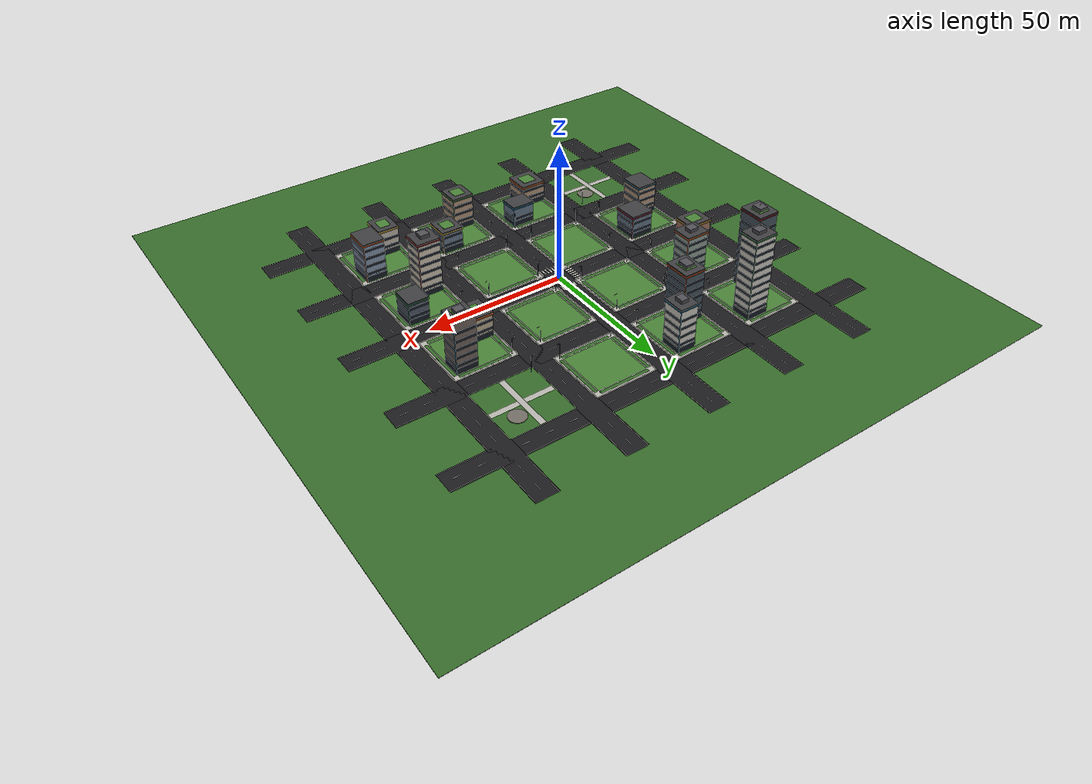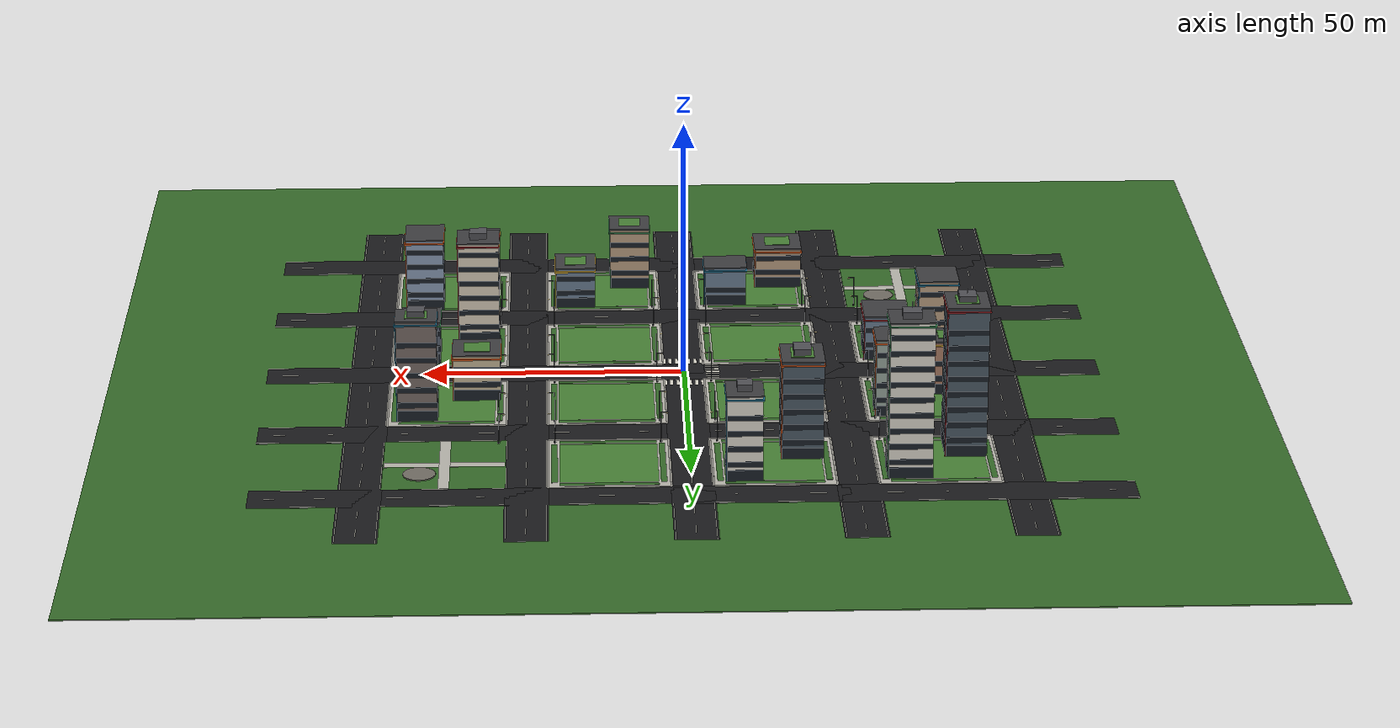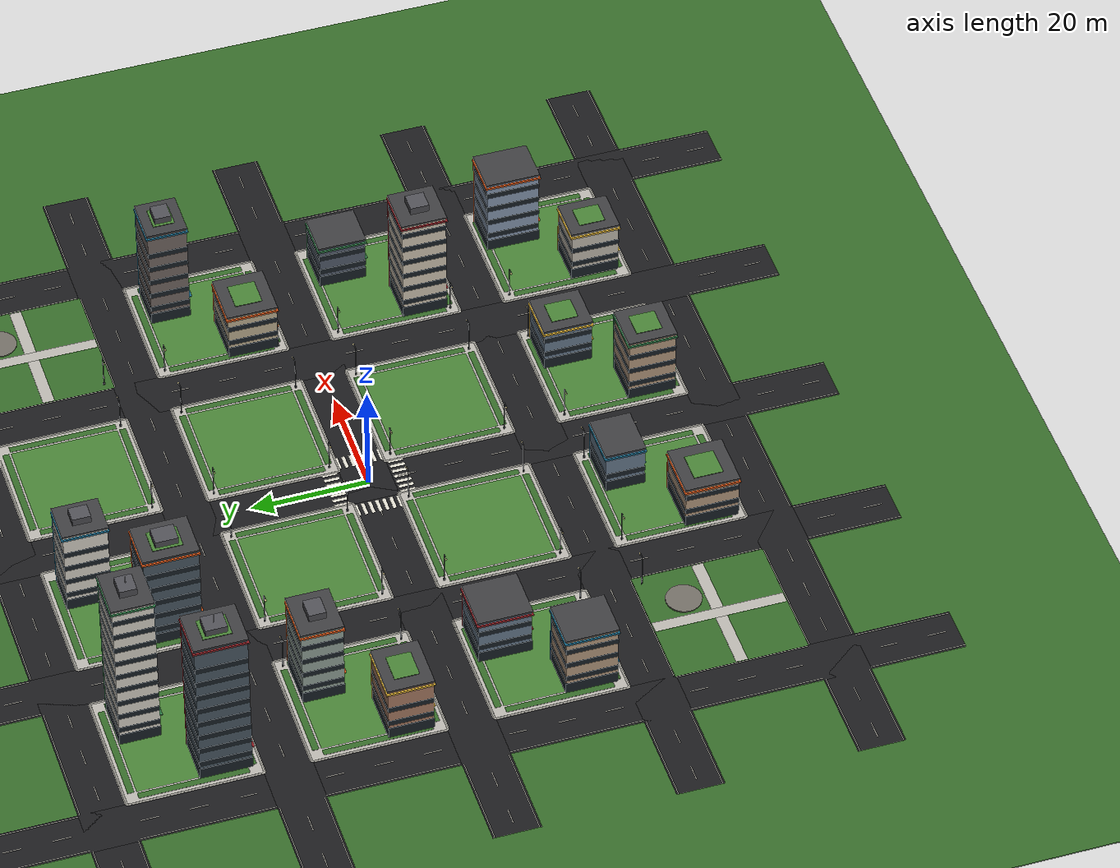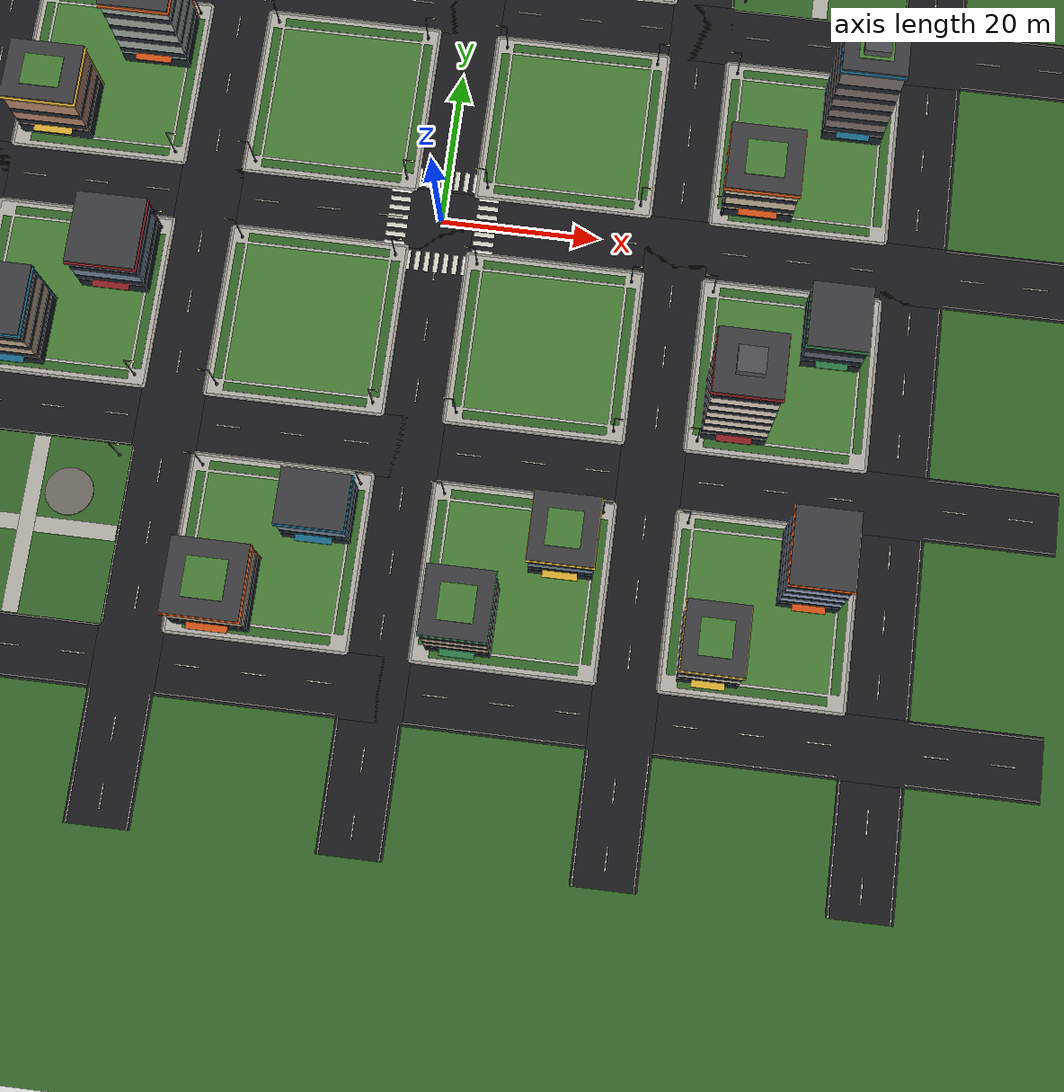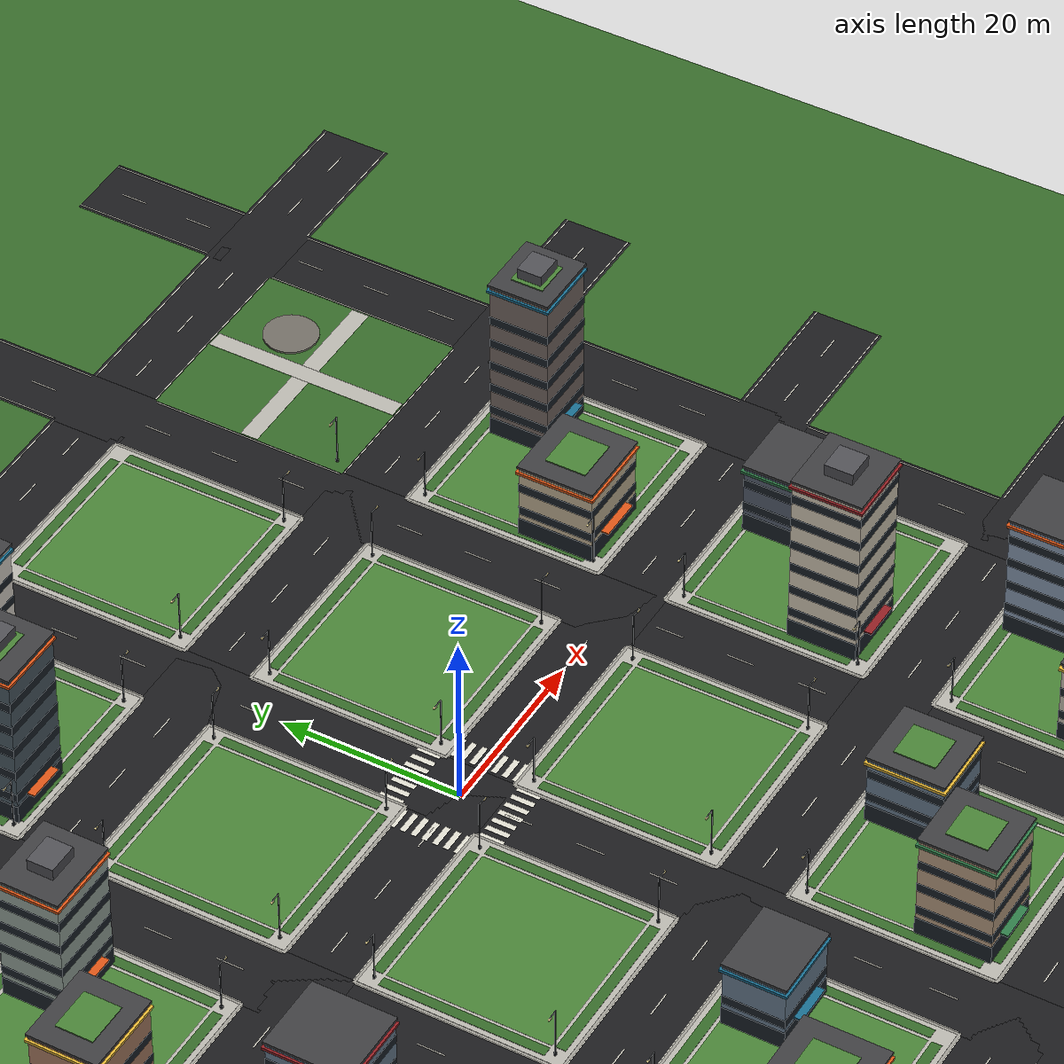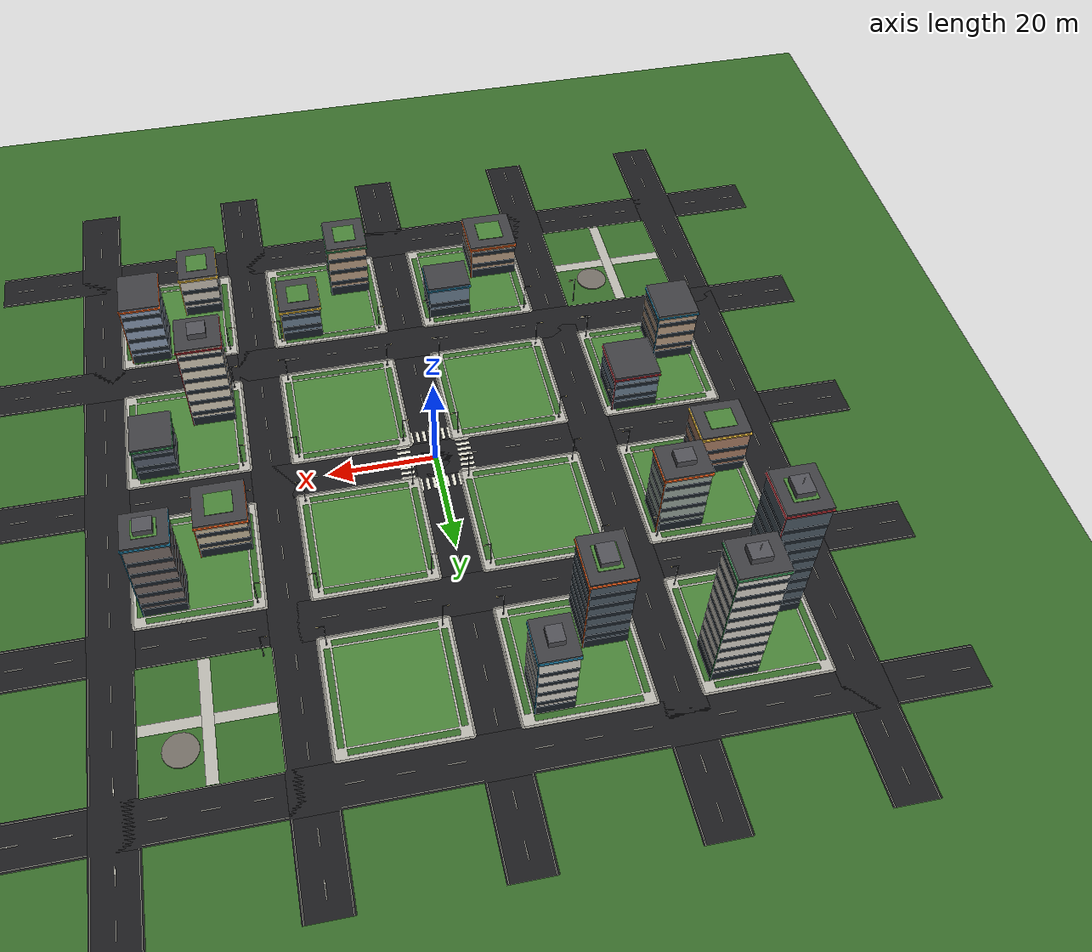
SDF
<sdf version="1.9">
 <world name="city">
  <physics name="4ms" type="ignored">
   <max_step_size>0.004</max_step_size>
   <real_time_factor>1.0</real_time_factor>
  </physics>
  <plugin filename="gz-sim-physics-system" name="gz::sim::systems::Physics"/>
  <plugin filename="gz-sim-user-commands-system" name="gz::sim::systems::UserCommands"/>
  <plugin filename="gz-sim-scene-broadcaster-system" name="gz::sim::systems::SceneBroadcaster"/>
  <plugin filename="gz-sim-sensors-system" name="gz::sim::systems::Sensors">
   <render_engine>ogre2</render_engine>
  </plugin>
  <plugin filename="gz-sim-imu-system" name="gz::sim::systems::Imu"/>
  <scene>
   <ambient>0.42 0.31 0.28 1</ambient>
   <background>0.97 0.68 0.46 1</background>
   <shadows>true</shadows>
   <grid>false</grid>
  </scene>
  <light type="directional" name="sun">
   <pose>0 0 40 0 0 0</pose>
   <diffuse>1.00 0.66 0.38 1</diffuse>
   <specular>0.95 0.60 0.30 1</specular>
   <direction>-0.86 0.38 -0.34</direction>
  </light>
  <light type="directional" name="sky_fill">
   <cast_shadows>false</cast_shadows>
   <pose>0 0 40 0 0 0</pose>
   <diffuse>0.30 0.36 0.55 1</diffuse>
   <specular>0.05 0.06 0.08 1</specular>
   <direction>0.55 -0.45 -0.70</direction>
  </light>
  <model name="ground">
   <static>true</static>
   <link name="link">
    <collision name="collision">
     <pose>0 0 -0.1 0 0 0</pose>
     <geometry><box><size>220 220 0.2</size></box></geometry>
     <surface><friction><ode><mu>1.0</mu><mu2>1.0</mu2></ode></friction></surface>
    </collision>
    <visual name="visual">
     <pose>0 0 -0.1 0 0 0</pose>
     <geometry><box><size>220 220 0.2</size></box></geometry>
     <material>
      <ambient>0.17 0.33 0.13 1</ambient>
      <diffuse>0.21 0.41 0.16 1</diffuse>
      <specular>0.05 0.06 0.04 1</specular>
     </material>
    </visual>
   </link>
  </model>
  <model name="city_ground">
   <static>true</static>
   <link name="link">
    <visual name="asphalt_h_0">
     <pose>0 -60 0.012 0 0 0</pose>
     <geometry><box><size>160 8 0.02</size></box></geometry>
     <material>
      <ambient>0.105 0.105 0.115 1</ambient>
      <diffuse>0.105 0.105 0.115 1</diffuse>
      <specular>0.03 0.03 0.03 1</specular>
     </material>
    </visual>
    <visual name="asphalt_v_0">
     <pose>-60 0 0.012 0 0 0</pose>
     <geometry><box><size>8 160 0.02</size></box></geometry>
     <material>
      <ambient>0.105 0.105 0.115 1</ambient>
      <diffuse>0.105 0.105 0.115 1</diffuse>
      <specular>0.03 0.03 0.03 1</specular>
     </material>
    </visual>
    <visual name="edge_h_0_-1_0">
     <pose>-45 -63.65 0.028 0 0 0</pose>
     <geometry><box><size>22 0.12 0.01</size></box></geometry>
     <material>
      <ambient>0.86 0.85 0.8 1</ambient>
      <diffuse>0.86 0.85 0.8 1</diffuse>
      <specular>0.12 0.12 0.12 1</specular>
     </material>
    </visual>
    <visual name="edge_v_0_-1_0">
     <pose>-63.65 -45 0.028 0 0 0</pose>
     <geometry><box><size>0.12 22 0.01</size></box></geometry>
     <material>
      <ambient>0.86 0.85 0.8 1</ambient>
      <diffuse>0.86 0.85 0.8 1</diffuse>
      <specular>0.12 0.12 0.12 1</specular>
     </material>
    </visual>
    <visual name="edge_h_0_-1_1">
     <pose>-15 -63.65 0.028 0 0 0</pose>
     <geometry><box><size>22 0.12 0.01</size></box></geometry>
     <material>
      <ambient>0.86 0.85 0.8 1</ambient>
      <diffuse>0.86 0.85 0.8 1</diffuse>
      <specular>0.12 0.12 0.12 1</specular>
     </material>
    </visual>
    <visual name="edge_v_0_-1_1">
     <pose>-63.65 -15 0.028 0 0 0</pose>
     <geometry><box><size>0.12 22 0.01</size></box></geometry>
     <material>
      <ambient>0.86 0.85 0.8 1</ambient>
      <diffuse>0.86 0.85 0.8 1</diffuse>
      <specular>0.12 0.12 0.12 1</specular>
     </material>
    </visual>
    <visual name="edge_h_0_-1_2">
     <pose>15 -63.65 0.028 0 0 0</pose>
     <geometry><box><size>22 0.12 0.01</size></box></geometry>
     <material>
      <ambient>0.86 0.85 0.8 1</ambient>
      <diffuse>0.86 0.85 0.8 1</diffuse>
      <specular>0.12 0.12 0.12 1</specular>
     </material>
    </visual>
    <visual name="edge_v_0_-1_2">
     <pose>-63.65 15 0.028 0 0 0</pose>
     <geometry><box><size>0.12 22 0.01</size></box></geometry>
     <material>
      <ambient>0.86 0.85 0.8 1</ambient>
      <diffuse>0.86 0.85 0.8 1</diffuse>
      <specular>0.12 0.12 0.12 1</specular>
     </material>
    </visual>
    <visual name="edge_h_0_-1_3">
     <pose>45 -63.65 0.028 0 0 0</pose>
     <geometry><box><size>22 0.12 0.01</size></box></geometry>
     <material>
      <ambient>0.86 0.85 0.8 1</ambient>
      <diffuse>0.86 0.85 0.8 1</diffuse>
      <specular>0.12 0.12 0.12 1</specular>
     </material>
    </visual>
    <visual name="edge_v_0_-1_3">
     <pose>-63.65 45 0.028 0 0 0</pose>
     <geometry><box><size>0.12 22 0.01</size></box></geometry>
     <material>
      <ambient>0.86 0.85 0.8 1</ambient>
      <diffuse>0.86 0.85 0.8 1</diffuse>
      <specular>0.12 0.12 0.12 1</specular>
     </material>
    </visual>
    <visual name="edge_h_0_-1_4">
     <pose>-72 -63.65 0.028 0 0 0</pose>
     <geometry><box><size>16 0.12 0.01</size></box></geometry>
     <material>
      <ambient>0.86 0.85 0.8 1</ambient>
      <diffuse>0.86 0.85 0.8 1</diffuse>
      <specular>0.12 0.12 0.12 1</specular>
     </material>
    </visual>
    <visual name="edge_v_0_-1_4">
     <pose>-63.65 -72 0.028 0 0 0</pose>
     <geometry><box><size>0.12 16 0.01</size></box></geometry>
     <material>
      <ambient>0.86 0.85 0.8 1</ambient>
      <diffuse>0.86 0.85 0.8 1</diffuse>
      <specular>0.12 0.12 0.12 1</specular>
     </material>
    </visual>
    <visual name="edge_h_0_-1_5">
     <pose>72 -63.65 0.028 0 0 0</pose>
     <geometry><box><size>16 0.12 0.01</size></box></geometry>
     <material>
      <ambient>0.86 0.85 0.8 1</ambient>
      <diffuse>0.86 0.85 0.8 1</diffuse>
      <specular>0.12 0.12 0.12 1</specular>
     </material>
    </visual>
    <visual name="edge_v_0_-1_5">
     <pose>-63.65 72 0.028 0 0 0</pose>
     <geometry><box><size>0.12 16 0.01</size></box></geometry>
     <material>
      <ambient>0.86 0.85 0.8 1</ambient>
      <diffuse>0.86 0.85 0.8 1</diffuse>
      <specular>0.12 0.12 0.12 1</specular>
     </material>
    </visual>
    <visual name="edge_h_0_1_0">
     <pose>-45 -56.35 0.028 0 0 0</pose>
     <geometry><box><size>22 0.12 0.01</size></box></geometry>
     <material>
      <ambient>0.86 0.85 0.8 1</ambient>
      <diffuse>0.86 0.85 0.8 1</diffuse>
      <specular>0.12 0.12 0.12 1</specular>
     </material>
    </visual>
    <visual name="edge_v_0_1_0">
     <pose>-56.35 -45 0.028 0 0 0</pose>
     <geometry><box><size>0.12 22 0.01</size></box></geometry>
     <material>
      <ambient>0.86 0.85 0.8 1</ambient>
      <diffuse>0.86 0.85 0.8 1</diffuse>
      <specular>0.12 0.12 0.12 1</specular>
     </material>
    </visual>
    <visual name="edge_h_0_1_1">
     <pose>-15 -56.35 0.028 0 0 0</pose>
     <geometry><box><size>22 0.12 0.01</size></box></geometry>
     <material>
      <ambient>0.86 0.85 0.8 1</ambient>
      <diffuse>0.86 0.85 0.8 1</diffuse>
      <specular>0.12 0.12 0.12 1</specular>
     </material>
    </visual>
    <visual name="edge_v_0_1_1">
     <pose>-56.35 -15 0.028 0 0 0</pose>
     <geometry><box><size>0.12 22 0.01</size></box></geometry>
     <material>
      <ambient>0.86 0.85 0.8 1</ambient>
      <diffuse>0.86 0.85 0.8 1</diffuse>
      <specular>0.12 0.12 0.12 1</specular>
     </material>
    </visual>
    <visual name="edge_h_0_1_2">
     <pose>15 -56.35 0.028 0 0 0</pose>
     <geometry><box><size>22 0.12 0.01</size></box></geometry>
     <material>
      <ambient>0.86 0.85 0.8 1</ambient>
      <diffuse>0.86 0.85 0.8 1</diffuse>
      <specular>0.12 0.12 0.12 1</specular>
     </material>
    </visual>
    <visual name="edge_v_0_1_2">
     <pose>-56.35 15 0.028 0 0 0</pose>
     <geometry><box><size>0.12 22 0.01</size></box></geometry>
     <material>
      <ambient>0.86 0.85 0.8 1</ambient>
      <diffuse>0.86 0.85 0.8 1</diffuse>
      <specular>0.12 0.12 0.12 1</specular>
     </material>
    </visual>
    <visual name="edge_h_0_1_3">
     <pose>45 -56.35 0.028 0 0 0</pose>
     <geometry><box><size>22 0.12 0.01</size></box></geometry>
     <material>
      <ambient>0.86 0.85 0.8 1</ambient>
      <diffuse>0.86 0.85 0.8 1</diffuse>
      <specular>0.12 0.12 0.12 1</specular>
     </material>
    </visual>
    <visual name="edge_v_0_1_3">
     <pose>-56.35 45 0.028 0 0 0</pose>
     <geometry><box><size>0.12 22 0.01</size></box></geometry>
     <material>
      <ambient>0.86 0.85 0.8 1</ambient>
      <diffuse>0.86 0.85 0.8 1</diffuse>
      <specular>0.12 0.12 0.12 1</specular>
     </material>
    </visual>
    <visual name="edge_h_0_1_4">
     <pose>-72 -56.35 0.028 0 0 0</pose>
     <geometry><box><size>16 0.12 0.01</size></box></geometry>
     <material>
      <ambient>0.86 0.85 0.8 1</ambient>
      <diffuse>0.86 0.85 0.8 1</diffuse>
      <specular>0.12 0.12 0.12 1</specular>
     </material>
    </visual>
    <visual name="edge_v_0_1_4">
     <pose>-56.35 -72 0.028 0 0 0</pose>
     <geometry><box><size>0.12 16 0.01</size></box></geometry>
     <material>
      <ambient>0.86 0.85 0.8 1</ambient>
      <diffuse>0.86 0.85 0.8 1</diffuse>
      <specular>0.12 0.12 0.12 1</specular>
     </material>
    </visual>
    <visual name="edge_h_0_1_5">
     <pose>72 -56.35 0.028 0 0 0</pose>
     <geometry><box><size>16 0.12 0.01</size></box></geometry>
     <material>
      <ambient>0.86 0.85 0.8 1</ambient>
      <diffuse>0.86 0.85 0.8 1</diffuse>
      <specular>0.12 0.12 0.12 1</specular>
     </material>
    </visual>
    <visual name="edge_v_0_1_5">
     <pose>-56.35 72 0.028 0 0 0</pose>
     <geometry><box><size>0.12 16 0.01</size></box></geometry>
     <material>
      <ambient>0.86 0.85 0.8 1</ambient>
      <diffuse>0.86 0.85 0.8 1</diffuse>
      <specular>0.12 0.12 0.12 1</specular>
     </material>
    </visual>
    <visual name="dash_h_0_0_0">
     <pose>-52.5 -60 0.030 0 0 0</pose>
     <geometry><box><size>3.0 0.14 0.01</size></box></geometry>
     <material>
      <ambient>0.86 0.85 0.8 1</ambient>
      <diffuse>0.86 0.85 0.8 1</diffuse>
      <specular>0.12 0.12 0.12 1</specular>
     </material>
    </visual>
    <visual name="dash_v_0_0_0">
     <pose>-60 -52.5 0.030 0 0 0</pose>
     <geometry><box><size>0.14 3.0 0.01</size></box></geometry>
     <material>
      <ambient>0.86 0.85 0.8 1</ambient>
      <diffuse>0.86 0.85 0.8 1</diffuse>
      <specular>0.12 0.12 0.12 1</specular>
     </material>
    </visual>
    <visual name="dash_h_0_0_1">
     <pose>-44.5 -60 0.030 0 0 0</pose>
     <geometry><box><size>3.0 0.14 0.01</size></box></geometry>
     <material>
      <ambient>0.86 0.85 0.8 1</ambient>
      <diffuse>0.86 0.85 0.8 1</diffuse>
      <specular>0.12 0.12 0.12 1</specular>
     </material>
    </visual>
    <visual name="dash_v_0_0_1">
     <pose>-60 -44.5 0.030 0 0 0</pose>
     <geometry><box><size>0.14 3.0 0.01</size></box></geometry>
     <material>
      <ambient>0.86 0.85 0.8 1</ambient>
      <diffuse>0.86 0.85 0.8 1</diffuse>
      <specular>0.12 0.12 0.12 1</specular>
     </material>
    </visual>
    <visual name="dash_h_0_0_2">
     <pose>-36.5 -60 0.030 0 0 0</pose>
     <geometry><box><size>3.0 0.14 0.01</size></box></geometry>
     <material>
      <ambient>0.86 0.85 0.8 1</ambient>
      <diffuse>0.86 0.85 0.8 1</diffuse>
      <specular>0.12 0.12 0.12 1</specular>
     </material>
    </visual>
    <visual name="dash_v_0_0_2">
     <pose>-60 -36.5 0.030 0 0 0</pose>
     <geometry><box><size>0.14 3.0 0.01</size></box></geometry>
     <material>
      <ambient>0.86 0.85 0.8 1</ambient>
      <diffuse>0.86 0.85 0.8 1</diffuse>
      <specular>0.12 0.12 0.12 1</specular>
     </material>
    </visual>
    <visual name="dash_h_0_1_0">
     <pose>-22.5 -60 0.030 0 0 0</pose>
     <geometry><box><size>3.0 0.14 0.01</size></box></geometry>
     <material>
      <ambient>0.86 0.85 0.8 1</ambient>
      <diffuse>0.86 0.85 0.8 1</diffuse>
      <specular>0.12 0.12 0.12 1</specular>
     </material>
    </visual>
    <visual name="dash_v_0_1_0">
     <pose>-60 -22.5 0.030 0 0 0</pose>
     <geometry><box><size>0.14 3.0 0.01</size></box></geometry>
     <material>
      <ambient>0.86 0.85 0.8 1</ambient>
      <diffuse>0.86 0.85 0.8 1</diffuse>
      <specular>0.12 0.12 0.12 1</specular>
     </material>
    </visual>
    <visual name="dash_h_0_1_1">
     <pose>-14.5 -60 0.030 0 0 0</pose>
     <geometry><box><size>3.0 0.14 0.01</size></box></geometry>
     <material>
      <ambient>0.86 0.85 0.8 1</ambient>
      <diffuse>0.86 0.85 0.8 1</diffuse>
      <specular>0.12 0.12 0.12 1</specular>
     </material>
    </visual>
    <visual name="dash_v_0_1_1">
     <pose>-60 -14.5 0.030 0 0 0</pose>
     <geometry><box><size>0.14 3.0 0.01</size></box></geometry>
     <material>
      <ambient>0.86 0.85 0.8 1</ambient>
      <diffuse>0.86 0.85 0.8 1</diffuse>
      <specular>0.12 0.12 0.12 1</specular>
     </material>
    </visual>
    <visual name="dash_h_0_1_2">
     <pose>-6.5 -60 0.030 0 0 0</pose>
     <geometry><box><size>3.0 0.14 0.01</size></box></geometry>
     <material>
      <ambient>0.86 0.85 0.8 1</ambient>
      <diffuse>0.86 0.85 0.8 1</diffuse>
      <specular>0.12 0.12 0.12 1</specular>
     </material>
    </visual>
    <visual name="dash_v_0_1_2">
     <pose>-60 -6.5 0.030 0 0 0</pose>
     <geometry><box><size>0.14 3.0 0.01</size></box></geometry>
     <material>
      <ambient>0.86 0.85 0.8 1</ambient>
      <diffuse>0.86 0.85 0.8 1</diffuse>
      <specular>0.12 0.12 0.12 1</specular>
     </material>
    </visual>
    <visual name="dash_h_0_2_0">
     <pose>7.5 -60 0.030 0 0 0</pose>
     <geometry><box><size>3.0 0.14 0.01</size></box></geometry>
     <material>
      <ambient>0.86 0.85 0.8 1</ambient>
      <diffuse>0.86 0.85 0.8 1</diffuse>
      <specular>0.12 0.12 0.12 1</specular>
     </material>
    </visual>
    <visual name="dash_v_0_2_0">
     <pose>-60 7.5 0.030 0 0 0</pose>
     <geometry><box><size>0.14 3.0 0.01</size></box></geometry>
     <material>
      <ambient>0.86 0.85 0.8 1</ambient>
      <diffuse>0.86 0.85 0.8 1</diffuse>
      <specular>0.12 0.12 0.12 1</specular>
     </material>
    </visual>
    <visual name="dash_h_0_2_1">
     <pose>15.5 -60 0.030 0 0 0</pose>
     <geometry><box><size>3.0 0.14 0.01</size></box></geometry>
     <material>
      <ambient>0.86 0.85 0.8 1</ambient>
      <diffuse>0.86 0.85 0.8 1</diffuse>
      <specular>0.12 0.12 0.12 1</specular>
     </material>
    </visual>
    <visual name="dash_v_0_2_1">
     <pose>-60 15.5 0.030 0 0 0</pose>
     <geometry><box><size>0.14 3.0 0.01</size></box></geometry>
     <material>
      <ambient>0.86 0.85 0.8 1</ambient>
      <diffuse>0.86 0.85 0.8 1</diffuse>
      <specular>0.12 0.12 0.12 1</specular>
     </material>
    </visual>
    <visual name="dash_h_0_2_2">
     <pose>23.5 -60 0.030 0 0 0</pose>
     <geometry><box><size>3.0 0.14 0.01</size></box></geometry>
     <material>
      <ambient>0.86 0.85 0.8 1</ambient>
      <diffuse>0.86 0.85 0.8 1</diffuse>
      <specular>0.12 0.12 0.12 1</specular>
     </material>
    </visual>
    <visual name="dash_v_0_2_2">
     <pose>-60 23.5 0.030 0 0 0</pose>
     <geometry><box><size>0.14 3.0 0.01</size></box></geometry>
     <material>
      <ambient>0.86 0.85 0.8 1</ambient>
      <diffuse>0.86 0.85 0.8 1</diffuse>
      <specular>0.12 0.12 0.12 1</specular>
     </material>
    </visual>
    <visual name="dash_h_0_3_0">
     <pose>37.5 -60 0.030 0 0 0</pose>
     <geometry><box><size>3.0 0.14 0.01</size></box></geometry>
     <material>
      <ambient>0.86 0.85 0.8 1</ambient>
      <diffuse>0.86 0.85 0.8 1</diffuse>
      <specular>0.12 0.12 0.12 1</specular>
     </material>
    </visual>
    <visual name="dash_v_0_3_0">
     <pose>-60 37.5 0.030 0 0 0</pose>
     <geometry><box><size>0.14 3.0 0.01</size></box></geometry>
     <material>
      <ambient>0.86 0.85 0.8 1</ambient>
      <diffuse>0.86 0.85 0.8 1</diffuse>
      <specular>0.12 0.12 0.12 1</specular>
     </material>
    </visual>
    <visual name="dash_h_0_3_1">
     <pose>45.5 -60 0.030 0 0 0</pose>
     <geometry><box><size>3.0 0.14 0.01</size></box></geometry>
     <material>
      <ambient>0.86 0.85 0.8 1</ambient>
      <diffuse>0.86 0.85 0.8 1</diffuse>
      <specular>0.12 0.12 0.12 1</specular>
     </material>
    </visual>
    <visual name="dash_v_0_3_1">
     <pose>-60 45.5 0.030 0 0 0</pose>
     <geometry><box><size>0.14 3.0 0.01</size></box></geometry>
     <material>
      <ambient>0.86 0.85 0.8 1</ambient>
      <diffuse>0.86 0.85 0.8 1</diffuse>
      <specular>0.12 0.12 0.12 1</specular>
     </material>
    </visual>
    <visual name="dash_h_0_3_2">
     <pose>53.5 -60 0.030 0 0 0</pose>
     <geometry><box><size>3.0 0.14 0.01</size></box></geometry>
     <material>
      <ambient>0.86 0.85 0.8 1</ambient>
      <diffuse>0.86 0.85 0.8 1</diffuse>
      <specular>0.12 0.12 0.12 1</specular>
     </material>
    </visual>
    <visual name="dash_v_0_3_2">
     <pose>-60 53.5 0.030 0 0 0</pose>
     <geometry><box><size>0.14 3.0 0.01</size></box></geometry>
     <material>
      <ambient>0.86 0.85 0.8 1</ambient>
      <diffuse>0.86 0.85 0.8 1</diffuse>
      <specular>0.12 0.12 0.12 1</specular>
     </material>
    </visual>
    <visual name="dash_h_0_4_0">
     <pose>-76.5 -60 0.030 0 0 0</pose>
     <geometry><box><size>3.0 0.14 0.01</size></box></geometry>
     <material>
      <ambient>0.86 0.85 0.8 1</ambient>
      <diffuse>0.86 0.85 0.8 1</diffuse>
      <specular>0.12 0.12 0.12 1</specular>
     </material>
    </visual>
    <visual name="dash_v_0_4_0">
     <pose>-60 -76.5 0.030 0 0 0</pose>
     <geometry><box><size>0.14 3.0 0.01</size></box></geometry>
     <material>
      <ambient>0.86 0.85 0.8 1</ambient>
      <diffuse>0.86 0.85 0.8 1</diffuse>
      <specular>0.12 0.12 0.12 1</specular>
     </material>
    </visual>
    <visual name="dash_h_0_4_1">
     <pose>-68.5 -60 0.030 0 0 0</pose>
     <geometry><box><size>3.0 0.14 0.01</size></box></geometry>
     <material>
      <ambient>0.86 0.85 0.8 1</ambient>
      <diffuse>0.86 0.85 0.8 1</diffuse>
      <specular>0.12 0.12 0.12 1</specular>
     </material>
    </visual>
    <visual name="dash_v_0_4_1">
     <pose>-60 -68.5 0.030 0 0 0</pose>
     <geometry><box><size>0.14 3.0 0.01</size></box></geometry>
     <material>
      <ambient>0.86 0.85 0.8 1</ambient>
      <diffuse>0.86 0.85 0.8 1</diffuse>
      <specular>0.12 0.12 0.12 1</specular>
     </material>
    </visual>
    <visual name="dash_h_0_5_0">
     <pose>67.5 -60 0.030 0 0 0</pose>
     <geometry><box><size>3.0 0.14 0.01</size></box></geometry>
     <material>
      <ambient>0.86 0.85 0.8 1</ambient>
      <diffuse>0.86 0.85 0.8 1</diffuse>
      <specular>0.12 0.12 0.12 1</specular>
     </material>
    </visual>
    <visual name="dash_v_0_5_0">
     <pose>-60 67.5 0.030 0 0 0</pose>
     <geometry><box><size>0.14 3.0 0.01</size></box></geometry>
     <material>
      <ambient>0.86 0.85 0.8 1</ambient>
      <diffuse>0.86 0.85 0.8 1</diffuse>
      <specular>0.12 0.12 0.12 1</specular>
     </material>
    </visual>
    <visual name="dash_h_0_5_1">
     <pose>75.5 -60 0.030 0 0 0</pose>
     <geometry><box><size>3.0 0.14 0.01</size></box></geometry>
     <material>
      <ambient>0.86 0.85 0.8 1</ambient>
      <diffuse>0.86 0.85 0.8 1</diffuse>
      <specular>0.12 0.12 0.12 1</specular>
     </material>
    </visual>
    <visual name="dash_v_0_5_1">
     <pose>-60 75.5 0.030 0 0 0</pose>
     <geometry><box><size>0.14 3.0 0.01</size></box></geometry>
     <material>
      <ambient>0.86 0.85 0.8 1</ambient>
      <diffuse>0.86 0.85 0.8 1</diffuse>
      <specular>0.12 0.12 0.12 1</specular>
     </material>
    </visual>
    <visual name="asphalt_h_1">
     <pose>0 -30 0.012 0 0 0</pose>
     <geometry><box><size>160 8 0.02</size></box></geometry>
     <material>
      <ambient>0.105 0.105 0.115 1</ambient>
      <diffuse>0.105 0.105 0.115 1</diffuse>
      <specular>0.03 0.03 0.03 1</specular>
     </material>
    </visual>
    <visual name="asphalt_v_1">
     <pose>-30 0 0.012 0 0 0</pose>
     <geometry><box><size>8 160 0.02</size></box></geometry>
     <material>
      <ambient>0.105 0.105 0.115 1</ambient>
      <diffuse>0.105 0.105 0.115 1</diffuse>
      <specular>0.03 0.03 0.03 1</specular>
     </material>
    </visual>
    <visual name="edge_h_1_-1_0">
     <pose>-45 -33.65 0.028 0 0 0</pose>
     <geometry><box><size>22 0.12 0.01</size></box></geometry>
     <material>
      <ambient>0.86 0.85 0.8 1</ambient>
      <diffuse>0.86 0.85 0.8 1</diffuse>
      <specular>0.12 0.12 0.12 1</specular>
     </material>
    </visual>
    <visual name="edge_v_1_-1_0">
     <pose>-33.65 -45 0.028 0 0 0</pose>
     <geometry><box><size>0.12 22 0.01</size></box></geometry>
     <material>
      <ambient>0.86 0.85 0.8 1</ambient>
      <diffuse>0.86 0.85 0.8 1</diffuse>
      <specular>0.12 0.12 0.12 1</specular>
     </material>
    </visual>
    <visual name="edge_h_1_-1_1">
     <pose>-15 -33.65 0.028 0 0 0</pose>
     <geometry><box><size>22 0.12 0.01</size></box></geometry>
     <material>
      <ambient>0.86 0.85 0.8 1</ambient>
      <diffuse>0.86 0.85 0.8 1</diffuse>
      <specular>0.12 0.12 0.12 1</specular>
     </material>
    </visual>
    <visual name="edge_v_1_-1_1">
     <pose>-33.65 -15 0.028 0 0 0</pose>
     <geometry><box><size>0.12 22 0.01</size></box></geometry>
     <material>
      <ambient>0.86 0.85 0.8 1</ambient>
      <diffuse>0.86 0.85 0.8 1</diffuse>
      <specular>0.12 0.12 0.12 1</specular>
     </material>
    </visual>
    <visual name="edge_h_1_-1_2">
     <pose>15 -33.65 0.028 0 0 0</pose>
     <geometry><box><size>22 0.12 0.01</size></box></geometry>
     <material>
      <ambient>0.86 0.85 0.8 1</ambient>
      <diffuse>0.86 0.85 0.8 1</diffuse>
      <specular>0.12 0.12 0.12 1</specular>
     </material>
    </visual>
    <visual name="edge_v_1_-1_2">
     <pose>-33.65 15 0.028 0 0 0</pose>
     <geometry><box><size>0.12 22 0.01</size></box></geometry>
     <material>
      <ambient>0.86 0.85 0.8 1</ambient>
      <diffuse>0.86 0.85 0.8 1</diffuse>
      <specular>0.12 0.12 0.12 1</specular>
     </material>
    </visual>
    <visual name="edge_h_1_-1_3">
     <pose>45 -33.65 0.028 0 0 0</pose>
     <geometry><box><size>22 0.12 0.01</size></box></geometry>
     <material>
      <ambient>0.86 0.85 0.8 1</ambient>
      <diffuse>0.86 0.85 0.8 1</diffuse>
      <specular>0.12 0.12 0.12 1</specular>
     </material>
    </visual>
    <visual name="edge_v_1_-1_3">
     <pose>-33.65 45 0.028 0 0 0</pose>
     <geometry><box><size>0.12 22 0.01</size></box></geometry>
     <material>
      <ambient>0.86 0.85 0.8 1</ambient>
      <diffuse>0.86 0.85 0.8 1</diffuse>
      <specular>0.12 0.12 0.12 1</specular>
     </material>
    </visual>
    <visual name="edge_h_1_-1_4">
     <pose>-72 -33.65 0.028 0 0 0</pose>
     <geometry><box><size>16 0.12 0.01</size></box></geometry>
     <material>
      <ambient>0.86 0.85 0.8 1</ambient>
      <diffuse>0.86 0.85 0.8 1</diffuse>
      <specular>0.12 0.12 0.12 1</specular>
     </material>
    </visual>
    <visual name="edge_v_1_-1_4">
     <pose>-33.65 -72 0.028 0 0 0</pose>
     <geometry><box><size>0.12 16 0.01</size></box></geometry>
     <material>
      <ambient>0.86 0.85 0.8 1</ambient>
      <diffuse>0.86 0.85 0.8 1</diffuse>
      <specular>0.12 0.12 0.12 1</specular>
     </material>
    </visual>
    <visual name="edge_h_1_-1_5">
     <pose>72 -33.65 0.028 0 0 0</pose>
     <geometry><box><size>16 0.12 0.01</size></box></geometry>
     <material>
      <ambient>0.86 0.85 0.8 1</ambient>
      <diffuse>0.86 0.85 0.8 1</diffuse>
      <specular>0.12 0.12 0.12 1</specular>
     </material>
    </visual>
    <visual name="edge_v_1_-1_5">
     <pose>-33.65 72 0.028 0 0 0</pose>
     <geometry><box><size>0.12 16 0.01</size></box></geometry>
     <material>
      <ambient>0.86 0.85 0.8 1</ambient>
      <diffuse>0.86 0.85 0.8 1</diffuse>
      <specular>0.12 0.12 0.12 1</specular>
     </material>
    </visual>
    <visual name="edge_h_1_1_0">
     <pose>-45 -26.35 0.028 0 0 0</pose>
     <geometry><box><size>22 0.12 0.01</size></box></geometry>
     <material>
      <ambient>0.86 0.85 0.8 1</ambient>
      <diffuse>0.86 0.85 0.8 1</diffuse>
      <specular>0.12 0.12 0.12 1</specular>
     </material>
    </visual>
    <visual name="edge_v_1_1_0">
     <pose>-26.35 -45 0.028 0 0 0</pose>
     <geometry><box><size>0.12 22 0.01</size></box></geometry>
     <material>
      <ambient>0.86 0.85 0.8 1</ambient>
      <diffuse>0.86 0.85 0.8 1</diffuse>
      <specular>0.12 0.12 0.12 1</specular>
     </material>
    </visual>
    <visual name="edge_h_1_1_1">
     <pose>-15 -26.35 0.028 0 0 0</pose>
     <geometry><box><size>22 0.12 0.01</size></box></geometry>
     <material>
      <ambient>0.86 0.85 0.8 1</ambient>
      <diffuse>0.86 0.85 0.8 1</diffuse>
      <specular>0.12 0.12 0.12 1</specular>
     </material>
    </visual>
    <visual name="edge_v_1_1_1">
     <pose>-26.35 -15 0.028 0 0 0</pose>
     <geometry><box><size>0.12 22 0.01</size></box></geometry>
     <material>
      <ambient>0.86 0.85 0.8 1</ambient>
      <diffuse>0.86 0.85 0.8 1</diffuse>
      <specular>0.12 0.12 0.12 1</specular>
     </material>
    </visual>
    <visual name="edge_h_1_1_2">
     <pose>15 -26.35 0.028 0 0 0</pose>
     <geometry><box><size>22 0.12 0.01</size></box></geometry>
     <material>
      <ambient>0.86 0.85 0.8 1</ambient>
      <diffuse>0.86 0.85 0.8 1</diffuse>
      <specular>0.12 0.12 0.12 1</specular>
     </material>
    </visual>
    <visual name="edge_v_1_1_2">
     <pose>-26.35 15 0.028 0 0 0</pose>
     <geometry><box><size>0.12 22 0.01</size></box></geometry>
     <material>
      <ambient>0.86 0.85 0.8 1</ambient>
      <diffuse>0.86 0.85 0.8 1</diffuse>
      <specular>0.12 0.12 0.12 1</specular>
     </material>
    </visual>
    <visual name="edge_h_1_1_3">
     <pose>45 -26.35 0.028 0 0 0</pose>
     <geometry><box><size>22 0.12 0.01</size></box></geometry>
     <material>
      <ambient>0.86 0.85 0.8 1</ambient>
      <diffuse>0.86 0.85 0.8 1</diffuse>
      <specular>0.12 0.12 0.12 1</specular>
     </material>
    </visual>
    <visual name="edge_v_1_1_3">
     <pose>-26.35 45 0.028 0 0 0</pose>
     <geometry><box><size>0.12 22 0.01</size></box></geometry>
     <material>
      <ambient>0.86 0.85 0.8 1</ambient>
      <diffuse>0.86 0.85 0.8 1</diffuse>
      <specular>0.12 0.12 0.12 1</specular>
     </material>
    </visual>
    <visual name="edge_h_1_1_4">
     <pose>-72 -26.35 0.028 0 0 0</pose>
     <geometry><box><size>16 0.12 0.01</size></box></geometry>
     <material>
      <ambient>0.86 0.85 0.8 1</ambient>
      <diffuse>0.86 0.85 0.8 1</diffuse>
      <specular>0.12 0.12 0.12 1</specular>
     </material>
    </visual>
    <visual name="edge_v_1_1_4">
     <pose>-26.35 -72 0.028 0 0 0</pose>
     <geometry><box><size>0.12 16 0.01</size></box></geometry>
     <material>
      <ambient>0.86 0.85 0.8 1</ambient>
      <diffuse>0.86 0.85 0.8 1</diffuse>
      <specular>0.12 0.12 0.12 1</specular>
     </material>
    </visual>
    <visual name="edge_h_1_1_5">
     <pose>72 -26.35 0.028 0 0 0</pose>
     <geometry><box><size>16 0.12 0.01</size></box></geometry>
     <material>
      <ambient>0.86 0.85 0.8 1</ambient>
      <diffuse>0.86 0.85 0.8 1</diffuse>
      <specular>0.12 0.12 0.12 1</specular>
     </material>
    </visual>
    <visual name="edge_v_1_1_5">
     <pose>-26.35 72 0.028 0 0 0</pose>
     <geometry><box><size>0.12 16 0.01</size></box></geometry>
     <material>
      <ambient>0.86 0.85 0.8 1</ambient>
      <diffuse>0.86 0.85 0.8 1</diffuse>
      <specular>0.12 0.12 0.12 1</specular>
     </material>
    </visual>
    <visual name="dash_h_1_0_0">
     <pose>-52.5 -30 0.030 0 0 0</pose>
     <geometry><box><size>3.0 0.14 0.01</size></box></geometry>
     <material>
      <ambient>0.86 0.85 0.8 1</ambient>
      <diffuse>0.86 0.85 0.8 1</diffuse>
      <specular>0.12 0.12 0.12 1</specular>
     </material>
    </visual>
    <visual name="dash_v_1_0_0">
     <pose>-30 -52.5 0.030 0 0 0</pose>
     <geometry><box><size>0.14 3.0 0.01</size></box></geometry>
     <material>
      <ambient>0.86 0.85 0.8 1</ambient>
      <diffuse>0.86 0.85 0.8 1</diffuse>
      <specular>0.12 0.12 0.12 1</specular>
     </material>
    </visual>
    <visual name="dash_h_1_0_1">
     <pose>-44.5 -30 0.030 0 0 0</pose>
     <geometry><box><size>3.0 0.14 0.01</size></box></geometry>
     <material>
      <ambient>0.86 0.85 0.8 1</ambient>
      <diffuse>0.86 0.85 0.8 1</diffuse>
      <specular>0.12 0.12 0.12 1</specular>
     </material>
    </visual>
    <visual name="dash_v_1_0_1">
     <pose>-30 -44.5 0.030 0 0 0</pose>
     <geometry><box><size>0.14 3.0 0.01</size></box></geometry>
     <material>
      <ambient>0.86 0.85 0.8 1</ambient>
      <diffuse>0.86 0.85 0.8 1</diffuse>
      <specular>0.12 0.12 0.12 1</specular>
     </material>
    </visual>
    <visual name="dash_h_1_0_2">
     <pose>-36.5 -30 0.030 0 0 0</pose>
     <geometry><box><size>3.0 0.14 0.01</size></box></geometry>
     <material>
      <ambient>0.86 0.85 0.8 1</ambient>
      <diffuse>0.86 0.85 0.8 1</diffuse>
      <specular>0.12 0.12 0.12 1</specular>
     </material>
    </visual>
    <visual name="dash_v_1_0_2">
     <pose>-30 -36.5 0.030 0 0 0</pose>
     <geometry><box><size>0.14 3.0 0.01</size></box></geometry>
     <material>
      <ambient>0.86 0.85 0.8 1</ambient>
      <diffuse>0.86 0.85 0.8 1</diffuse>
      <specular>0.12 0.12 0.12 1</specular>
     </material>
    </visual>
    <visual name="dash_h_1_1_0">
     <pose>-22.5 -30 0.030 0 0 0</pose>
     <geometry><box><size>3.0 0.14 0.01</size></box></geometry>
     <material>
      <ambient>0.86 0.85 0.8 1</ambient>
      <diffuse>0.86 0.85 0.8 1</diffuse>
      <specular>0.12 0.12 0.12 1</specular>
     </material>
    </visual>
    <visual name="dash_v_1_1_0">
     <pose>-30 -22.5 0.030 0 0 0</pose>
     <geometry><box><size>0.14 3.0 0.01</size></box></geometry>
     <material>
      <ambient>0.86 0.85 0.8 1</ambient>
      <diffuse>0.86 0.85 0.8 1</diffuse>
      <specular>0.12 0.12 0.12 1</specular>
     </material>
    </visual>
    <visual name="dash_h_1_1_1">
     <pose>-14.5 -30 0.030 0 0 0</pose>
     <geometry><box><size>3.0 0.14 0.01</size></box></geometry>
     <material>
      <ambient>0.86 0.85 0.8 1</ambient>
      <diffuse>0.86 0.85 0.8 1</diffuse>
      <specular>0.12 0.12 0.12 1</specular>
     </material>
    </visual>
    <visual name="dash_v_1_1_1">
     <pose>-30 -14.5 0.030 0 0 0</pose>
     <geometry><box><size>0.14 3.0 0.01</size></box></geometry>
     <material>
      <ambient>0.86 0.85 0.8 1</ambient>
      <diffuse>0.86 0.85 0.8 1</diffuse>
      <specular>0.12 0.12 0.12 1</specular>
     </material>
    </visual>
    <visual name="dash_h_1_1_2">
     <pose>-6.5 -30 0.030 0 0 0</pose>
     <geometry><box><size>3.0 0.14 0.01</size></box></geometry>
     <material>
      <ambient>0.86 0.85 0.8 1</ambient>
      <diffuse>0.86 0.85 0.8 1</diffuse>
      <specular>0.12 0.12 0.12 1</specular>
     </material>
    </visual>
    <visual name="dash_v_1_1_2">
     <pose>-30 -6.5 0.030 0 0 0</pose>
     <geometry><box><size>0.14 3.0 0.01</size></box></geometry>
     <material>
      <ambient>0.86 0.85 0.8 1</ambient>
      <diffuse>0.86 0.85 0.8 1</diffuse>
      <specular>0.12 0.12 0.12 1</specular>
     </material>
    </visual>
    <visual name="dash_h_1_2_0">
     <pose>7.5 -30 0.030 0 0 0</pose>
     <geometry><box><size>3.0 0.14 0.01</size></box></geometry>
     <material>
      <ambient>0.86 0.85 0.8 1</ambient>
      <diffuse>0.86 0.85 0.8 1</diffuse>
      <specular>0.12 0.12 0.12 1</specular>
     </material>
    </visual>
    <visual name="dash_v_1_2_0">
     <pose>-30 7.5 0.030 0 0 0</pose>
     <geometry><box><size>0.14 3.0 0.01</size></box></geometry>
     <material>
      <ambient>0.86 0.85 0.8 1</ambient>
      <diffuse>0.86 0.85 0.8 1</diffuse>
      <specular>0.12 0.12 0.12 1</specular>
     </material>
    </visual>
    <visual name="dash_h_1_2_1">
     <pose>15.5 -30 0.030 0 0 0</pose>
     <geometry><box><size>3.0 0.14 0.01</size></box></geometry>
     <material>
      <ambient>0.86 0.85 0.8 1</ambient>
      <diffuse>0.86 0.85 0.8 1</diffuse>
      <specular>0.12 0.12 0.12 1</specular>
     </material>
    </visual>
    <visual name="dash_v_1_2_1">
     <pose>-30 15.5 0.030 0 0 0</pose>
     <geometry><box><size>0.14 3.0 0.01</size></box></geometry>
     <material>
      <ambient>0.86 0.85 0.8 1</ambient>
      <diffuse>0.86 0.85 0.8 1</diffuse>
      <specular>0.12 0.12 0.12 1</specular>
     </material>
    </visual>
    <visual name="dash_h_1_2_2">
     <pose>23.5 -30 0.030 0 0 0</pose>
     <geometry><box><size>3.0 0.14 0.01</size></box></geometry>
     <material>
      <ambient>0.86 0.85 0.8 1</ambient>
      <diffuse>0.86 0.85 0.8 1</diffuse>
      <specular>0.12 0.12 0.12 1</specular>
     </material>
    </visual>
    <visual name="dash_v_1_2_2">
     <pose>-30 23.5 0.030 0 0 0</pose>
     <geometry><box><size>0.14 3.0 0.01</size></box></geometry>
     <material>
      <ambient>0.86 0.85 0.8 1</ambient>
      <diffuse>0.86 0.85 0.8 1</diffuse>
      <specular>0.12 0.12 0.12 1</specular>
     </material>
    </visual>
    <visual name="dash_h_1_3_0">
     <pose>37.5 -30 0.030 0 0 0</pose>
     <geometry><box><size>3.0 0.14 0.01</size></box></geometry>
     <material>
      <ambient>0.86 0.85 0.8 1</ambient>
      <diffuse>0.86 0.85 0.8 1</diffuse>
      <specular>0.12 0.12 0.12 1</specular>
     </material>
    </visual>
    <visual name="dash_v_1_3_0">
     <pose>-30 37.5 0.030 0 0 0</pose>
     <geometry><box><size>0.14 3.0 0.01</size></box></geometry>
     <material>
      <ambient>0.86 0.85 0.8 1</ambient>
      <diffuse>0.86 0.85 0.8 1</diffuse>
      <specular>0.12 0.12 0.12 1</specular>
     </material>
    </visual>
    <visual name="dash_h_1_3_1">
     <pose>45.5 -30 0.030 0 0 0</pose>
     <geometry><box><size>3.0 0.14 0.01</size></box></geometry>
     <material>
      <ambient>0.86 0.85 0.8 1</ambient>
      <diffuse>0.86 0.85 0.8 1</diffuse>
      <specular>0.12 0.12 0.12 1</specular>
     </material>
    </visual>
    <visual name="dash_v_1_3_1">
     <pose>-30 45.5 0.030 0 0 0</pose>
     <geometry><box><size>0.14 3.0 0.01</size></box></geometry>
     <material>
      <ambient>0.86 0.85 0.8 1</ambient>
      <diffuse>0.86 0.85 0.8 1</diffuse>
      <specular>0.12 0.12 0.12 1</specular>
     </material>
    </visual>
    <visual name="dash_h_1_3_2">
     <pose>53.5 -30 0.030 0 0 0</pose>
     <geometry><box><size>3.0 0.14 0.01</size></box></geometry>
     <material>
      <ambient>0.86 0.85 0.8 1</ambient>
      <diffuse>0.86 0.85 0.8 1</diffuse>
      <specular>0.12 0.12 0.12 1</specular>
     </material>
    </visual>
    <visual name="dash_v_1_3_2">
     <pose>-30 53.5 0.030 0 0 0</pose>
     <geometry><box><size>0.14 3.0 0.01</size></box></geometry>
     <material>
      <ambient>0.86 0.85 0.8 1</ambient>
      <diffuse>0.86 0.85 0.8 1</diffuse>
      <specular>0.12 0.12 0.12 1</specular>
     </material>
    </visual>
    <visual name="dash_h_1_4_0">
     <pose>-76.5 -30 0.030 0 0 0</pose>
     <geometry><box><size>3.0 0.14 0.01</size></box></geometry>
     <material>
      <ambient>0.86 0.85 0.8 1</ambient>
      <diffuse>0.86 0.85 0.8 1</diffuse>
      <specular>0.12 0.12 0.12 1</specular>
     </material>
    </visual>
    <visual name="dash_v_1_4_0">
     <pose>-30 -76.5 0.030 0 0 0</pose>
     <geometry><box><size>0.14 3.0 0.01</size></box></geometry>
     <material>
      <ambient>0.86 0.85 0.8 1</ambient>
      <diffuse>0.86 0.85 0.8 1</diffuse>
      <specular>0.12 0.12 0.12 1</specular>
     </material>
    </visual>
    <visual name="dash_h_1_4_1">
     <pose>-68.5 -30 0.030 0 0 0</pose>
     <geometry><box><size>3.0 0.14 0.01</size></box></geometry>
     <material>
      <ambient>0.86 0.85 0.8 1</ambient>
      <diffuse>0.86 0.85 0.8 1</diffuse>
      <specular>0.12 0.12 0.12 1</specular>
     </material>
    </visual>
    <visual name="dash_v_1_4_1">
     <pose>-30 -68.5 0.030 0 0 0</pose>
     <geometry><box><size>0.14 3.0 0.01</size></box></geometry>
     <material>
      <ambient>0.86 0.85 0.8 1</ambient>
      <diffuse>0.86 0.85 0.8 1</diffuse>
      <specular>0.12 0.12 0.12 1</specular>
     </material>
    </visual>
    <visual name="dash_h_1_5_0">
     <pose>67.5 -30 0.030 0 0 0</pose>
     <geometry><box><size>3.0 0.14 0.01</size></box></geometry>
     <material>
      <ambient>0.86 0.85 0.8 1</ambient>
      <diffuse>0.86 0.85 0.8 1</diffuse>
      <specular>0.12 0.12 0.12 1</specular>
     </material>
    </visual>
    <visual name="dash_v_1_5_0">
     <pose>-30 67.5 0.030 0 0 0</pose>
     <geometry><box><size>0.14 3.0 0.01</size></box></geometry>
     <material>
      <ambient>0.86 0.85 0.8 1</ambient>
      <diffuse>0.86 0.85 0.8 1</diffuse>
      <specular>0.12 0.12 0.12 1</specular>
     </material>
    </visual>
    <visual name="dash_h_1_5_1">
     <pose>75.5 -30 0.030 0 0 0</pose>
     <geometry><box><size>3.0 0.14 0.01</size></box></geometry>
     <material>
      <ambient>0.86 0.85 0.8 1</ambient>
      <diffuse>0.86 0.85 0.8 1</diffuse>
      <specular>0.12 0.12 0.12 1</specular>
     </material>
    </visual>
    <visual name="dash_v_1_5_1">
     <pose>-30 75.5 0.030 0 0 0</pose>
     <geometry><box><size>0.14 3.0 0.01</size></box></geometry>
     <material>
      <ambient>0.86 0.85 0.8 1</ambient>
      <diffuse>0.86 0.85 0.8 1</diffuse>
      <specular>0.12 0.12 0.12 1</specular>
     </material>
    </visual>
    <visual name="asphalt_h_2">
     <pose>0 0 0.012 0 0 0</pose>
     <geometry><box><size>160 8 0.02</size></box></geometry>
     <material>
      <ambient>0.105 0.105 0.115 1</ambient>
      <diffuse>0.105 0.105 0.115 1</diffuse>
      <specular>0.03 0.03 0.03 1</specular>
     </material>
    </visual>
    <visual name="asphalt_v_2">
     <pose>0 0 0.012 0 0 0</pose>
     <geometry><box><size>8 160 0.02</size></box></geometry>
     <material>
      <ambient>0.105 0.105 0.115 1</ambient>
      <diffuse>0.105 0.105 0.115 1</diffuse>
      <specular>0.03 0.03 0.03 1</specular>
     </material>
    </visual>
    <visual name="edge_h_2_-1_0">
     <pose>-45 -3.65 0.028 0 0 0</pose>
     <geometry><box><size>22 0.12 0.01</size></box></geometry>
     <material>
      <ambient>0.86 0.85 0.8 1</ambient>
      <diffuse>0.86 0.85 0.8 1</diffuse>
      <specular>0.12 0.12 0.12 1</specular>
     </material>
    </visual>
    <visual name="edge_v_2_-1_0">
     <pose>-3.65 -45 0.028 0 0 0</pose>
     <geometry><box><size>0.12 22 0.01</size></box></geometry>
     <material>
      <ambient>0.86 0.85 0.8 1</ambient>
      <diffuse>0.86 0.85 0.8 1</diffuse>
      <specular>0.12 0.12 0.12 1</specular>
     </material>
    </visual>
    <visual name="edge_h_2_-1_1">
     <pose>-15 -3.65 0.028 0 0 0</pose>
     <geometry><box><size>22 0.12 0.01</size></box></geometry>
     <material>
      <ambient>0.86 0.85 0.8 1</ambient>
      <diffuse>0.86 0.85 0.8 1</diffuse>
      <specular>0.12 0.12 0.12 1</specular>
     </material>
    </visual>
    <visual name="edge_v_2_-1_1">
     <pose>-3.65 -15 0.028 0 0 0</pose>
     <geometry><box><size>0.12 22 0.01</size></box></geometry>
     <material>
      <ambient>0.86 0.85 0.8 1</ambient>
      <diffuse>0.86 0.85 0.8 1</diffuse>
      <specular>0.12 0.12 0.12 1</specular>
     </material>
    </visual>
    <visual name="edge_h_2_-1_2">
     <pose>15 -3.65 0.028 0 0 0</pose>
     <geometry><box><size>22 0.12 0.01</size></box></geometry>
     <material>
      <ambient>0.86 0.85 0.8 1</ambient>
      <diffuse>0.86 0.85 0.8 1</diffuse>
      <specular>0.12 0.12 0.12 1</specular>
     </material>
    </visual>
    <visual name="edge_v_2_-1_2">
     <pose>-3.65 15 0.028 0 0 0</pose>
     <geometry><box><size>0.12 22 0.01</size></box></geometry>
     <material>
      <ambient>0.86 0.85 0.8 1</ambient>
      <diffuse>0.86 0.85 0.8 1</diffuse>
      <specular>0.12 0.12 0.12 1</specular>
     </material>
    </visual>
    <visual name="edge_h_2_-1_3">
     <pose>45 -3.65 0.028 0 0 0</pose>
     <geometry><box><size>22 0.12 0.01</size></box></geometry>
     <material>
      <ambient>0.86 0.85 0.8 1</ambient>
      <diffuse>0.86 0.85 0.8 1</diffuse>
      <specular>0.12 0.12 0.12 1</specular>
     </material>
    </visual>
    <visual name="edge_v_2_-1_3">
     <pose>-3.65 45 0.028 0 0 0</pose>
     <geometry><box><size>0.12 22 0.01</size></box></geometry>
     <material>
      <ambient>0.86 0.85 0.8 1</ambient>
      <diffuse>0.86 0.85 0.8 1</diffuse>
      <specular>0.12 0.12 0.12 1</specular>
     </material>
    </visual>
    <visual name="edge_h_2_-1_4">
     <pose>-72 -3.65 0.028 0 0 0</pose>
     <geometry><box><size>16 0.12 0.01</size></box></geometry>
     <material>
      <ambient>0.86 0.85 0.8 1</ambient>
      <diffuse>0.86 0.85 0.8 1</diffuse>
      <specular>0.12 0.12 0.12 1</specular>
     </material>
    </visual>
    <visual name="edge_v_2_-1_4">
     <pose>-3.65 -72 0.028 0 0 0</pose>
     <geometry><box><size>0.12 16 0.01</size></box></geometry>
     <material>
      <ambient>0.86 0.85 0.8 1</ambient>
      <diffuse>0.86 0.85 0.8 1</diffuse>
      <specular>0.12 0.12 0.12 1</specular>
     </material>
    </visual>
    <visual name="edge_h_2_-1_5">
     <pose>72 -3.65 0.028 0 0 0</pose>
     <geometry><box><size>16 0.12 0.01</size></box></geometry>
     <material>
      <ambient>0.86 0.85 0.8 1</ambient>
      <diffuse>0.86 0.85 0.8 1</diffuse>
      <specular>0.12 0.12 0.12 1</specular>
     </material>
    </visual>
    <visual name="edge_v_2_-1_5">
     <pose>-3.65 72 0.028 0 0 0</pose>
     <geometry><box><size>0.12 16 0.01</size></box></geometry>
     <material>
      <ambient>0.86 0.85 0.8 1</ambient>
      <diffuse>0.86 0.85 0.8 1</diffuse>
      <specular>0.12 0.12 0.12 1</specular>
     </material>
    </visual>
    <visual name="edge_h_2_1_0">
     <pose>-45 3.65 0.028 0 0 0</pose>
     <geometry><box><size>22 0.12 0.01</size></box></geometry>
     <material>
      <ambient>0.86 0.85 0.8 1</ambient>
      <diffuse>0.86 0.85 0.8 1</diffuse>
      <specular>0.12 0.12 0.12 1</specular>
     </material>
    </visual>
    <visual name="edge_v_2_1_0">
     <pose>3.65 -45 0.028 0 0 0</pose>
     <geometry><box><size>0.12 22 0.01</size></box></geometry>
     <material>
      <ambient>0.86 0.85 0.8 1</ambient>
      <diffuse>0.86 0.85 0.8 1</diffuse>
      <specular>0.12 0.12 0.12 1</specular>
     </material>
    </visual>
    <visual name="edge_h_2_1_1">
     <pose>-15 3.65 0.028 0 0 0</pose>
     <geometry><box><size>22 0.12 0.01</size></box></geometry>
     <material>
      <ambient>0.86 0.85 0.8 1</ambient>
      <diffuse>0.86 0.85 0.8 1</diffuse>
      <specular>0.12 0.12 0.12 1</specular>
     </material>
    </visual>
    <visual name="edge_v_2_1_1">
     <pose>3.65 -15 0.028 0 0 0</pose>
     <geometry><box><size>0.12 22 0.01</size></box></geometry>
     <material>
      <ambient>0.86 0.85 0.8 1</ambient>
      <diffuse>0.86 0.85 0.8 1</diffuse>
      <specular>0.12 0.12 0.12 1</specular>
     </material>
    </visual>
    <visual name="edge_h_2_1_2">
     <pose>15 3.65 0.028 0 0 0</pose>
     <geometry><box><size>22 0.12 0.01</size></box></geometry>
     <material>
      <ambient>0.86 0.85 0.8 1</ambient>
      <diffuse>0.86 0.85 0.8 1</diffuse>
      <specular>0.12 0.12 0.12 1</specular>
     </material>
    </visual>
    <visual name="edge_v_2_1_2">
     <pose>3.65 15 0.028 0 0 0</pose>
     <geometry><box><size>0.12 22 0.01</size></box></geometry>
     <material>
      <ambient>0.86 0.85 0.8 1</ambient>
      <diffuse>0.86 0.85 0.8 1</diffuse>
      <specular>0.12 0.12 0.12 1</specular>
     </material>
    </visual>
    <visual name="edge_h_2_1_3">
     <pose>45 3.65 0.028 0 0 0</pose>
     <geometry><box><size>22 0.12 0.01</size></box></geometry>
     <material>
      <ambient>0.86 0.85 0.8 1</ambient>
      <diffuse>0.86 0.85 0.8 1</diffuse>
      <specular>0.12 0.12 0.12 1</specular>
     </material>
    </visual>
    <visual name="edge_v_2_1_3">
     <pose>3.65 45 0.028 0 0 0</pose>
     <geometry><box><size>0.12 22 0.01</size></box></geometry>
     <material>
      <ambient>0.86 0.85 0.8 1</ambient>
      <diffuse>0.86 0.85 0.8 1</diffuse>
      <specular>0.12 0.12 0.12 1</specular>
     </material>
    </visual>
    <visual name="edge_h_2_1_4">
     <pose>-72 3.65 0.028 0 0 0</pose>
     <geometry><box><size>16 0.12 0.01</size></box></geometry>
     <material>
      <ambient>0.86 0.85 0.8 1</ambient>
      <diffuse>0.86 0.85 0.8 1</diffuse>
      <specular>0.12 0.12 0.12 1</specular>
     </material>
    </visual>
    <visual name="edge_v_2_1_4">
     <pose>3.65 -72 0.028 0 0 0</pose>
     <geometry><box><size>0.12 16 0.01</size></box></geometry>
     <material>
      <ambient>0.86 0.85 0.8 1</ambient>
      <diffuse>0.86 0.85 0.8 1</diffuse>
      <specular>0.12 0.12 0.12 1</specular>
     </material>
    </visual>
    <visual name="edge_h_2_1_5">
     <pose>72 3.65 0.028 0 0 0</pose>
     <geometry><box><size>16 0.12 0.01</size></box></geometry>
     <material>
      <ambient>0.86 0.85 0.8 1</ambient>
      <diffuse>0.86 0.85 0.8 1</diffuse>
      <specular>0.12 0.12 0.12 1</specular>
     </material>
    </visual>
    <visual name="edge_v_2_1_5">
     <pose>3.65 72 0.028 0 0 0</pose>
     <geometry><box><size>0.12 16 0.01</size></box></geometry>
     <material>
      <ambient>0.86 0.85 0.8 1</ambient>
      <diffuse>0.86 0.85 0.8 1</diffuse>
      <specular>0.12 0.12 0.12 1</specular>
     </material>
    </visual>
    <visual name="dash_h_2_0_0">
     <pose>-52.5 0 0.030 0 0 0</pose>
     <geometry><box><size>3.0 0.14 0.01</size></box></geometry>
     <material>
      <ambient>0.86 0.85 0.8 1</ambient>
      <diffuse>0.86 0.85 0.8 1</diffuse>
      <specular>0.12 0.12 0.12 1</specular>
     </material>
    </visual>
    <visual name="dash_v_2_0_0">
     <pose>0 -52.5 0.030 0 0 0</pose>
     <geometry><box><size>0.14 3.0 0.01</size></box></geometry>
     <material>
      <ambient>0.86 0.85 0.8 1</ambient>
      <diffuse>0.86 0.85 0.8 1</diffuse>
      <specular>0.12 0.12 0.12 1</specular>
     </material>
    </visual>
    <visual name="dash_h_2_0_1">
     <pose>-44.5 0 0.030 0 0 0</pose>
     <geometry><box><size>3.0 0.14 0.01</size></box></geometry>
     <material>
      <ambient>0.86 0.85 0.8 1</ambient>
      <diffuse>0.86 0.85 0.8 1</diffuse>
      <specular>0.12 0.12 0.12 1</specular>
     </material>
    </visual>
    <visual name="dash_v_2_0_1">
     <pose>0 -44.5 0.030 0 0 0</pose>
     <geometry><box><size>0.14 3.0 0.01</size></box></geometry>
     <material>
      <ambient>0.86 0.85 0.8 1</ambient>
      <diffuse>0.86 0.85 0.8 1</diffuse>
      <specular>0.12 0.12 0.12 1</specular>
     </material>
    </visual>
    <visual name="dash_h_2_0_2">
     <pose>-36.5 0 0.030 0 0 0</pose>
     <geometry><box><size>3.0 0.14 0.01</size></box></geometry>
     <material>
      <ambient>0.86 0.85 0.8 1</ambient>
      <diffuse>0.86 0.85 0.8 1</diffuse>
      <specular>0.12 0.12 0.12 1</specular>
     </material>
    </visual>
    <visual name="dash_v_2_0_2">
     <pose>0 -36.5 0.030 0 0 0</pose>
     <geometry><box><size>0.14 3.0 0.01</size></box></geometry>
     <material>
      <ambient>0.86 0.85 0.8 1</ambient>
      <diffuse>0.86 0.85 0.8 1</diffuse>
      <specular>0.12 0.12 0.12 1</specular>
     </material>
    </visual>
    <visual name="dash_h_2_1_0">
     <pose>-22.5 0 0.030 0 0 0</pose>
     <geometry><box><size>3.0 0.14 0.01</size></box></geometry>
     <material>
      <ambient>0.86 0.85 0.8 1</ambient>
      <diffuse>0.86 0.85 0.8 1</diffuse>
      <specular>0.12 0.12 0.12 1</specular>
     </material>
    </visual>
    <visual name="dash_v_2_1_0">
     <pose>0 -22.5 0.030 0 0 0</pose>
     <geometry><box><size>0.14 3.0 0.01</size></box></geometry>
     <material>
      <ambient>0.86 0.85 0.8 1</ambient>
      <diffuse>0.86 0.85 0.8 1</diffuse>
      <specular>0.12 0.12 0.12 1</specular>
     </material>
    </visual>
    <visual name="dash_h_2_1_1">
     <pose>-14.5 0 0.030 0 0 0</pose>
     <geometry><box><size>3.0 0.14 0.01</size></box></geometry>
     <material>
      <ambient>0.86 0.85 0.8 1</ambient>
      <diffuse>0.86 0.85 0.8 1</diffuse>
      <specular>0.12 0.12 0.12 1</specular>
     </material>
    </visual>
    <visual name="dash_v_2_1_1">
     <pose>0 -14.5 0.030 0 0 0</pose>
     <geometry><box><size>0.14 3.0 0.01</size></box></geometry>
     <material>
      <ambient>0.86 0.85 0.8 1</ambient>
      <diffuse>0.86 0.85 0.8 1</diffuse>
      <specular>0.12 0.12 0.12 1</specular>
     </material>
    </visual>
    <visual name="dash_h_2_1_2">
     <pose>-6.5 0 0.030 0 0 0</pose>
     <geometry><box><size>3.0 0.14 0.01</size></box></geometry>
     <material>
      <ambient>0.86 0.85 0.8 1</ambient>
      <diffuse>0.86 0.85 0.8 1</diffuse>
      <specular>0.12 0.12 0.12 1</specular>
     </material>
    </visual>
    <visual name="dash_v_2_1_2">
     <pose>0 -6.5 0.030 0 0 0</pose>
     <geometry><box><size>0.14 3.0 0.01</size></box></geometry>
     <material>
      <ambient>0.86 0.85 0.8 1</ambient>
      <diffuse>0.86 0.85 0.8 1</diffuse>
      <specular>0.12 0.12 0.12 1</specular>
     </material>
    </visual>
    <visual name="dash_h_2_2_0">
     <pose>7.5 0 0.030 0 0 0</pose>
     <geometry><box><size>3.0 0.14 0.01</size></box></geometry>
     <material>
      <ambient>0.86 0.85 0.8 1</ambient>
      <diffuse>0.86 0.85 0.8 1</diffuse>
      <specular>0.12 0.12 0.12 1</specular>
     </material>
    </visual>
    <visual name="dash_v_2_2_0">
     <pose>0 7.5 0.030 0 0 0</pose>
     <geometry><box><size>0.14 3.0 0.01</size></box></geometry>
     <material>
      <ambient>0.86 0.85 0.8 1</ambient>
      <diffuse>0.86 0.85 0.8 1</diffuse>
      <specular>0.12 0.12 0.12 1</specular>
     </material>
    </visual>
    <visual name="dash_h_2_2_1">
     <pose>15.5 0 0.030 0 0 0</pose>
     <geometry><box><size>3.0 0.14 0.01</size></box></geometry>
     <material>
      <ambient>0.86 0.85 0.8 1</ambient>
      <diffuse>0.86 0.85 0.8 1</diffuse>
      <specular>0.12 0.12 0.12 1</specular>
     </material>
    </visual>
    <visual name="dash_v_2_2_1">
     <pose>0 15.5 0.030 0 0 0</pose>
     <geometry><box><size>0.14 3.0 0.01</size></box></geometry>
     <material>
      <ambient>0.86 0.85 0.8 1</ambient>
      <diffuse>0.86 0.85 0.8 1</diffuse>
      <specular>0.12 0.12 0.12 1</specular>
     </material>
    </visual>
    <visual name="dash_h_2_2_2">
     <pose>23.5 0 0.030 0 0 0</pose>
     <geometry><box><size>3.0 0.14 0.01</size></box></geometry>
     <material>
      <ambient>0.86 0.85 0.8 1</ambient>
      <diffuse>0.86 0.85 0.8 1</diffuse>
      <specular>0.12 0.12 0.12 1</specular>
     </material>
    </visual>
    <visual name="dash_v_2_2_2">
     <pose>0 23.5 0.030 0 0 0</pose>
     <geometry><box><size>0.14 3.0 0.01</size></box></geometry>
     <material>
      <ambient>0.86 0.85 0.8 1</ambient>
      <diffuse>0.86 0.85 0.8 1</diffuse>
      <specular>0.12 0.12 0.12 1</specular>
     </material>
    </visual>
    <visual name="dash_h_2_3_0">
     <pose>37.5 0 0.030 0 0 0</pose>
     <geometry><box><size>3.0 0.14 0.01</size></box></geometry>
     <material>
      <ambient>0.86 0.85 0.8 1</ambient>
      <diffuse>0.86 0.85 0.8 1</diffuse>
      <specular>0.12 0.12 0.12 1</specular>
     </material>
    </visual>
    <visual name="dash_v_2_3_0">
     <pose>0 37.5 0.030 0 0 0</pose>
     <geometry><box><size>0.14 3.0 0.01</size></box></geometry>
     <material>
      <ambient>0.86 0.85 0.8 1</ambient>
      <diffuse>0.86 0.85 0.8 1</diffuse>
      <specular>0.12 0.12 0.12 1</specular>
     </material>
    </visual>
    <visual name="dash_h_2_3_1">
     <pose>45.5 0 0.030 0 0 0</pose>
     <geometry><box><size>3.0 0.14 0.01</size></box></geometry>
     <material>
      <ambient>0.86 0.85 0.8 1</ambient>
      <diffuse>0.86 0.85 0.8 1</diffuse>
      <specular>0.12 0.12 0.12 1</specular>
     </material>
    </visual>
    <visual name="dash_v_2_3_1">
     <pose>0 45.5 0.030 0 0 0</pose>
     <geometry><box><size>0.14 3.0 0.01</size></box></geometry>
     <material>
      <ambient>0.86 0.85 0.8 1</ambient>
      <diffuse>0.86 0.85 0.8 1</diffuse>
      <specular>0.12 0.12 0.12 1</specular>
     </material>
    </visual>
    <visual name="dash_h_2_3_2">
     <pose>53.5 0 0.030 0 0 0</pose>
     <geometry><box><size>3.0 0.14 0.01</size></box></geometry>
     <material>
      <ambient>0.86 0.85 0.8 1</ambient>
      <diffuse>0.86 0.85 0.8 1</diffuse>
      <specular>0.12 0.12 0.12 1</specular>
     </material>
    </visual>
    <visual name="dash_v_2_3_2">
     <pose>0 53.5 0.030 0 0 0</pose>
     <geometry><box><size>0.14 3.0 0.01</size></box></geometry>
     <material>
      <ambient>0.86 0.85 0.8 1</ambient>
      <diffuse>0.86 0.85 0.8 1</diffuse>
      <specular>0.12 0.12 0.12 1</specular>
     </material>
    </visual>
    <visual name="dash_h_2_4_0">
     <pose>-76.5 0 0.030 0 0 0</pose>
     <geometry><box><size>3.0 0.14 0.01</size></box></geometry>
     <material>
      <ambient>0.86 0.85 0.8 1</ambient>
      <diffuse>0.86 0.85 0.8 1</diffuse>
      <specular>0.12 0.12 0.12 1</specular>
     </material>
    </visual>
    <visual name="dash_v_2_4_0">
     <pose>0 -76.5 0.030 0 0 0</pose>
     <geometry><box><size>0.14 3.0 0.01</size></box></geometry>
     <material>
      <ambient>0.86 0.85 0.8 1</ambient>
      <diffuse>0.86 0.85 0.8 1</diffuse>
      <specular>0.12 0.12 0.12 1</specular>
     </material>
    </visual>
    <visual name="dash_h_2_4_1">
     <pose>-68.5 0 0.030 0 0 0</pose>
     <geometry><box><size>3.0 0.14 0.01</size></box></geometry>
     <material>
      <ambient>0.86 0.85 0.8 1</ambient>
      <diffuse>0.86 0.85 0.8 1</diffuse>
      <specular>0.12 0.12 0.12 1</specular>
     </material>
    </visual>
    <visual name="dash_v_2_4_1">
     <pose>0 -68.5 0.030 0 0 0</pose>
     <geometry><box><size>0.14 3.0 0.01</size></box></geometry>
     <material>
      <ambient>0.86 0.85 0.8 1</ambient>
      <diffuse>0.86 0.85 0.8 1</diffuse>
      <specular>0.12 0.12 0.12 1</specular>
     </material>
    </visual>
    <visual name="dash_h_2_5_0">
     <pose>67.5 0 0.030 0 0 0</pose>
     <geometry><box><size>3.0 0.14 0.01</size></box></geometry>
     <material>
      <ambient>0.86 0.85 0.8 1</ambient>
      <diffuse>0.86 0.85 0.8 1</diffuse>
      <specular>0.12 0.12 0.12 1</specular>
     </material>
    </visual>
    <visual name="dash_v_2_5_0">
     <pose>0 67.5 0.030 0 0 0</pose>
     <geometry><box><size>0.14 3.0 0.01</size></box></geometry>
     <material>
      <ambient>0.86 0.85 0.8 1</ambient>
      <diffuse>0.86 0.85 0.8 1</diffuse>
      <specular>0.12 0.12 0.12 1</specular>
     </material>
    </visual>
    <visual name="dash_h_2_5_1">
     <pose>75.5 0 0.030 0 0 0</pose>
     <geometry><box><size>3.0 0.14 0.01</size></box></geometry>
     <material>
      <ambient>0.86 0.85 0.8 1</ambient>
      <diffuse>0.86 0.85 0.8 1</diffuse>
      <specular>0.12 0.12 0.12 1</specular>
     </material>
    </visual>
    <visual name="dash_v_2_5_1">
     <pose>0 75.5 0.030 0 0 0</pose>
     <geometry><box><size>0.14 3.0 0.01</size></box></geometry>
     <material>
      <ambient>0.86 0.85 0.8 1</ambient>
      <diffuse>0.86 0.85 0.8 1</diffuse>
      <specular>0.12 0.12 0.12 1</specular>
     </material>
    </visual>
    <visual name="asphalt_h_3">
     <pose>0 30 0.012 0 0 0</pose>
     <geometry><box><size>160 8 0.02</size></box></geometry>
     <material>
      <ambient>0.105 0.105 0.115 1</ambient>
      <diffuse>0.105 0.105 0.115 1</diffuse>
      <specular>0.03 0.03 0.03 1</specular>
     </material>
    </visual>
    <visual name="asphalt_v_3">
     <pose>30 0 0.012 0 0 0</pose>
     <geometry><box><size>8 160 0.02</size></box></geometry>
     <material>
      <ambient>0.105 0.105 0.115 1</ambient>
      <diffuse>0.105 0.105 0.115 1</diffuse>
      <specular>0.03 0.03 0.03 1</specular>
     </material>
    </visual>
    <visual name="edge_h_3_-1_0">
     <pose>-45 26.35 0.028 0 0 0</pose>
     <geometry><box><size>22 0.12 0.01</size></box></geometry>
     <material>
      <ambient>0.86 0.85 0.8 1</ambient>
      <diffuse>0.86 0.85 0.8 1</diffuse>
      <specular>0.12 0.12 0.12 1</specular>
     </material>
    </visual>
    <visual name="edge_v_3_-1_0">
     <pose>26.35 -45 0.028 0 0 0</pose>
     <geometry><box><size>0.12 22 0.01</size></box></geometry>
     <material>
      <ambient>0.86 0.85 0.8 1</ambient>
      <diffuse>0.86 0.85 0.8 1</diffuse>
      <specular>0.12 0.12 0.12 1</specular>
     </material>
    </visual>
    <visual name="edge_h_3_-1_1">
     <pose>-15 26.35 0.028 0 0 0</pose>
     <geometry><box><size>22 0.12 0.01</size></box></geometry>
     <material>
      <ambient>0.86 0.85 0.8 1</ambient>
      <diffuse>0.86 0.85 0.8 1</diffuse>
      <specular>0.12 0.12 0.12 1</specular>
     </material>
    </visual>
    <visual name="edge_v_3_-1_1">
     <pose>26.35 -15 0.028 0 0 0</pose>
     <geometry><box><size>0.12 22 0.01</size></box></geometry>
     <material>
      <ambient>0.86 0.85 0.8 1</ambient>
      <diffuse>0.86 0.85 0.8 1</diffuse>
      <specular>0.12 0.12 0.12 1</specular>
     </material>
    </visual>
    <visual name="edge_h_3_-1_2">
     <pose>15 26.35 0.028 0 0 0</pose>
     <geometry><box><size>22 0.12 0.01</size></box></geometry>
     <material>
      <ambient>0.86 0.85 0.8 1</ambient>
      <diffuse>0.86 0.85 0.8 1</diffuse>
      <specular>0.12 0.12 0.12 1</specular>
     </material>
    </visual>
    <visual name="edge_v_3_-1_2">
     <pose>26.35 15 0.028 0 0 0</pose>
     <geometry><box><size>0.12 22 0.01</size></box></geometry>
     <material>
      <ambient>0.86 0.85 0.8 1</ambient>
      <diffuse>0.86 0.85 0.8 1</diffuse>
      <specular>0.12 0.12 0.12 1</specular>
     </material>
    </visual>
    <visual name="edge_h_3_-1_3">
     <pose>45 26.35 0.028 0 0 0</pose>
     <geometry><box><size>22 0.12 0.01</size></box></geometry>
     <material>
      <ambient>0.86 0.85 0.8 1</ambient>
      <diffuse>0.86 0.85 0.8 1</diffuse>
      <specular>0.12 0.12 0.12 1</specular>
     </material>
    </visual>
    <visual name="edge_v_3_-1_3">
     <pose>26.35 45 0.028 0 0 0</pose>
     <geometry><box><size>0.12 22 0.01</size></box></geometry>
     <material>
      <ambient>0.86 0.85 0.8 1</ambient>
      <diffuse>0.86 0.85 0.8 1</diffuse>
      <specular>0.12 0.12 0.12 1</specular>
     </material>
    </visual>
    <visual name="edge_h_3_-1_4">
     <pose>-72 26.35 0.028 0 0 0</pose>
     <geometry><box><size>16 0.12 0.01</size></box></geometry>
     <material>
      <ambient>0.86 0.85 0.8 1</ambient>
      <diffuse>0.86 0.85 0.8 1</diffuse>
      <specular>0.12 0.12 0.12 1</specular>
     </material>
    </visual>
    <visual name="edge_v_3_-1_4">
     <pose>26.35 -72 0.028 0 0 0</pose>
     <geometry><box><size>0.12 16 0.01</size></box></geometry>
     <material>
      <ambient>0.86 0.85 0.8 1</ambient>
      <diffuse>0.86 0.85 0.8 1</diffuse>
      <specular>0.12 0.12 0.12 1</specular>
     </material>
    </visual>
    <visual name="edge_h_3_-1_5">
     <pose>72 26.35 0.028 0 0 0</pose>
     <geometry><box><size>16 0.12 0.01</size></box></geometry>
     <material>
      <ambient>0.86 0.85 0.8 1</ambient>
      <diffuse>0.86 0.85 0.8 1</diffuse>
      <specular>0.12 0.12 0.12 1</specular>
     </material>
    </visual>
    <visual name="edge_v_3_-1_5">
     <pose>26.35 72 0.028 0 0 0</pose>
     <geometry><box><size>0.12 16 0.01</size></box></geometry>
     <material>
      <ambient>0.86 0.85 0.8 1</ambient>
      <diffuse>0.86 0.85 0.8 1</diffuse>
      <specular>0.12 0.12 0.12 1</specular>
     </material>
    </visual>
    <visual name="edge_h_3_1_0">
     <pose>-45 33.65 0.028 0 0 0</pose>
     <geometry><box><size>22 0.12 0.01</size></box></geometry>
     <material>
      <ambient>0.86 0.85 0.8 1</ambient>
      <diffuse>0.86 0.85 0.8 1</diffuse>
      <specular>0.12 0.12 0.12 1</specular>
     </material>
    </visual>
    <visual name="edge_v_3_1_0">
     <pose>33.65 -45 0.028 0 0 0</pose>
     <geometry><box><size>0.12 22 0.01</size></box></geometry>
     <material>
      <ambient>0.86 0.85 0.8 1</ambient>
      <diffuse>0.86 0.85 0.8 1</diffuse>
      <specular>0.12 0.12 0.12 1</specular>
     </material>
    </visual>
    <visual name="edge_h_3_1_1">
     <pose>-15 33.65 0.028 0 0 0</pose>
     <geometry><box><size>22 0.12 0.01</size></box></geometry>
     <material>
      <ambient>0.86 0.85 0.8 1</ambient>
      <diffuse>0.86 0.85 0.8 1</diffuse>
      <specular>0.12 0.12 0.12 1</specular>
     </material>
    </visual>
    <visual name="edge_v_3_1_1">
     <pose>33.65 -15 0.028 0 0 0</pose>
     <geometry><box><size>0.12 22 0.01</size></box></geometry>
     <material>
      <ambient>0.86 0.85 0.8 1</ambient>
      <diffuse>0.86 0.85 0.8 1</diffuse>
      <specular>0.12 0.12 0.12 1</specular>
     </material>
    </visual>
    <visual name="edge_h_3_1_2">
     <pose>15 33.65 0.028 0 0 0</pose>
     <geometry><box><size>22 0.12 0.01</size></box></geometry>
     <material>
      <ambient>0.86 0.85 0.8 1</ambient>
      <diffuse>0.86 0.85 0.8 1</diffuse>
      <specular>0.12 0.12 0.12 1</specular>
     </material>
    </visual>
    <visual name="edge_v_3_1_2">
     <pose>33.65 15 0.028 0 0 0</pose>
     <geometry><box><size>0.12 22 0.01</size></box></geometry>
     <material>
      <ambient>0.86 0.85 0.8 1</ambient>
      <diffuse>0.86 0.85 0.8 1</diffuse>
      <specular>0.12 0.12 0.12 1</specular>
     </material>
    </visual>
    <visual name="edge_h_3_1_3">
     <pose>45 33.65 0.028 0 0 0</pose>
     <geometry><box><size>22 0.12 0.01</size></box></geometry>
     <material>
      <ambient>0.86 0.85 0.8 1</ambient>
      <diffuse>0.86 0.85 0.8 1</diffuse>
      <specular>0.12 0.12 0.12 1</specular>
     </material>
    </visual>
    <visual name="edge_v_3_1_3">
     <pose>33.65 45 0.028 0 0 0</pose>
     <geometry><box><size>0.12 22 0.01</size></box></geometry>
     <material>
      <ambient>0.86 0.85 0.8 1</ambient>
      <diffuse>0.86 0.85 0.8 1</diffuse>
      <specular>0.12 0.12 0.12 1</specular>
     </material>
    </visual>
    <visual name="edge_h_3_1_4">
     <pose>-72 33.65 0.028 0 0 0</pose>
     <geometry><box><size>16 0.12 0.01</size></box></geometry>
     <material>
      <ambient>0.86 0.85 0.8 1</ambient>
      <diffuse>0.86 0.85 0.8 1</diffuse>
      <specular>0.12 0.12 0.12 1</specular>
     </material>
    </visual>
    <visual name="edge_v_3_1_4">
     <pose>33.65 -72 0.028 0 0 0</pose>
     <geometry><box><size>0.12 16 0.01</size></box></geometry>
     <material>
      <ambient>0.86 0.85 0.8 1</ambient>
      <diffuse>0.86 0.85 0.8 1</diffuse>
      <specular>0.12 0.12 0.12 1</specular>
     </material>
    </visual>
    <visual name="edge_h_3_1_5">
     <pose>72 33.65 0.028 0 0 0</pose>
     <geometry><box><size>16 0.12 0.01</size></box></geometry>
     <material>
      <ambient>0.86 0.85 0.8 1</ambient>
      <diffuse>0.86 0.85 0.8 1</diffuse>
      <specular>0.12 0.12 0.12 1</specular>
     </material>
    </visual>
    <visual name="edge_v_3_1_5">
     <pose>33.65 72 0.028 0 0 0</pose>
     <geometry><box><size>0.12 16 0.01</size></box></geometry>
     <material>
      <ambient>0.86 0.85 0.8 1</ambient>
      <diffuse>0.86 0.85 0.8 1</diffuse>
      <specular>0.12 0.12 0.12 1</specular>
     </material>
    </visual>
    <visual name="dash_h_3_0_0">
     <pose>-52.5 30 0.030 0 0 0</pose>
     <geometry><box><size>3.0 0.14 0.01</size></box></geometry>
     <material>
      <ambient>0.86 0.85 0.8 1</ambient>
      <diffuse>0.86 0.85 0.8 1</diffuse>
      <specular>0.12 0.12 0.12 1</specular>
     </material>
    </visual>
    <visual name="dash_v_3_0_0">
     <pose>30 -52.5 0.030 0 0 0</pose>
     <geometry><box><size>0.14 3.0 0.01</size></box></geometry>
     <material>
      <ambient>0.86 0.85 0.8 1</ambient>
      <diffuse>0.86 0.85 0.8 1</diffuse>
      <specular>0.12 0.12 0.12 1</specular>
     </material>
    </visual>
    <visual name="dash_h_3_0_1">
     <pose>-44.5 30 0.030 0 0 0</pose>
     <geometry><box><size>3.0 0.14 0.01</size></box></geometry>
     <material>
      <ambient>0.86 0.85 0.8 1</ambient>
      <diffuse>0.86 0.85 0.8 1</diffuse>
      <specular>0.12 0.12 0.12 1</specular>
     </material>
    </visual>
    <visual name="dash_v_3_0_1">
     <pose>30 -44.5 0.030 0 0 0</pose>
     <geometry><box><size>0.14 3.0 0.01</size></box></geometry>
     <material>
      <ambient>0.86 0.85 0.8 1</ambient>
      <diffuse>0.86 0.85 0.8 1</diffuse>
      <specular>0.12 0.12 0.12 1</specular>
     </material>
    </visual>
    <visual name="dash_h_3_0_2">
     <pose>-36.5 30 0.030 0 0 0</pose>
     <geometry><box><size>3.0 0.14 0.01</size></box></geometry>
     <material>
      <ambient>0.86 0.85 0.8 1</ambient>
      <diffuse>0.86 0.85 0.8 1</diffuse>
      <specular>0.12 0.12 0.12 1</specular>
     </material>
    </visual>
    <visual name="dash_v_3_0_2">
     <pose>30 -36.5 0.030 0 0 0</pose>
     <geometry><box><size>0.14 3.0 0.01</size></box></geometry>
     <material>
      <ambient>0.86 0.85 0.8 1</ambient>
      <diffuse>0.86 0.85 0.8 1</diffuse>
      <specular>0.12 0.12 0.12 1</specular>
     </material>
    </visual>
    <visual name="dash_h_3_1_0">
     <pose>-22.5 30 0.030 0 0 0</pose>
     <geometry><box><size>3.0 0.14 0.01</size></box></geometry>
     <material>
      <ambient>0.86 0.85 0.8 1</ambient>
      <diffuse>0.86 0.85 0.8 1</diffuse>
      <specular>0.12 0.12 0.12 1</specular>
     </material>
    </visual>
    <visual name="dash_v_3_1_0">
     <pose>30 -22.5 0.030 0 0 0</pose>
     <geometry><box><size>0.14 3.0 0.01</size></box></geometry>
     <material>
      <ambient>0.86 0.85 0.8 1</ambient>
      <diffuse>0.86 0.85 0.8 1</diffuse>
      <specular>0.12 0.12 0.12 1</specular>
     </material>
    </visual>
    <visual name="dash_h_3_1_1">
     <pose>-14.5 30 0.030 0 0 0</pose>
     <geometry><box><size>3.0 0.14 0.01</size></box></geometry>
     <material>
      <ambient>0.86 0.85 0.8 1</ambient>
      <diffuse>0.86 0.85 0.8 1</diffuse>
      <specular>0.12 0.12 0.12 1</specular>
     </material>
    </visual>
    <visual name="dash_v_3_1_1">
     <pose>30 -14.5 0.030 0 0 0</pose>
     <geometry><box><size>0.14 3.0 0.01</size></box></geometry>
     <material>
      <ambient>0.86 0.85 0.8 1</ambient>
      <diffuse>0.86 0.85 0.8 1</diffuse>
      <specular>0.12 0.12 0.12 1</specular>
     </material>
    </visual>
    <visual name="dash_h_3_1_2">
     <pose>-6.5 30 0.030 0 0 0</pose>
     <geometry><box><size>3.0 0.14 0.01</size></box></geometry>
     <material>
      <ambient>0.86 0.85 0.8 1</ambient>
      <diffuse>0.86 0.85 0.8 1</diffuse>
      <specular>0.12 0.12 0.12 1</specular>
     </material>
    </visual>
    <visual name="dash_v_3_1_2">
     <pose>30 -6.5 0.030 0 0 0</pose>
     <geometry><box><size>0.14 3.0 0.01</size></box></geometry>
     <material>
      <ambient>0.86 0.85 0.8 1</ambient>
      <diffuse>0.86 0.85 0.8 1</diffuse>
      <specular>0.12 0.12 0.12 1</specular>
     </material>
    </visual>
    <visual name="dash_h_3_2_0">
     <pose>7.5 30 0.030 0 0 0</pose>
     <geometry><box><size>3.0 0.14 0.01</size></box></geometry>
     <material>
      <ambient>0.86 0.85 0.8 1</ambient>
      <diffuse>0.86 0.85 0.8 1</diffuse>
      <specular>0.12 0.12 0.12 1</specular>
     </material>
    </visual>
    <visual name="dash_v_3_2_0">
     <pose>30 7.5 0.030 0 0 0</pose>
     <geometry><box><size>0.14 3.0 0.01</size></box></geometry>
     <material>
      <ambient>0.86 0.85 0.8 1</ambient>
      <diffuse>0.86 0.85 0.8 1</diffuse>
      <specular>0.12 0.12 0.12 1</specular>
     </material>
    </visual>
    <visual name="dash_h_3_2_1">
     <pose>15.5 30 0.030 0 0 0</pose>
     <geometry><box><size>3.0 0.14 0.01</size></box></geometry>
     <material>
      <ambient>0.86 0.85 0.8 1</ambient>
      <diffuse>0.86 0.85 0.8 1</diffuse>
      <specular>0.12 0.12 0.12 1</specular>
     </material>
    </visual>
    <visual name="dash_v_3_2_1">
     <pose>30 15.5 0.030 0 0 0</pose>
     <geometry><box><size>0.14 3.0 0.01</size></box></geometry>
     <material>
      <ambient>0.86 0.85 0.8 1</ambient>
      <diffuse>0.86 0.85 0.8 1</diffuse>
      <specular>0.12 0.12 0.12 1</specular>
     </material>
    </visual>
    <visual name="dash_h_3_2_2">
     <pose>23.5 30 0.030 0 0 0</pose>
     <geometry><box><size>3.0 0.14 0.01</size></box></geometry>
     <material>
      <ambient>0.86 0.85 0.8 1</ambient>
      <diffuse>0.86 0.85 0.8 1</diffuse>
      <specular>0.12 0.12 0.12 1</specular>
     </material>
    </visual>
    <visual name="dash_v_3_2_2">
     <pose>30 23.5 0.030 0 0 0</pose>
     <geometry><box><size>0.14 3.0 0.01</size></box></geometry>
     <material>
      <ambient>0.86 0.85 0.8 1</ambient>
      <diffuse>0.86 0.85 0.8 1</diffuse>
      <specular>0.12 0.12 0.12 1</specular>
     </material>
    </visual>
    <visual name="dash_h_3_3_0">
     <pose>37.5 30 0.030 0 0 0</pose>
     <geometry><box><size>3.0 0.14 0.01</size></box></geometry>
     <material>
      <ambient>0.86 0.85 0.8 1</ambient>
      <diffuse>0.86 0.85 0.8 1</diffuse>
      <specular>0.12 0.12 0.12 1</specular>
     </material>
    </visual>
    <visual name="dash_v_3_3_0">
     <pose>30 37.5 0.030 0 0 0</pose>
     <geometry><box><size>0.14 3.0 0.01</size></box></geometry>
     <material>
      <ambient>0.86 0.85 0.8 1</ambient>
      <diffuse>0.86 0.85 0.8 1</diffuse>
      <specular>0.12 0.12 0.12 1</specular>
     </material>
    </visual>
    <visual name="dash_h_3_3_1">
     <pose>45.5 30 0.030 0 0 0</pose>
     <geometry><box><size>3.0 0.14 0.01</size></box></geometry>
     <material>
      <ambient>0.86 0.85 0.8 1</ambient>
      <diffuse>0.86 0.85 0.8 1</diffuse>
      <specular>0.12 0.12 0.12 1</specular>
     </material>
    </visual>
    <visual name="dash_v_3_3_1">
     <pose>30 45.5 0.030 0 0 0</pose>
     <geometry><box><size>0.14 3.0 0.01</size></box></geometry>
     <material>
      <ambient>0.86 0.85 0.8 1</ambient>
      <diffuse>0.86 0.85 0.8 1</diffuse>
      <specular>0.12 0.12 0.12 1</specular>
     </material>
    </visual>
    <visual name="dash_h_3_3_2">
     <pose>53.5 30 0.030 0 0 0</pose>
     <geometry><box><size>3.0 0.14 0.01</size></box></geometry>
     <material>
      <ambient>0.86 0.85 0.8 1</ambient>
      <diffuse>0.86 0.85 0.8 1</diffuse>
      <specular>0.12 0.12 0.12 1</specular>
     </material>
    </visual>
    <visual name="dash_v_3_3_2">
     <pose>30 53.5 0.030 0 0 0</pose>
     <geometry><box><size>0.14 3.0 0.01</size></box></geometry>
     <material>
      <ambient>0.86 0.85 0.8 1</ambient>
      <diffuse>0.86 0.85 0.8 1</diffuse>
      <specular>0.12 0.12 0.12 1</specular>
     </material>
    </visual>
    <visual name="dash_h_3_4_0">
     <pose>-76.5 30 0.030 0 0 0</pose>
     <geometry><box><size>3.0 0.14 0.01</size></box></geometry>
     <material>
      <ambient>0.86 0.85 0.8 1</ambient>
      <diffuse>0.86 0.85 0.8 1</diffuse>
      <specular>0.12 0.12 0.12 1</specular>
     </material>
    </visual>
    <visual name="dash_v_3_4_0">
     <pose>30 -76.5 0.030 0 0 0</pose>
     <geometry><box><size>0.14 3.0 0.01</size></box></geometry>
     <material>
      <ambient>0.86 0.85 0.8 1</ambient>
      <diffuse>0.86 0.85 0.8 1</diffuse>
      <specular>0.12 0.12 0.12 1</specular>
     </material>
    </visual>
    <visual name="dash_h_3_4_1">
     <pose>-68.5 30 0.030 0 0 0</pose>
     <geometry><box><size>3.0 0.14 0.01</size></box></geometry>
     <material>
      <ambient>0.86 0.85 0.8 1</ambient>
      <diffuse>0.86 0.85 0.8 1</diffuse>
      <specular>0.12 0.12 0.12 1</specular>
     </material>
    </visual>
    <visual name="dash_v_3_4_1">
     <pose>30 -68.5 0.030 0 0 0</pose>
     <geometry><box><size>0.14 3.0 0.01</size></box></geometry>
     <material>
      <ambient>0.86 0.85 0.8 1</ambient>
      <diffuse>0.86 0.85 0.8 1</diffuse>
      <specular>0.12 0.12 0.12 1</specular>
     </material>
    </visual>
    <visual name="dash_h_3_5_0">
     <pose>67.5 30 0.030 0 0 0</pose>
     <geometry><box><size>3.0 0.14 0.01</size></box></geometry>
     <material>
      <ambient>0.86 0.85 0.8 1</ambient>
      <diffuse>0.86 0.85 0.8 1</diffuse>
      <specular>0.12 0.12 0.12 1</specular>
     </material>
    </visual>
    <visual name="dash_v_3_5_0">
     <pose>30 67.5 0.030 0 0 0</pose>
     <geometry><box><size>0.14 3.0 0.01</size></box></geometry>
     <material>
      <ambient>0.86 0.85 0.8 1</ambient>
      <diffuse>0.86 0.85 0.8 1</diffuse>
      <specular>0.12 0.12 0.12 1</specular>
     </material>
    </visual>
    <visual name="dash_h_3_5_1">
     <pose>75.5 30 0.030 0 0 0</pose>
     <geometry><box><size>3.0 0.14 0.01</size></box></geometry>
     <material>
      <ambient>0.86 0.85 0.8 1</ambient>
      <diffuse>0.86 0.85 0.8 1</diffuse>
      <specular>0.12 0.12 0.12 1</specular>
     </material>
    </visual>
    <visual name="dash_v_3_5_1">
     <pose>30 75.5 0.030 0 0 0</pose>
     <geometry><box><size>0.14 3.0 0.01</size></box></geometry>
     <material>
      <ambient>0.86 0.85 0.8 1</ambient>
      <diffuse>0.86 0.85 0.8 1</diffuse>
      <specular>0.12 0.12 0.12 1</specular>
     </material>
    </visual>
    <visual name="asphalt_h_4">
     <pose>0 60 0.012 0 0 0</pose>
     <geometry><box><size>160 8 0.02</size></box></geometry>
     <material>
      <ambient>0.105 0.105 0.115 1</ambient>
      <diffuse>0.105 0.105 0.115 1</diffuse>
      <specular>0.03 0.03 0.03 1</specular>
     </material>
    </visual>
    <visual name="asphalt_v_4">
     <pose>60 0 0.012 0 0 0</pose>
     <geometry><box><size>8 160 0.02</size></box></geometry>
     <material>
      <ambient>0.105 0.105 0.115 1</ambient>
      <diffuse>0.105 0.105 0.115 1</diffuse>
      <specular>0.03 0.03 0.03 1</specular>
     </material>
    </visual>
    <visual name="edge_h_4_-1_0">
     <pose>-45 56.35 0.028 0 0 0</pose>
     <geometry><box><size>22 0.12 0.01</size></box></geometry>
     <material>
      <ambient>0.86 0.85 0.8 1</ambient>
      <diffuse>0.86 0.85 0.8 1</diffuse>
      <specular>0.12 0.12 0.12 1</specular>
     </material>
    </visual>
    <visual name="edge_v_4_-1_0">
     <pose>56.35 -45 0.028 0 0 0</pose>
     <geometry><box><size>0.12 22 0.01</size></box></geometry>
     <material>
      <ambient>0.86 0.85 0.8 1</ambient>
      <diffuse>0.86 0.85 0.8 1</diffuse>
      <specular>0.12 0.12 0.12 1</specular>
     </material>
    </visual>
    <visual name="edge_h_4_-1_1">
     <pose>-15 56.35 0.028 0 0 0</pose>
     <geometry><box><size>22 0.12 0.01</size></box></geometry>
     <material>
      <ambient>0.86 0.85 0.8 1</ambient>
      <diffuse>0.86 0.85 0.8 1</diffuse>
      <specular>0.12 0.12 0.12 1</specular>
     </material>
    </visual>
    <visual name="edge_v_4_-1_1">
     <pose>56.35 -15 0.028 0 0 0</pose>
     <geometry><box><size>0.12 22 0.01</size></box></geometry>
     <material>
      <ambient>0.86 0.85 0.8 1</ambient>
      <diffuse>0.86 0.85 0.8 1</diffuse>
      <specular>0.12 0.12 0.12 1</specular>
     </material>
    </visual>
    <visual name="edge_h_4_-1_2">
     <pose>15 56.35 0.028 0 0 0</pose>
     <geometry><box><size>22 0.12 0.01</size></box></geometry>
     <material>
      <ambient>0.86 0.85 0.8 1</ambient>
      <diffuse>0.86 0.85 0.8 1</diffuse>
      <specular>0.12 0.12 0.12 1</specular>
     </material>
    </visual>
    <visual name="edge_v_4_-1_2">
     <pose>56.35 15 0.028 0 0 0</pose>
     <geometry><box><size>0.12 22 0.01</size></box></geometry>
     <material>
      <ambient>0.86 0.85 0.8 1</ambient>
      <diffuse>0.86 0.85 0.8 1</diffuse>
      <specular>0.12 0.12 0.12 1</specular>
     </material>
    </visual>
    <visual name="edge_h_4_-1_3">
     <pose>45 56.35 0.028 0 0 0</pose>
     <geometry><box><size>22 0.12 0.01</size></box></geometry>
     <material>
      <ambient>0.86 0.85 0.8 1</ambient>
      <diffuse>0.86 0.85 0.8 1</diffuse>
      <specular>0.12 0.12 0.12 1</specular>
     </material>
    </visual>
    <visual name="edge_v_4_-1_3">
     <pose>56.35 45 0.028 0 0 0</pose>
     <geometry><box><size>0.12 22 0.01</size></box></geometry>
     <material>
      <ambient>0.86 0.85 0.8 1</ambient>
      <diffuse>0.86 0.85 0.8 1</diffuse>
      <specular>0.12 0.12 0.12 1</specular>
     </material>
    </visual>
    <visual name="edge_h_4_-1_4">
     <pose>-72 56.35 0.028 0 0 0</pose>
     <geometry><box><size>16 0.12 0.01</size></box></geometry>
     <material>
      <ambient>0.86 0.85 0.8 1</ambient>
      <diffuse>0.86 0.85 0.8 1</diffuse>
      <specular>0.12 0.12 0.12 1</specular>
     </material>
    </visual>
    <visual name="edge_v_4_-1_4">
     <pose>56.35 -72 0.028 0 0 0</pose>
     <geometry><box><size>0.12 16 0.01</size></box></geometry>
     <material>
      <ambient>0.86 0.85 0.8 1</ambient>
      <diffuse>0.86 0.85 0.8 1</diffuse>
      <specular>0.12 0.12 0.12 1</specular>
     </material>
    </visual>
    <visual name="edge_h_4_-1_5">
     <pose>72 56.35 0.028 0 0 0</pose>
     <geometry><box><size>16 0.12 0.01</size></box></geometry>
     <material>
      <ambient>0.86 0.85 0.8 1</ambient>
      <diffuse>0.86 0.85 0.8 1</diffuse>
      <specular>0.12 0.12 0.12 1</specular>
     </material>
    </visual>
    <visual name="edge_v_4_-1_5">
     <pose>56.35 72 0.028 0 0 0</pose>
     <geometry><box><size>0.12 16 0.01</size></box></geometry>
     <material>
      <ambient>0.86 0.85 0.8 1</ambient>
      <diffuse>0.86 0.85 0.8 1</diffuse>
      <specular>0.12 0.12 0.12 1</specular>
     </material>
    </visual>
    <visual name="edge_h_4_1_0">
     <pose>-45 63.65 0.028 0 0 0</pose>
     <geometry><box><size>22 0.12 0.01</size></box></geometry>
     <material>
      <ambient>0.86 0.85 0.8 1</ambient>
      <diffuse>0.86 0.85 0.8 1</diffuse>
      <specular>0.12 0.12 0.12 1</specular>
     </material>
    </visual>
    <visual name="edge_v_4_1_0">
     <pose>63.65 -45 0.028 0 0 0</pose>
     <geometry><box><size>0.12 22 0.01</size></box></geometry>
     <material>
      <ambient>0.86 0.85 0.8 1</ambient>
      <diffuse>0.86 0.85 0.8 1</diffuse>
      <specular>0.12 0.12 0.12 1</specular>
     </material>
    </visual>
    <visual name="edge_h_4_1_1">
     <pose>-15 63.65 0.028 0 0 0</pose>
     <geometry><box><size>22 0.12 0.01</size></box></geometry>
     <material>
      <ambient>0.86 0.85 0.8 1</ambient>
      <diffuse>0.86 0.85 0.8 1</diffuse>
      <specular>0.12 0.12 0.12 1</specular>
     </material>
    </visual>
    <visual name="edge_v_4_1_1">
     <pose>63.65 -15 0.028 0 0 0</pose>
     <geometry><box><size>0.12 22 0.01</size></box></geometry>
     <material>
      <ambient>0.86 0.85 0.8 1</ambient>
      <diffuse>0.86 0.85 0.8 1</diffuse>
      <specular>0.12 0.12 0.12 1</specular>
     </material>
    </visual>
    <visual name="edge_h_4_1_2">
     <pose>15 63.65 0.028 0 0 0</pose>
     <geometry><box><size>22 0.12 0.01</size></box></geometry>
     <material>
      <ambient>0.86 0.85 0.8 1</ambient>
      <diffuse>0.86 0.85 0.8 1</diffuse>
      <specular>0.12 0.12 0.12 1</specular>
     </material>
    </visual>
    <visual name="edge_v_4_1_2">
     <pose>63.65 15 0.028 0 0 0</pose>
     <geometry><box><size>0.12 22 0.01</size></box></geometry>
     <material>
      <ambient>0.86 0.85 0.8 1</ambient>
      <diffuse>0.86 0.85 0.8 1</diffuse>
      <specular>0.12 0.12 0.12 1</specular>
     </material>
    </visual>
    <visual name="edge_h_4_1_3">
     <pose>45 63.65 0.028 0 0 0</pose>
     <geometry><box><size>22 0.12 0.01</size></box></geometry>
     <material>
      <ambient>0.86 0.85 0.8 1</ambient>
      <diffuse>0.86 0.85 0.8 1</diffuse>
      <specular>0.12 0.12 0.12 1</specular>
     </material>
    </visual>
    <visual name="edge_v_4_1_3">
     <pose>63.65 45 0.028 0 0 0</pose>
     <geometry><box><size>0.12 22 0.01</size></box></geometry>
     <material>
      <ambient>0.86 0.85 0.8 1</ambient>
      <diffuse>0.86 0.85 0.8 1</diffuse>
      <specular>0.12 0.12 0.12 1</specular>
     </material>
    </visual>
    <visual name="edge_h_4_1_4">
     <pose>-72 63.65 0.028 0 0 0</pose>
     <geometry><box><size>16 0.12 0.01</size></box></geometry>
     <material>
      <ambient>0.86 0.85 0.8 1</ambient>
      <diffuse>0.86 0.85 0.8 1</diffuse>
      <specular>0.12 0.12 0.12 1</specular>
     </material>
    </visual>
    <visual name="edge_v_4_1_4">
     <pose>63.65 -72 0.028 0 0 0</pose>
     <geometry><box><size>0.12 16 0.01</size></box></geometry>
     <material>
      <ambient>0.86 0.85 0.8 1</ambient>
      <diffuse>0.86 0.85 0.8 1</diffuse>
      <specular>0.12 0.12 0.12 1</specular>
     </material>
    </visual>
    <visual name="edge_h_4_1_5">
     <pose>72 63.65 0.028 0 0 0</pose>
     <geometry><box><size>16 0.12 0.01</size></box></geometry>
     <material>
      <ambient>0.86 0.85 0.8 1</ambient>
      <diffuse>0.86 0.85 0.8 1</diffuse>
      <specular>0.12 0.12 0.12 1</specular>
     </material>
    </visual>
    <visual name="edge_v_4_1_5">
     <pose>63.65 72 0.028 0 0 0</pose>
     <geometry><box><size>0.12 16 0.01</size></box></geometry>
     <material>
      <ambient>0.86 0.85 0.8 1</ambient>
      <diffuse>0.86 0.85 0.8 1</diffuse>
      <specular>0.12 0.12 0.12 1</specular>
     </material>
    </visual>
    <visual name="dash_h_4_0_0">
     <pose>-52.5 60 0.030 0 0 0</pose>
     <geometry><box><size>3.0 0.14 0.01</size></box></geometry>
     <material>
      <ambient>0.86 0.85 0.8 1</ambient>
      <diffuse>0.86 0.85 0.8 1</diffuse>
      <specular>0.12 0.12 0.12 1</specular>
     </material>
    </visual>
    <visual name="dash_v_4_0_0">
     <pose>60 -52.5 0.030 0 0 0</pose>
     <geometry><box><size>0.14 3.0 0.01</size></box></geometry>
     <material>
      <ambient>0.86 0.85 0.8 1</ambient>
      <diffuse>0.86 0.85 0.8 1</diffuse>
      <specular>0.12 0.12 0.12 1</specular>
     </material>
    </visual>
    <visual name="dash_h_4_0_1">
     <pose>-44.5 60 0.030 0 0 0</pose>
     <geometry><box><size>3.0 0.14 0.01</size></box></geometry>
     <material>
      <ambient>0.86 0.85 0.8 1</ambient>
      <diffuse>0.86 0.85 0.8 1</diffuse>
      <specular>0.12 0.12 0.12 1</specular>
     </material>
    </visual>
    <visual name="dash_v_4_0_1">
     <pose>60 -44.5 0.030 0 0 0</pose>
     <geometry><box><size>0.14 3.0 0.01</size></box></geometry>
     <material>
      <ambient>0.86 0.85 0.8 1</ambient>
      <diffuse>0.86 0.85 0.8 1</diffuse>
      <specular>0.12 0.12 0.12 1</specular>
     </material>
    </visual>
    <visual name="dash_h_4_0_2">
     <pose>-36.5 60 0.030 0 0 0</pose>
     <geometry><box><size>3.0 0.14 0.01</size></box></geometry>
     <material>
      <ambient>0.86 0.85 0.8 1</ambient>
      <diffuse>0.86 0.85 0.8 1</diffuse>
      <specular>0.12 0.12 0.12 1</specular>
     </material>
    </visual>
    <visual name="dash_v_4_0_2">
     <pose>60 -36.5 0.030 0 0 0</pose>
     <geometry><box><size>0.14 3.0 0.01</size></box></geometry>
     <material>
      <ambient>0.86 0.85 0.8 1</ambient>
      <diffuse>0.86 0.85 0.8 1</diffuse>
      <specular>0.12 0.12 0.12 1</specular>
     </material>
    </visual>
    <visual name="dash_h_4_1_0">
     <pose>-22.5 60 0.030 0 0 0</pose>
     <geometry><box><size>3.0 0.14 0.01</size></box></geometry>
     <material>
      <ambient>0.86 0.85 0.8 1</ambient>
      <diffuse>0.86 0.85 0.8 1</diffuse>
      <specular>0.12 0.12 0.12 1</specular>
     </material>
    </visual>
    <visual name="dash_v_4_1_0">
     <pose>60 -22.5 0.030 0 0 0</pose>
     <geometry><box><size>0.14 3.0 0.01</size></box></geometry>
     <material>
      <ambient>0.86 0.85 0.8 1</ambient>
      <diffuse>0.86 0.85 0.8 1</diffuse>
      <specular>0.12 0.12 0.12 1</specular>
     </material>
    </visual>
    <visual name="dash_h_4_1_1">
     <pose>-14.5 60 0.030 0 0 0</pose>
     <geometry><box><size>3.0 0.14 0.01</size></box></geometry>
     <material>
      <ambient>0.86 0.85 0.8 1</ambient>
      <diffuse>0.86 0.85 0.8 1</diffuse>
      <specular>0.12 0.12 0.12 1</specular>
     </material>
    </visual>
    <visual name="dash_v_4_1_1">
     <pose>60 -14.5 0.030 0 0 0</pose>
     <geometry><box><size>0.14 3.0 0.01</size></box></geometry>
     <material>
      <ambient>0.86 0.85 0.8 1</ambient>
      <diffuse>0.86 0.85 0.8 1</diffuse>
      <specular>0.12 0.12 0.12 1</specular>
     </material>
    </visual>
    <visual name="dash_h_4_1_2">
     <pose>-6.5 60 0.030 0 0 0</pose>
     <geometry><box><size>3.0 0.14 0.01</size></box></geometry>
     <material>
      <ambient>0.86 0.85 0.8 1</ambient>
      <diffuse>0.86 0.85 0.8 1</diffuse>
      <specular>0.12 0.12 0.12 1</specular>
     </material>
    </visual>
    <visual name="dash_v_4_1_2">
     <pose>60 -6.5 0.030 0 0 0</pose>
     <geometry><box><size>0.14 3.0 0.01</size></box></geometry>
     <material>
      <ambient>0.86 0.85 0.8 1</ambient>
      <diffuse>0.86 0.85 0.8 1</diffuse>
      <specular>0.12 0.12 0.12 1</specular>
     </material>
    </visual>
    <visual name="dash_h_4_2_0">
     <pose>7.5 60 0.030 0 0 0</pose>
     <geometry><box><size>3.0 0.14 0.01</size></box></geometry>
     <material>
      <ambient>0.86 0.85 0.8 1</ambient>
      <diffuse>0.86 0.85 0.8 1</diffuse>
      <specular>0.12 0.12 0.12 1</specular>
     </material>
    </visual>
    <visual name="dash_v_4_2_0">
     <pose>60 7.5 0.030 0 0 0</pose>
     <geometry><box><size>0.14 3.0 0.01</size></box></geometry>
     <material>
      <ambient>0.86 0.85 0.8 1</ambient>
      <diffuse>0.86 0.85 0.8 1</diffuse>
      <specular>0.12 0.12 0.12 1</specular>
     </material>
    </visual>
    <visual name="dash_h_4_2_1">
     <pose>15.5 60 0.030 0 0 0</pose>
     <geometry><box><size>3.0 0.14 0.01</size></box></geometry>
     <material>
      <ambient>0.86 0.85 0.8 1</ambient>
      <diffuse>0.86 0.85 0.8 1</diffuse>
      <specular>0.12 0.12 0.12 1</specular>
     </material>
    </visual>
    <visual name="dash_v_4_2_1">
     <pose>60 15.5 0.030 0 0 0</pose>
     <geometry><box><size>0.14 3.0 0.01</size></box></geometry>
     <material>
      <ambient>0.86 0.85 0.8 1</ambient>
      <diffuse>0.86 0.85 0.8 1</diffuse>
      <specular>0.12 0.12 0.12 1</specular>
     </material>
    </visual>
    <visual name="dash_h_4_2_2">
     <pose>23.5 60 0.030 0 0 0</pose>
     <geometry><box><size>3.0 0.14 0.01</size></box></geometry>
     <material>
      <ambient>0.86 0.85 0.8 1</ambient>
      <diffuse>0.86 0.85 0.8 1</diffuse>
      <specular>0.12 0.12 0.12 1</specular>
     </material>
    </visual>
    <visual name="dash_v_4_2_2">
     <pose>60 23.5 0.030 0 0 0</pose>
     <geometry><box><size>0.14 3.0 0.01</size></box></geometry>
     <material>
      <ambient>0.86 0.85 0.8 1</ambient>
      <diffuse>0.86 0.85 0.8 1</diffuse>
      <specular>0.12 0.12 0.12 1</specular>
     </material>
    </visual>
    <visual name="dash_h_4_3_0">
     <pose>37.5 60 0.030 0 0 0</pose>
     <geometry><box><size>3.0 0.14 0.01</size></box></geometry>
     <material>
      <ambient>0.86 0.85 0.8 1</ambient>
      <diffuse>0.86 0.85 0.8 1</diffuse>
      <specular>0.12 0.12 0.12 1</specular>
     </material>
    </visual>
    <visual name="dash_v_4_3_0">
     <pose>60 37.5 0.030 0 0 0</pose>
     <geometry><box><size>0.14 3.0 0.01</size></box></geometry>
     <material>
      <ambient>0.86 0.85 0.8 1</ambient>
      <diffuse>0.86 0.85 0.8 1</diffuse>
      <specular>0.12 0.12 0.12 1</specular>
     </material>
    </visual>
    <visual name="dash_h_4_3_1">
     <pose>45.5 60 0.030 0 0 0</pose>
     <geometry><box><size>3.0 0.14 0.01</size></box></geometry>
     <material>
      <ambient>0.86 0.85 0.8 1</ambient>
      <diffuse>0.86 0.85 0.8 1</diffuse>
      <specular>0.12 0.12 0.12 1</specular>
     </material>
    </visual>
    <visual name="dash_v_4_3_1">
     <pose>60 45.5 0.030 0 0 0</pose>
     <geometry><box><size>0.14 3.0 0.01</size></box></geometry>
     <material>
      <ambient>0.86 0.85 0.8 1</ambient>
      <diffuse>0.86 0.85 0.8 1</diffuse>
      <specular>0.12 0.12 0.12 1</specular>
     </material>
    </visual>
    <visual name="dash_h_4_3_2">
     <pose>53.5 60 0.030 0 0 0</pose>
     <geometry><box><size>3.0 0.14 0.01</size></box></geometry>
     <material>
      <ambient>0.86 0.85 0.8 1</ambient>
      <diffuse>0.86 0.85 0.8 1</diffuse>
      <specular>0.12 0.12 0.12 1</specular>
     </material>
    </visual>
    <visual name="dash_v_4_3_2">
     <pose>60 53.5 0.030 0 0 0</pose>
     <geometry><box><size>0.14 3.0 0.01</size></box></geometry>
     <material>
      <ambient>0.86 0.85 0.8 1</ambient>
      <diffuse>0.86 0.85 0.8 1</diffuse>
      <specular>0.12 0.12 0.12 1</specular>
     </material>
    </visual>
    <visual name="dash_h_4_4_0">
     <pose>-76.5 60 0.030 0 0 0</pose>
     <geometry><box><size>3.0 0.14 0.01</size></box></geometry>
     <material>
      <ambient>0.86 0.85 0.8 1</ambient>
      <diffuse>0.86 0.85 0.8 1</diffuse>
      <specular>0.12 0.12 0.12 1</specular>
     </material>
    </visual>
    <visual name="dash_v_4_4_0">
     <pose>60 -76.5 0.030 0 0 0</pose>
     <geometry><box><size>0.14 3.0 0.01</size></box></geometry>
     <material>
      <ambient>0.86 0.85 0.8 1</ambient>
      <diffuse>0.86 0.85 0.8 1</diffuse>
      <specular>0.12 0.12 0.12 1</specular>
     </material>
    </visual>
    <visual name="dash_h_4_4_1">
     <pose>-68.5 60 0.030 0 0 0</pose>
     <geometry><box><size>3.0 0.14 0.01</size></box></geometry>
     <material>
      <ambient>0.86 0.85 0.8 1</ambient>
      <diffuse>0.86 0.85 0.8 1</diffuse>
      <specular>0.12 0.12 0.12 1</specular>
     </material>
    </visual>
    <visual name="dash_v_4_4_1">
     <pose>60 -68.5 0.030 0 0 0</pose>
     <geometry><box><size>0.14 3.0 0.01</size></box></geometry>
     <material>
      <ambient>0.86 0.85 0.8 1</ambient>
      <diffuse>0.86 0.85 0.8 1</diffuse>
      <specular>0.12 0.12 0.12 1</specular>
     </material>
    </visual>
    <visual name="dash_h_4_5_0">
     <pose>67.5 60 0.030 0 0 0</pose>
     <geometry><box><size>3.0 0.14 0.01</size></box></geometry>
     <material>
      <ambient>0.86 0.85 0.8 1</ambient>
      <diffuse>0.86 0.85 0.8 1</diffuse>
      <specular>0.12 0.12 0.12 1</specular>
     </material>
    </visual>
    <visual name="dash_v_4_5_0">
     <pose>60 67.5 0.030 0 0 0</pose>
     <geometry><box><size>0.14 3.0 0.01</size></box></geometry>
     <material>
      <ambient>0.86 0.85 0.8 1</ambient>
      <diffuse>0.86 0.85 0.8 1</diffuse>
      <specular>0.12 0.12 0.12 1</specular>
     </material>
    </visual>
    <visual name="dash_h_4_5_1">
     <pose>75.5 60 0.030 0 0 0</pose>
     <geometry><box><size>3.0 0.14 0.01</size></box></geometry>
     <material>
      <ambient>0.86 0.85 0.8 1</ambient>
      <diffuse>0.86 0.85 0.8 1</diffuse>
      <specular>0.12 0.12 0.12 1</specular>
     </material>
    </visual>
    <visual name="dash_v_4_5_1">
     <pose>60 75.5 0.030 0 0 0</pose>
     <geometry><box><size>0.14 3.0 0.01</size></box></geometry>
     <material>
      <ambient>0.86 0.85 0.8 1</ambient>
      <diffuse>0.86 0.85 0.8 1</diffuse>
      <specular>0.12 0.12 0.12 1</specular>
     </material>
    </visual>
    <visual name="zebra_0_0">
     <pose>-3.6 5.6 0.030 0 0 0</pose>
     <geometry><box><size>0.62 2.6 0.01</size></box></geometry>
     <material>
      <ambient>0.86 0.85 0.8 1</ambient>
      <diffuse>0.86 0.85 0.8 1</diffuse>
      <specular>0.12 0.12 0.12 1</specular>
     </material>
    </visual>
    <visual name="zebra_0_1">
     <pose>-2.4 5.6 0.030 0 0 0</pose>
     <geometry><box><size>0.62 2.6 0.01</size></box></geometry>
     <material>
      <ambient>0.86 0.85 0.8 1</ambient>
      <diffuse>0.86 0.85 0.8 1</diffuse>
      <specular>0.12 0.12 0.12 1</specular>
     </material>
    </visual>
    <visual name="zebra_0_2">
     <pose>-1.2 5.6 0.030 0 0 0</pose>
     <geometry><box><size>0.62 2.6 0.01</size></box></geometry>
     <material>
      <ambient>0.86 0.85 0.8 1</ambient>
      <diffuse>0.86 0.85 0.8 1</diffuse>
      <specular>0.12 0.12 0.12 1</specular>
     </material>
    </visual>
    <visual name="zebra_0_3">
     <pose>0 5.6 0.030 0 0 0</pose>
     <geometry><box><size>0.62 2.6 0.01</size></box></geometry>
     <material>
      <ambient>0.86 0.85 0.8 1</ambient>
      <diffuse>0.86 0.85 0.8 1</diffuse>
      <specular>0.12 0.12 0.12 1</specular>
     </material>
    </visual>
    <visual name="zebra_0_4">
     <pose>1.2 5.6 0.030 0 0 0</pose>
     <geometry><box><size>0.62 2.6 0.01</size></box></geometry>
     <material>
      <ambient>0.86 0.85 0.8 1</ambient>
      <diffuse>0.86 0.85 0.8 1</diffuse>
      <specular>0.12 0.12 0.12 1</specular>
     </material>
    </visual>
    <visual name="zebra_0_5">
     <pose>2.4 5.6 0.030 0 0 0</pose>
     <geometry><box><size>0.62 2.6 0.01</size></box></geometry>
     <material>
      <ambient>0.86 0.85 0.8 1</ambient>
      <diffuse>0.86 0.85 0.8 1</diffuse>
      <specular>0.12 0.12 0.12 1</specular>
     </material>
    </visual>
    <visual name="zebra_0_6">
     <pose>3.6 5.6 0.030 0 0 0</pose>
     <geometry><box><size>0.62 2.6 0.01</size></box></geometry>
     <material>
      <ambient>0.86 0.85 0.8 1</ambient>
      <diffuse>0.86 0.85 0.8 1</diffuse>
      <specular>0.12 0.12 0.12 1</specular>
     </material>
    </visual>
    <visual name="zebra_1_0">
     <pose>-3.6 -5.6 0.030 0 0 0</pose>
     <geometry><box><size>0.62 2.6 0.01</size></box></geometry>
     <material>
      <ambient>0.86 0.85 0.8 1</ambient>
      <diffuse>0.86 0.85 0.8 1</diffuse>
      <specular>0.12 0.12 0.12 1</specular>
     </material>
    </visual>
    <visual name="zebra_1_1">
     <pose>-2.4 -5.6 0.030 0 0 0</pose>
     <geometry><box><size>0.62 2.6 0.01</size></box></geometry>
     <material>
      <ambient>0.86 0.85 0.8 1</ambient>
      <diffuse>0.86 0.85 0.8 1</diffuse>
      <specular>0.12 0.12 0.12 1</specular>
     </material>
    </visual>
    <visual name="zebra_1_2">
     <pose>-1.2 -5.6 0.030 0 0 0</pose>
     <geometry><box><size>0.62 2.6 0.01</size></box></geometry>
     <material>
      <ambient>0.86 0.85 0.8 1</ambient>
      <diffuse>0.86 0.85 0.8 1</diffuse>
      <specular>0.12 0.12 0.12 1</specular>
     </material>
    </visual>
    <visual name="zebra_1_3">
     <pose>0 -5.6 0.030 0 0 0</pose>
     <geometry><box><size>0.62 2.6 0.01</size></box></geometry>
     <material>
      <ambient>0.86 0.85 0.8 1</ambient>
      <diffuse>0.86 0.85 0.8 1</diffuse>
      <specular>0.12 0.12 0.12 1</specular>
     </material>
    </visual>
    <visual name="zebra_1_4">
     <pose>1.2 -5.6 0.030 0 0 0</pose>
     <geometry><box><size>0.62 2.6 0.01</size></box></geometry>
     <material>
      <ambient>0.86 0.85 0.8 1</ambient>
      <diffuse>0.86 0.85 0.8 1</diffuse>
      <specular>0.12 0.12 0.12 1</specular>
     </material>
    </visual>
    <visual name="zebra_1_5">
     <pose>2.4 -5.6 0.030 0 0 0</pose>
     <geometry><box><size>0.62 2.6 0.01</size></box></geometry>
     <material>
      <ambient>0.86 0.85 0.8 1</ambient>
      <diffuse>0.86 0.85 0.8 1</diffuse>
      <specular>0.12 0.12 0.12 1</specular>
     </material>
    </visual>
    <visual name="zebra_1_6">
     <pose>3.6 -5.6 0.030 0 0 0</pose>
     <geometry><box><size>0.62 2.6 0.01</size></box></geometry>
     <material>
      <ambient>0.86 0.85 0.8 1</ambient>
      <diffuse>0.86 0.85 0.8 1</diffuse>
      <specular>0.12 0.12 0.12 1</specular>
     </material>
    </visual>
    <visual name="zebra_2_0">
     <pose>5.6 -3.6 0.030 0 0 0</pose>
     <geometry><box><size>2.6 0.62 0.01</size></box></geometry>
     <material>
      <ambient>0.86 0.85 0.8 1</ambient>
      <diffuse>0.86 0.85 0.8 1</diffuse>
      <specular>0.12 0.12 0.12 1</specular>
     </material>
    </visual>
    <visual name="zebra_2_1">
     <pose>5.6 -2.4 0.030 0 0 0</pose>
     <geometry><box><size>2.6 0.62 0.01</size></box></geometry>
     <material>
      <ambient>0.86 0.85 0.8 1</ambient>
      <diffuse>0.86 0.85 0.8 1</diffuse>
      <specular>0.12 0.12 0.12 1</specular>
     </material>
    </visual>
    <visual name="zebra_2_2">
     <pose>5.6 -1.2 0.030 0 0 0</pose>
     <geometry><box><size>2.6 0.62 0.01</size></box></geometry>
     <material>
      <ambient>0.86 0.85 0.8 1</ambient>
      <diffuse>0.86 0.85 0.8 1</diffuse>
      <specular>0.12 0.12 0.12 1</specular>
     </material>
    </visual>
    <visual name="zebra_2_3">
     <pose>5.6 0 0.030 0 0 0</pose>
     <geometry><box><size>2.6 0.62 0.01</size></box></geometry>
     <material>
      <ambient>0.86 0.85 0.8 1</ambient>
      <diffuse>0.86 0.85 0.8 1</diffuse>
      <specular>0.12 0.12 0.12 1</specular>
     </material>
    </visual>
    <visual name="zebra_2_4">
     <pose>5.6 1.2 0.030 0 0 0</pose>
     <geometry><box><size>2.6 0.62 0.01</size></box></geometry>
     <material>
      <ambient>0.86 0.85 0.8 1</ambient>
      <diffuse>0.86 0.85 0.8 1</diffuse>
      <specular>0.12 0.12 0.12 1</specular>
     </material>
    </visual>
    <visual name="zebra_2_5">
     <pose>5.6 2.4 0.030 0 0 0</pose>
     <geometry><box><size>2.6 0.62 0.01</size></box></geometry>
     <material>
      <ambient>0.86 0.85 0.8 1</ambient>
      <diffuse>0.86 0.85 0.8 1</diffuse>
      <specular>0.12 0.12 0.12 1</specular>
     </material>
    </visual>
    <visual name="zebra_2_6">
     <pose>5.6 3.6 0.030 0 0 0</pose>
     <geometry><box><size>2.6 0.62 0.01</size></box></geometry>
     <material>
      <ambient>0.86 0.85 0.8 1</ambient>
      <diffuse>0.86 0.85 0.8 1</diffuse>
      <specular>0.12 0.12 0.12 1</specular>
     </material>
    </visual>
    <visual name="zebra_3_0">
     <pose>-5.6 -3.6 0.030 0 0 0</pose>
     <geometry><box><size>2.6 0.62 0.01</size></box></geometry>
     <material>
      <ambient>0.86 0.85 0.8 1</ambient>
      <diffuse>0.86 0.85 0.8 1</diffuse>
      <specular>0.12 0.12 0.12 1</specular>
     </material>
    </visual>
    <visual name="zebra_3_1">
     <pose>-5.6 -2.4 0.030 0 0 0</pose>
     <geometry><box><size>2.6 0.62 0.01</size></box></geometry>
     <material>
      <ambient>0.86 0.85 0.8 1</ambient>
      <diffuse>0.86 0.85 0.8 1</diffuse>
      <specular>0.12 0.12 0.12 1</specular>
     </material>
    </visual>
    <visual name="zebra_3_2">
     <pose>-5.6 -1.2 0.030 0 0 0</pose>
     <geometry><box><size>2.6 0.62 0.01</size></box></geometry>
     <material>
      <ambient>0.86 0.85 0.8 1</ambient>
      <diffuse>0.86 0.85 0.8 1</diffuse>
      <specular>0.12 0.12 0.12 1</specular>
     </material>
    </visual>
    <visual name="zebra_3_3">
     <pose>-5.6 0 0.030 0 0 0</pose>
     <geometry><box><size>2.6 0.62 0.01</size></box></geometry>
     <material>
      <ambient>0.86 0.85 0.8 1</ambient>
      <diffuse>0.86 0.85 0.8 1</diffuse>
      <specular>0.12 0.12 0.12 1</specular>
     </material>
    </visual>
    <visual name="zebra_3_4">
     <pose>-5.6 1.2 0.030 0 0 0</pose>
     <geometry><box><size>2.6 0.62 0.01</size></box></geometry>
     <material>
      <ambient>0.86 0.85 0.8 1</ambient>
      <diffuse>0.86 0.85 0.8 1</diffuse>
      <specular>0.12 0.12 0.12 1</specular>
     </material>
    </visual>
    <visual name="zebra_3_5">
     <pose>-5.6 2.4 0.030 0 0 0</pose>
     <geometry><box><size>2.6 0.62 0.01</size></box></geometry>
     <material>
      <ambient>0.86 0.85 0.8 1</ambient>
      <diffuse>0.86 0.85 0.8 1</diffuse>
      <specular>0.12 0.12 0.12 1</specular>
     </material>
    </visual>
    <visual name="zebra_3_6">
     <pose>-5.6 3.6 0.030 0 0 0</pose>
     <geometry><box><size>2.6 0.62 0.01</size></box></geometry>
     <material>
      <ambient>0.86 0.85 0.8 1</ambient>
      <diffuse>0.86 0.85 0.8 1</diffuse>
      <specular>0.12 0.12 0.12 1</specular>
     </material>
    </visual>
    <visual name="park_0">
     <pose>-45 -45 0.025 0 0 0</pose>
     <geometry><box><size>22.4 22.4 0.05</size></box></geometry>
     <material>
      <ambient>0.17 0.33 0.13 1</ambient>
      <diffuse>0.21 0.41 0.16 1</diffuse>
      <specular>0.05 0.06 0.04 1</specular>
     </material>
    </visual>
    <visual name="path_x_0">
     <pose>-45 -45 0.062 0 0 0</pose>
     <geometry><box><size>22.2 2.0 0.02</size></box></geometry>
     <material>
      <ambient>0.71 0.7 0.67 1</ambient>
      <diffuse>0.71 0.7 0.67 1</diffuse>
      <specular>0.18 0.18 0.18 1</specular>
     </material>
    </visual>
    <visual name="path_y_0">
     <pose>-45 -45 0.064 0 0 0</pose>
     <geometry><box><size>2.0 22.2 0.02</size></box></geometry>
     <material>
      <ambient>0.71 0.7 0.67 1</ambient>
      <diffuse>0.71 0.7 0.67 1</diffuse>
      <specular>0.18 0.18 0.18 1</specular>
     </material>
    </visual>
    <visual name="pond_rim_0">
     <pose>-40.5 -40.5 0.14 0 0 0</pose>
     <geometry><cylinder><radius>3</radius><length>0.28</length></cylinder></geometry>
     <material>
      <ambient>0.44 0.42 0.39 1</ambient>
      <diffuse>0.44 0.42 0.39 1</diffuse>
      <specular>0.18 0.18 0.18 1</specular>
      <pbr><metal><roughness>0.85</roughness><metalness>0</metalness></metal></pbr>
     </material>
    </visual>
    <visual name="pond_0">
     <pose>-40.5 -40.5 0.19 0 0 0</pose>
     <geometry><cylinder><radius>2.6</radius><length>0.06</length></cylinder></geometry>
     <material>
      <ambient>0.08 0.24 0.34 1</ambient>
      <diffuse>0.12 0.32 0.44 1</diffuse>
      <specular>0.7 0.7 0.7 1</specular>
      <pbr><metal><roughness>0.08</roughness><metalness>0.3</metalness></metal></pbr>
     </material>
    </visual>
    <visual name="curb_1">
     <pose>-45 -15 0.020 0 0 0</pose>
     <geometry><box><size>22.6 22.6 0.04</size></box></geometry>
     <material>
      <ambient>0.62 0.61 0.58 1</ambient>
      <diffuse>0.62 0.61 0.58 1</diffuse>
      <specular>0.18 0.18 0.18 1</specular>
     </material>
    </visual>
    <visual name="walk_1">
     <pose>-45 -15 0.045 0 0 0</pose>
     <geometry><box><size>22.0 22.0 0.05</size></box></geometry>
     <material>
      <ambient>0.71 0.7 0.67 1</ambient>
      <diffuse>0.71 0.7 0.67 1</diffuse>
      <specular>0.18 0.18 0.18 1</specular>
     </material>
    </visual>
    <visual name="lawn_1">
     <pose>-45 -15 0.062 0 0 0</pose>
     <geometry><box><size>18.0 18.0 0.03</size></box></geometry>
     <material>
      <ambient>0.24 0.44 0.18 1</ambient>
      <diffuse>0.28 0.5 0.21 1</diffuse>
      <specular>0.05 0.06 0.04 1</specular>
     </material>
    </visual>
    <visual name="planting_1_0">
     <pose>-45 -5.1 0.085 0 0 0</pose>
     <geometry><box><size>18 1.1 0.07</size></box></geometry>
     <material>
      <ambient>0.17 0.33 0.13 1</ambient>
      <diffuse>0.21 0.41 0.16 1</diffuse>
      <specular>0.05 0.06 0.04 1</specular>
     </material>
    </visual>
    <visual name="planting_1_1">
     <pose>-45 -24.9 0.085 0 0 0</pose>
     <geometry><box><size>18 1.1 0.07</size></box></geometry>
     <material>
      <ambient>0.17 0.33 0.13 1</ambient>
      <diffuse>0.21 0.41 0.16 1</diffuse>
      <specular>0.05 0.06 0.04 1</specular>
     </material>
    </visual>
    <visual name="planting_1_2">
     <pose>-35.1 -15 0.085 0 0 0</pose>
     <geometry><box><size>1.1 18 0.07</size></box></geometry>
     <material>
      <ambient>0.17 0.33 0.13 1</ambient>
      <diffuse>0.21 0.41 0.16 1</diffuse>
      <specular>0.05 0.06 0.04 1</specular>
     </material>
    </visual>
    <visual name="planting_1_3">
     <pose>-54.9 -15 0.085 0 0 0</pose>
     <geometry><box><size>1.1 18 0.07</size></box></geometry>
     <material>
      <ambient>0.17 0.33 0.13 1</ambient>
      <diffuse>0.21 0.41 0.16 1</diffuse>
      <specular>0.05 0.06 0.04 1</specular>
     </material>
    </visual>
    <visual name="curb_2">
     <pose>-45 15 0.020 0 0 0</pose>
     <geometry><box><size>22.6 22.6 0.04</size></box></geometry>
     <material>
      <ambient>0.62 0.61 0.58 1</ambient>
      <diffuse>0.62 0.61 0.58 1</diffuse>
      <specular>0.18 0.18 0.18 1</specular>
     </material>
    </visual>
    <visual name="walk_2">
     <pose>-45 15 0.045 0 0 0</pose>
     <geometry><box><size>22.0 22.0 0.05</size></box></geometry>
     <material>
      <ambient>0.71 0.7 0.67 1</ambient>
      <diffuse>0.71 0.7 0.67 1</diffuse>
      <specular>0.18 0.18 0.18 1</specular>
     </material>
    </visual>
    <visual name="lawn_2">
     <pose>-45 15 0.062 0 0 0</pose>
     <geometry><box><size>18.0 18.0 0.03</size></box></geometry>
     <material>
      <ambient>0.24 0.44 0.18 1</ambient>
      <diffuse>0.28 0.5 0.21 1</diffuse>
      <specular>0.05 0.06 0.04 1</specular>
     </material>
    </visual>
    <visual name="planting_2_0">
     <pose>-45 24.9 0.085 0 0 0</pose>
     <geometry><box><size>18 1.1 0.07</size></box></geometry>
     <material>
      <ambient>0.17 0.33 0.13 1</ambient>
      <diffuse>0.21 0.41 0.16 1</diffuse>
      <specular>0.05 0.06 0.04 1</specular>
     </material>
    </visual>
    <visual name="planting_2_1">
     <pose>-45 5.1 0.085 0 0 0</pose>
     <geometry><box><size>18 1.1 0.07</size></box></geometry>
     <material>
      <ambient>0.17 0.33 0.13 1</ambient>
      <diffuse>0.21 0.41 0.16 1</diffuse>
      <specular>0.05 0.06 0.04 1</specular>
     </material>
    </visual>
    <visual name="planting_2_2">
     <pose>-35.1 15 0.085 0 0 0</pose>
     <geometry><box><size>1.1 18 0.07</size></box></geometry>
     <material>
      <ambient>0.17 0.33 0.13 1</ambient>
      <diffuse>0.21 0.41 0.16 1</diffuse>
      <specular>0.05 0.06 0.04 1</specular>
     </material>
    </visual>
    <visual name="planting_2_3">
     <pose>-54.9 15 0.085 0 0 0</pose>
     <geometry><box><size>1.1 18 0.07</size></box></geometry>
     <material>
      <ambient>0.17 0.33 0.13 1</ambient>
      <diffuse>0.21 0.41 0.16 1</diffuse>
      <specular>0.05 0.06 0.04 1</specular>
     </material>
    </visual>
    <visual name="curb_3">
     <pose>-45 45 0.020 0 0 0</pose>
     <geometry><box><size>22.6 22.6 0.04</size></box></geometry>
     <material>
      <ambient>0.62 0.61 0.58 1</ambient>
      <diffuse>0.62 0.61 0.58 1</diffuse>
      <specular>0.18 0.18 0.18 1</specular>
     </material>
    </visual>
    <visual name="walk_3">
     <pose>-45 45 0.045 0 0 0</pose>
     <geometry><box><size>22.0 22.0 0.05</size></box></geometry>
     <material>
      <ambient>0.71 0.7 0.67 1</ambient>
      <diffuse>0.71 0.7 0.67 1</diffuse>
      <specular>0.18 0.18 0.18 1</specular>
     </material>
    </visual>
    <visual name="lawn_3">
     <pose>-45 45 0.062 0 0 0</pose>
     <geometry><box><size>18.0 18.0 0.03</size></box></geometry>
     <material>
      <ambient>0.24 0.44 0.18 1</ambient>
      <diffuse>0.28 0.5 0.21 1</diffuse>
      <specular>0.05 0.06 0.04 1</specular>
     </material>
    </visual>
    <visual name="planting_3_0">
     <pose>-45 54.9 0.085 0 0 0</pose>
     <geometry><box><size>18 1.1 0.07</size></box></geometry>
     <material>
      <ambient>0.17 0.33 0.13 1</ambient>
      <diffuse>0.21 0.41 0.16 1</diffuse>
      <specular>0.05 0.06 0.04 1</specular>
     </material>
    </visual>
    <visual name="planting_3_1">
     <pose>-45 35.1 0.085 0 0 0</pose>
     <geometry><box><size>18 1.1 0.07</size></box></geometry>
     <material>
      <ambient>0.17 0.33 0.13 1</ambient>
      <diffuse>0.21 0.41 0.16 1</diffuse>
      <specular>0.05 0.06 0.04 1</specular>
     </material>
    </visual>
    <visual name="planting_3_2">
     <pose>-35.1 45 0.085 0 0 0</pose>
     <geometry><box><size>1.1 18 0.07</size></box></geometry>
     <material>
      <ambient>0.17 0.33 0.13 1</ambient>
      <diffuse>0.21 0.41 0.16 1</diffuse>
      <specular>0.05 0.06 0.04 1</specular>
     </material>
    </visual>
    <visual name="planting_3_3">
     <pose>-54.9 45 0.085 0 0 0</pose>
     <geometry><box><size>1.1 18 0.07</size></box></geometry>
     <material>
      <ambient>0.17 0.33 0.13 1</ambient>
      <diffuse>0.21 0.41 0.16 1</diffuse>
      <specular>0.05 0.06 0.04 1</specular>
     </material>
    </visual>
    <visual name="curb_4">
     <pose>-15 -45 0.020 0 0 0</pose>
     <geometry><box><size>22.6 22.6 0.04</size></box></geometry>
     <material>
      <ambient>0.62 0.61 0.58 1</ambient>
      <diffuse>0.62 0.61 0.58 1</diffuse>
      <specular>0.18 0.18 0.18 1</specular>
     </material>
    </visual>
    <visual name="walk_4">
     <pose>-15 -45 0.045 0 0 0</pose>
     <geometry><box><size>22.0 22.0 0.05</size></box></geometry>
     <material>
      <ambient>0.71 0.7 0.67 1</ambient>
      <diffuse>0.71 0.7 0.67 1</diffuse>
      <specular>0.18 0.18 0.18 1</specular>
     </material>
    </visual>
    <visual name="lawn_4">
     <pose>-15 -45 0.062 0 0 0</pose>
     <geometry><box><size>18.0 18.0 0.03</size></box></geometry>
     <material>
      <ambient>0.24 0.44 0.18 1</ambient>
      <diffuse>0.28 0.5 0.21 1</diffuse>
      <specular>0.05 0.06 0.04 1</specular>
     </material>
    </visual>
    <visual name="planting_4_0">
     <pose>-15 -35.1 0.085 0 0 0</pose>
     <geometry><box><size>18 1.1 0.07</size></box></geometry>
     <material>
      <ambient>0.17 0.33 0.13 1</ambient>
      <diffuse>0.21 0.41 0.16 1</diffuse>
      <specular>0.05 0.06 0.04 1</specular>
     </material>
    </visual>
    <visual name="planting_4_1">
     <pose>-15 -54.9 0.085 0 0 0</pose>
     <geometry><box><size>18 1.1 0.07</size></box></geometry>
     <material>
      <ambient>0.17 0.33 0.13 1</ambient>
      <diffuse>0.21 0.41 0.16 1</diffuse>
      <specular>0.05 0.06 0.04 1</specular>
     </material>
    </visual>
    <visual name="planting_4_2">
     <pose>-5.1 -45 0.085 0 0 0</pose>
     <geometry><box><size>1.1 18 0.07</size></box></geometry>
     <material>
      <ambient>0.17 0.33 0.13 1</ambient>
      <diffuse>0.21 0.41 0.16 1</diffuse>
      <specular>0.05 0.06 0.04 1</specular>
     </material>
    </visual>
    <visual name="planting_4_3">
     <pose>-24.9 -45 0.085 0 0 0</pose>
     <geometry><box><size>1.1 18 0.07</size></box></geometry>
     <material>
      <ambient>0.17 0.33 0.13 1</ambient>
      <diffuse>0.21 0.41 0.16 1</diffuse>
      <specular>0.05 0.06 0.04 1</specular>
     </material>
    </visual>
    <visual name="curb_5">
     <pose>-15 -15 0.020 0 0 0</pose>
     <geometry><box><size>22.6 22.6 0.04</size></box></geometry>
     <material>
      <ambient>0.62 0.61 0.58 1</ambient>
      <diffuse>0.62 0.61 0.58 1</diffuse>
      <specular>0.18 0.18 0.18 1</specular>
     </material>
    </visual>
    <visual name="walk_5">
     <pose>-15 -15 0.045 0 0 0</pose>
     <geometry><box><size>22.0 22.0 0.05</size></box></geometry>
     <material>
      <ambient>0.71 0.7 0.67 1</ambient>
      <diffuse>0.71 0.7 0.67 1</diffuse>
      <specular>0.18 0.18 0.18 1</specular>
     </material>
    </visual>
    <visual name="lawn_5">
     <pose>-15 -15 0.062 0 0 0</pose>
     <geometry><box><size>18.0 18.0 0.03</size></box></geometry>
     <material>
      <ambient>0.24 0.44 0.18 1</ambient>
      <diffuse>0.28 0.5 0.21 1</diffuse>
      <specular>0.05 0.06 0.04 1</specular>
     </material>
    </visual>
    <visual name="planting_5_0">
     <pose>-15 -5.1 0.085 0 0 0</pose>
     <geometry><box><size>18 1.1 0.07</size></box></geometry>
     <material>
      <ambient>0.17 0.33 0.13 1</ambient>
      <diffuse>0.21 0.41 0.16 1</diffuse>
      <specular>0.05 0.06 0.04 1</specular>
     </material>
    </visual>
    <visual name="planting_5_1">
     <pose>-15 -24.9 0.085 0 0 0</pose>
     <geometry><box><size>18 1.1 0.07</size></box></geometry>
     <material>
      <ambient>0.17 0.33 0.13 1</ambient>
      <diffuse>0.21 0.41 0.16 1</diffuse>
      <specular>0.05 0.06 0.04 1</specular>
     </material>
    </visual>
    <visual name="planting_5_2">
     <pose>-5.1 -15 0.085 0 0 0</pose>
     <geometry><box><size>1.1 18 0.07</size></box></geometry>
     <material>
      <ambient>0.17 0.33 0.13 1</ambient>
      <diffuse>0.21 0.41 0.16 1</diffuse>
      <specular>0.05 0.06 0.04 1</specular>
     </material>
    </visual>
    <visual name="planting_5_3">
     <pose>-24.9 -15 0.085 0 0 0</pose>
     <geometry><box><size>1.1 18 0.07</size></box></geometry>
     <material>
      <ambient>0.17 0.33 0.13 1</ambient>
      <diffuse>0.21 0.41 0.16 1</diffuse>
      <specular>0.05 0.06 0.04 1</specular>
     </material>
    </visual>
    <visual name="curb_6">
     <pose>-15 15 0.020 0 0 0</pose>
     <geometry><box><size>22.6 22.6 0.04</size></box></geometry>
     <material>
      <ambient>0.62 0.61 0.58 1</ambient>
      <diffuse>0.62 0.61 0.58 1</diffuse>
      <specular>0.18 0.18 0.18 1</specular>
     </material>
    </visual>
    <visual name="walk_6">
     <pose>-15 15 0.045 0 0 0</pose>
     <geometry><box><size>22.0 22.0 0.05</size></box></geometry>
     <material>
      <ambient>0.71 0.7 0.67 1</ambient>
      <diffuse>0.71 0.7 0.67 1</diffuse>
      <specular>0.18 0.18 0.18 1</specular>
     </material>
    </visual>
    <visual name="lawn_6">
     <pose>-15 15 0.062 0 0 0</pose>
     <geometry><box><size>18.0 18.0 0.03</size></box></geometry>
     <material>
      <ambient>0.24 0.44 0.18 1</ambient>
      <diffuse>0.28 0.5 0.21 1</diffuse>
      <specular>0.05 0.06 0.04 1</specular>
     </material>
    </visual>
    <visual name="planting_6_0">
     <pose>-15 24.9 0.085 0 0 0</pose>
     <geometry><box><size>18 1.1 0.07</size></box></geometry>
     <material>
      <ambient>0.17 0.33 0.13 1</ambient>
      <diffuse>0.21 0.41 0.16 1</diffuse>
      <specular>0.05 0.06 0.04 1</specular>
     </material>
    </visual>
    <visual name="planting_6_1">
     <pose>-15 5.1 0.085 0 0 0</pose>
     <geometry><box><size>18 1.1 0.07</size></box></geometry>
     <material>
      <ambient>0.17 0.33 0.13 1</ambient>
      <diffuse>0.21 0.41 0.16 1</diffuse>
      <specular>0.05 0.06 0.04 1</specular>
     </material>
    </visual>
    <visual name="planting_6_2">
     <pose>-5.1 15 0.085 0 0 0</pose>
     <geometry><box><size>1.1 18 0.07</size></box></geometry>
     <material>
      <ambient>0.17 0.33 0.13 1</ambient>
      <diffuse>0.21 0.41 0.16 1</diffuse>
      <specular>0.05 0.06 0.04 1</specular>
     </material>
    </visual>
    <visual name="planting_6_3">
     <pose>-24.9 15 0.085 0 0 0</pose>
     <geometry><box><size>1.1 18 0.07</size></box></geometry>
     <material>
      <ambient>0.17 0.33 0.13 1</ambient>
      <diffuse>0.21 0.41 0.16 1</diffuse>
      <specular>0.05 0.06 0.04 1</specular>
     </material>
    </visual>
    <visual name="curb_7">
     <pose>-15 45 0.020 0 0 0</pose>
     <geometry><box><size>22.6 22.6 0.04</size></box></geometry>
     <material>
      <ambient>0.62 0.61 0.58 1</ambient>
      <diffuse>0.62 0.61 0.58 1</diffuse>
      <specular>0.18 0.18 0.18 1</specular>
     </material>
    </visual>
    <visual name="walk_7">
     <pose>-15 45 0.045 0 0 0</pose>
     <geometry><box><size>22.0 22.0 0.05</size></box></geometry>
     <material>
      <ambient>0.71 0.7 0.67 1</ambient>
      <diffuse>0.71 0.7 0.67 1</diffuse>
      <specular>0.18 0.18 0.18 1</specular>
     </material>
    </visual>
    <visual name="lawn_7">
     <pose>-15 45 0.062 0 0 0</pose>
     <geometry><box><size>18.0 18.0 0.03</size></box></geometry>
     <material>
      <ambient>0.24 0.44 0.18 1</ambient>
      <diffuse>0.28 0.5 0.21 1</diffuse>
      <specular>0.05 0.06 0.04 1</specular>
     </material>
    </visual>
    <visual name="planting_7_0">
     <pose>-15 54.9 0.085 0 0 0</pose>
     <geometry><box><size>18 1.1 0.07</size></box></geometry>
     <material>
      <ambient>0.17 0.33 0.13 1</ambient>
      <diffuse>0.21 0.41 0.16 1</diffuse>
      <specular>0.05 0.06 0.04 1</specular>
     </material>
    </visual>
    <visual name="planting_7_1">
     <pose>-15 35.1 0.085 0 0 0</pose>
     <geometry><box><size>18 1.1 0.07</size></box></geometry>
     <material>
      <ambient>0.17 0.33 0.13 1</ambient>
      <diffuse>0.21 0.41 0.16 1</diffuse>
      <specular>0.05 0.06 0.04 1</specular>
     </material>
    </visual>
    <visual name="planting_7_2">
     <pose>-5.1 45 0.085 0 0 0</pose>
     <geometry><box><size>1.1 18 0.07</size></box></geometry>
     <material>
      <ambient>0.17 0.33 0.13 1</ambient>
      <diffuse>0.21 0.41 0.16 1</diffuse>
      <specular>0.05 0.06 0.04 1</specular>
     </material>
    </visual>
    <visual name="planting_7_3">
     <pose>-24.9 45 0.085 0 0 0</pose>
     <geometry><box><size>1.1 18 0.07</size></box></geometry>
     <material>
      <ambient>0.17 0.33 0.13 1</ambient>
      <diffuse>0.21 0.41 0.16 1</diffuse>
      <specular>0.05 0.06 0.04 1</specular>
     </material>
    </visual>
    <visual name="curb_8">
     <pose>15 -45 0.020 0 0 0</pose>
     <geometry><box><size>22.6 22.6 0.04</size></box></geometry>
     <material>
      <ambient>0.62 0.61 0.58 1</ambient>
      <diffuse>0.62 0.61 0.58 1</diffuse>
      <specular>0.18 0.18 0.18 1</specular>
     </material>
    </visual>
    <visual name="walk_8">
     <pose>15 -45 0.045 0 0 0</pose>
     <geometry><box><size>22.0 22.0 0.05</size></box></geometry>
     <material>
      <ambient>0.71 0.7 0.67 1</ambient>
      <diffuse>0.71 0.7 0.67 1</diffuse>
      <specular>0.18 0.18 0.18 1</specular>
     </material>
    </visual>
    <visual name="lawn_8">
     <pose>15 -45 0.062 0 0 0</pose>
     <geometry><box><size>18.0 18.0 0.03</size></box></geometry>
     <material>
      <ambient>0.24 0.44 0.18 1</ambient>
      <diffuse>0.28 0.5 0.21 1</diffuse>
      <specular>0.05 0.06 0.04 1</specular>
     </material>
    </visual>
    <visual name="planting_8_0">
     <pose>15 -35.1 0.085 0 0 0</pose>
     <geometry><box><size>18 1.1 0.07</size></box></geometry>
     <material>
      <ambient>0.17 0.33 0.13 1</ambient>
      <diffuse>0.21 0.41 0.16 1</diffuse>
      <specular>0.05 0.06 0.04 1</specular>
     </material>
    </visual>
    <visual name="planting_8_1">
     <pose>15 -54.9 0.085 0 0 0</pose>
     <geometry><box><size>18 1.1 0.07</size></box></geometry>
     <material>
      <ambient>0.17 0.33 0.13 1</ambient>
      <diffuse>0.21 0.41 0.16 1</diffuse>
      <specular>0.05 0.06 0.04 1</specular>
     </material>
    </visual>
    <visual name="planting_8_2">
     <pose>24.9 -45 0.085 0 0 0</pose>
     <geometry><box><size>1.1 18 0.07</size></box></geometry>
     <material>
      <ambient>0.17 0.33 0.13 1</ambient>
      <diffuse>0.21 0.41 0.16 1</diffuse>
      <specular>0.05 0.06 0.04 1</specular>
     </material>
    </visual>
    <visual name="planting_8_3">
     <pose>5.1 -45 0.085 0 0 0</pose>
     <geometry><box><size>1.1 18 0.07</size></box></geometry>
     <material>
      <ambient>0.17 0.33 0.13 1</ambient>
      <diffuse>0.21 0.41 0.16 1</diffuse>
      <specular>0.05 0.06 0.04 1</specular>
     </material>
    </visual>
    <visual name="curb_9">
     <pose>15 -15 0.020 0 0 0</pose>
     <geometry><box><size>22.6 22.6 0.04</size></box></geometry>
     <material>
      <ambient>0.62 0.61 0.58 1</ambient>
      <diffuse>0.62 0.61 0.58 1</diffuse>
      <specular>0.18 0.18 0.18 1</specular>
     </material>
    </visual>
    <visual name="walk_9">
     <pose>15 -15 0.045 0 0 0</pose>
     <geometry><box><size>22.0 22.0 0.05</size></box></geometry>
     <material>
      <ambient>0.71 0.7 0.67 1</ambient>
      <diffuse>0.71 0.7 0.67 1</diffuse>
      <specular>0.18 0.18 0.18 1</specular>
     </material>
    </visual>
    <visual name="lawn_9">
     <pose>15 -15 0.062 0 0 0</pose>
     <geometry><box><size>18.0 18.0 0.03</size></box></geometry>
     <material>
      <ambient>0.24 0.44 0.18 1</ambient>
      <diffuse>0.28 0.5 0.21 1</diffuse>
      <specular>0.05 0.06 0.04 1</specular>
     </material>
    </visual>
    <visual name="planting_9_0">
     <pose>15 -5.1 0.085 0 0 0</pose>
     <geometry><box><size>18 1.1 0.07</size></box></geometry>
     <material>
      <ambient>0.17 0.33 0.13 1</ambient>
      <diffuse>0.21 0.41 0.16 1</diffuse>
      <specular>0.05 0.06 0.04 1</specular>
     </material>
    </visual>
    <visual name="planting_9_1">
     <pose>15 -24.9 0.085 0 0 0</pose>
     <geometry><box><size>18 1.1 0.07</size></box></geometry>
     <material>
      <ambient>0.17 0.33 0.13 1</ambient>
      <diffuse>0.21 0.41 0.16 1</diffuse>
      <specular>0.05 0.06 0.04 1</specular>
     </material>
    </visual>
    <visual name="planting_9_2">
     <pose>24.9 -15 0.085 0 0 0</pose>
     <geometry><box><size>1.1 18 0.07</size></box></geometry>
     <material>
      <ambient>0.17 0.33 0.13 1</ambient>
      <diffuse>0.21 0.41 0.16 1</diffuse>
      <specular>0.05 0.06 0.04 1</specular>
     </material>
    </visual>
    <visual name="planting_9_3">
     <pose>5.1 -15 0.085 0 0 0</pose>
     <geometry><box><size>1.1 18 0.07</size></box></geometry>
     <material>
      <ambient>0.17 0.33 0.13 1</ambient>
      <diffuse>0.21 0.41 0.16 1</diffuse>
      <specular>0.05 0.06 0.04 1</specular>
     </material>
    </visual>
    <visual name="curb_10">
     <pose>15 15 0.020 0 0 0</pose>
     <geometry><box><size>22.6 22.6 0.04</size></box></geometry>
     <material>
      <ambient>0.62 0.61 0.58 1</ambient>
      <diffuse>0.62 0.61 0.58 1</diffuse>
      <specular>0.18 0.18 0.18 1</specular>
     </material>
    </visual>
    <visual name="walk_10">
     <pose>15 15 0.045 0 0 0</pose>
     <geometry><box><size>22.0 22.0 0.05</size></box></geometry>
     <material>
      <ambient>0.71 0.7 0.67 1</ambient>
      <diffuse>0.71 0.7 0.67 1</diffuse>
      <specular>0.18 0.18 0.18 1</specular>
     </material>
    </visual>
    <visual name="lawn_10">
     <pose>15 15 0.062 0 0 0</pose>
     <geometry><box><size>18.0 18.0 0.03</size></box></geometry>
     <material>
      <ambient>0.24 0.44 0.18 1</ambient>
      <diffuse>0.28 0.5 0.21 1</diffuse>
      <specular>0.05 0.06 0.04 1</specular>
     </material>
    </visual>
    <visual name="planting_10_0">
     <pose>15 24.9 0.085 0 0 0</pose>
     <geometry><box><size>18 1.1 0.07</size></box></geometry>
     <material>
      <ambient>0.17 0.33 0.13 1</ambient>
      <diffuse>0.21 0.41 0.16 1</diffuse>
      <specular>0.05 0.06 0.04 1</specular>
     </material>
    </visual>
    <visual name="planting_10_1">
     <pose>15 5.1 0.085 0 0 0</pose>
     <geometry><box><size>18 1.1 0.07</size></box></geometry>
     <material>
      <ambient>0.17 0.33 0.13 1</ambient>
      <diffuse>0.21 0.41 0.16 1</diffuse>
      <specular>0.05 0.06 0.04 1</specular>
     </material>
    </visual>
    <visual name="planting_10_2">
     <pose>24.9 15 0.085 0 0 0</pose>
     <geometry><box><size>1.1 18 0.07</size></box></geometry>
     <material>
      <ambient>0.17 0.33 0.13 1</ambient>
      <diffuse>0.21 0.41 0.16 1</diffuse>
      <specular>0.05 0.06 0.04 1</specular>
     </material>
    </visual>
    <visual name="planting_10_3">
     <pose>5.1 15 0.085 0 0 0</pose>
     <geometry><box><size>1.1 18 0.07</size></box></geometry>
     <material>
      <ambient>0.17 0.33 0.13 1</ambient>
      <diffuse>0.21 0.41 0.16 1</diffuse>
      <specular>0.05 0.06 0.04 1</specular>
     </material>
    </visual>
    <visual name="curb_11">
     <pose>15 45 0.020 0 0 0</pose>
     <geometry><box><size>22.6 22.6 0.04</size></box></geometry>
     <material>
      <ambient>0.62 0.61 0.58 1</ambient>
      <diffuse>0.62 0.61 0.58 1</diffuse>
      <specular>0.18 0.18 0.18 1</specular>
     </material>
    </visual>
    <visual name="walk_11">
     <pose>15 45 0.045 0 0 0</pose>
     <geometry><box><size>22.0 22.0 0.05</size></box></geometry>
     <material>
      <ambient>0.71 0.7 0.67 1</ambient>
      <diffuse>0.71 0.7 0.67 1</diffuse>
      <specular>0.18 0.18 0.18 1</specular>
     </material>
    </visual>
    <visual name="lawn_11">
     <pose>15 45 0.062 0 0 0</pose>
     <geometry><box><size>18.0 18.0 0.03</size></box></geometry>
     <material>
      <ambient>0.24 0.44 0.18 1</ambient>
      <diffuse>0.28 0.5 0.21 1</diffuse>
      <specular>0.05 0.06 0.04 1</specular>
     </material>
    </visual>
    <visual name="planting_11_0">
     <pose>15 54.9 0.085 0 0 0</pose>
     <geometry><box><size>18 1.1 0.07</size></box></geometry>
     <material>
      <ambient>0.17 0.33 0.13 1</ambient>
      <diffuse>0.21 0.41 0.16 1</diffuse>
      <specular>0.05 0.06 0.04 1</specular>
     </material>
    </visual>
    <visual name="planting_11_1">
     <pose>15 35.1 0.085 0 0 0</pose>
     <geometry><box><size>18 1.1 0.07</size></box></geometry>
     <material>
      <ambient>0.17 0.33 0.13 1</ambient>
      <diffuse>0.21 0.41 0.16 1</diffuse>
      <specular>0.05 0.06 0.04 1</specular>
     </material>
    </visual>
    <visual name="planting_11_2">
     <pose>24.9 45 0.085 0 0 0</pose>
     <geometry><box><size>1.1 18 0.07</size></box></geometry>
     <material>
      <ambient>0.17 0.33 0.13 1</ambient>
      <diffuse>0.21 0.41 0.16 1</diffuse>
      <specular>0.05 0.06 0.04 1</specular>
     </material>
    </visual>
    <visual name="planting_11_3">
     <pose>5.1 45 0.085 0 0 0</pose>
     <geometry><box><size>1.1 18 0.07</size></box></geometry>
     <material>
      <ambient>0.17 0.33 0.13 1</ambient>
      <diffuse>0.21 0.41 0.16 1</diffuse>
      <specular>0.05 0.06 0.04 1</specular>
     </material>
    </visual>
    <visual name="curb_12">
     <pose>45 -45 0.020 0 0 0</pose>
     <geometry><box><size>22.6 22.6 0.04</size></box></geometry>
     <material>
      <ambient>0.62 0.61 0.58 1</ambient>
      <diffuse>0.62 0.61 0.58 1</diffuse>
      <specular>0.18 0.18 0.18 1</specular>
     </material>
    </visual>
    <visual name="walk_12">
     <pose>45 -45 0.045 0 0 0</pose>
     <geometry><box><size>22.0 22.0 0.05</size></box></geometry>
     <material>
      <ambient>0.71 0.7 0.67 1</ambient>
      <diffuse>0.71 0.7 0.67 1</diffuse>
      <specular>0.18 0.18 0.18 1</specular>
     </material>
    </visual>
    <visual name="lawn_12">
     <pose>45 -45 0.062 0 0 0</pose>
     <geometry><box><size>18.0 18.0 0.03</size></box></geometry>
     <material>
      <ambient>0.24 0.44 0.18 1</ambient>
      <diffuse>0.28 0.5 0.21 1</diffuse>
      <specular>0.05 0.06 0.04 1</specular>
     </material>
    </visual>
    <visual name="planting_12_0">
     <pose>45 -35.1 0.085 0 0 0</pose>
     <geometry><box><size>18 1.1 0.07</size></box></geometry>
     <material>
      <ambient>0.17 0.33 0.13 1</ambient>
      <diffuse>0.21 0.41 0.16 1</diffuse>
      <specular>0.05 0.06 0.04 1</specular>
     </material>
    </visual>
    <visual name="planting_12_1">
     <pose>45 -54.9 0.085 0 0 0</pose>
     <geometry><box><size>18 1.1 0.07</size></box></geometry>
     <material>
      <ambient>0.17 0.33 0.13 1</ambient>
      <diffuse>0.21 0.41 0.16 1</diffuse>
      <specular>0.05 0.06 0.04 1</specular>
     </material>
    </visual>
    <visual name="planting_12_2">
     <pose>54.9 -45 0.085 0 0 0</pose>
     <geometry><box><size>1.1 18 0.07</size></box></geometry>
     <material>
      <ambient>0.17 0.33 0.13 1</ambient>
      <diffuse>0.21 0.41 0.16 1</diffuse>
      <specular>0.05 0.06 0.04 1</specular>
     </material>
    </visual>
    <visual name="planting_12_3">
     <pose>35.1 -45 0.085 0 0 0</pose>
     <geometry><box><size>1.1 18 0.07</size></box></geometry>
     <material>
      <ambient>0.17 0.33 0.13 1</ambient>
      <diffuse>0.21 0.41 0.16 1</diffuse>
      <specular>0.05 0.06 0.04 1</specular>
     </material>
    </visual>
    <visual name="curb_13">
     <pose>45 -15 0.020 0 0 0</pose>
     <geometry><box><size>22.6 22.6 0.04</size></box></geometry>
     <material>
      <ambient>0.62 0.61 0.58 1</ambient>
      <diffuse>0.62 0.61 0.58 1</diffuse>
      <specular>0.18 0.18 0.18 1</specular>
     </material>
    </visual>
    <visual name="walk_13">
     <pose>45 -15 0.045 0 0 0</pose>
     <geometry><box><size>22.0 22.0 0.05</size></box></geometry>
     <material>
      <ambient>0.71 0.7 0.67 1</ambient>
      <diffuse>0.71 0.7 0.67 1</diffuse>
      <specular>0.18 0.18 0.18 1</specular>
     </material>
    </visual>
    <visual name="lawn_13">
     <pose>45 -15 0.062 0 0 0</pose>
     <geometry><box><size>18.0 18.0 0.03</size></box></geometry>
     <material>
      <ambient>0.24 0.44 0.18 1</ambient>
      <diffuse>0.28 0.5 0.21 1</diffuse>
      <specular>0.05 0.06 0.04 1</specular>
     </material>
    </visual>
    <visual name="planting_13_0">
     <pose>45 -5.1 0.085 0 0 0</pose>
     <geometry><box><size>18 1.1 0.07</size></box></geometry>
     <material>
      <ambient>0.17 0.33 0.13 1</ambient>
      <diffuse>0.21 0.41 0.16 1</diffuse>
      <specular>0.05 0.06 0.04 1</specular>
     </material>
    </visual>
    <visual name="planting_13_1">
     <pose>45 -24.9 0.085 0 0 0</pose>
     <geometry><box><size>18 1.1 0.07</size></box></geometry>
     <material>
      <ambient>0.17 0.33 0.13 1</ambient>
      <diffuse>0.21 0.41 0.16 1</diffuse>
      <specular>0.05 0.06 0.04 1</specular>
     </material>
    </visual>
    <visual name="planting_13_2">
     <pose>54.9 -15 0.085 0 0 0</pose>
     <geometry><box><size>1.1 18 0.07</size></box></geometry>
     <material>
      <ambient>0.17 0.33 0.13 1</ambient>
      <diffuse>0.21 0.41 0.16 1</diffuse>
      <specular>0.05 0.06 0.04 1</specular>
     </material>
    </visual>
    <visual name="planting_13_3">
     <pose>35.1 -15 0.085 0 0 0</pose>
     <geometry><box><size>1.1 18 0.07</size></box></geometry>
     <material>
      <ambient>0.17 0.33 0.13 1</ambient>
      <diffuse>0.21 0.41 0.16 1</diffuse>
      <specular>0.05 0.06 0.04 1</specular>
     </material>
    </visual>
    <visual name="curb_14">
     <pose>45 15 0.020 0 0 0</pose>
     <geometry><box><size>22.6 22.6 0.04</size></box></geometry>
     <material>
      <ambient>0.62 0.61 0.58 1</ambient>
      <diffuse>0.62 0.61 0.58 1</diffuse>
      <specular>0.18 0.18 0.18 1</specular>
     </material>
    </visual>
    <visual name="walk_14">
     <pose>45 15 0.045 0 0 0</pose>
     <geometry><box><size>22.0 22.0 0.05</size></box></geometry>
     <material>
      <ambient>0.71 0.7 0.67 1</ambient>
      <diffuse>0.71 0.7 0.67 1</diffuse>
      <specular>0.18 0.18 0.18 1</specular>
     </material>
    </visual>
    <visual name="lawn_14">
     <pose>45 15 0.062 0 0 0</pose>
     <geometry><box><size>18.0 18.0 0.03</size></box></geometry>
     <material>
      <ambient>0.24 0.44 0.18 1</ambient>
      <diffuse>0.28 0.5 0.21 1</diffuse>
      <specular>0.05 0.06 0.04 1</specular>
     </material>
    </visual>
    <visual name="planting_14_0">
     <pose>45 24.9 0.085 0 0 0</pose>
     <geometry><box><size>18 1.1 0.07</size></box></geometry>
     <material>
      <ambient>0.17 0.33 0.13 1</ambient>
      <diffuse>0.21 0.41 0.16 1</diffuse>
      <specular>0.05 0.06 0.04 1</specular>
     </material>
    </visual>
    <visual name="planting_14_1">
     <pose>45 5.1 0.085 0 0 0</pose>
     <geometry><box><size>18 1.1 0.07</size></box></geometry>
     <material>
      <ambient>0.17 0.33 0.13 1</ambient>
      <diffuse>0.21 0.41 0.16 1</diffuse>
      <specular>0.05 0.06 0.04 1</specular>
     </material>
    </visual>
    <visual name="planting_14_2">
     <pose>54.9 15 0.085 0 0 0</pose>
     <geometry><box><size>1.1 18 0.07</size></box></geometry>
     <material>
      <ambient>0.17 0.33 0.13 1</ambient>
      <diffuse>0.21 0.41 0.16 1</diffuse>
      <specular>0.05 0.06 0.04 1</specular>
     </material>
    </visual>
    <visual name="planting_14_3">
     <pose>35.1 15 0.085 0 0 0</pose>
     <geometry><box><size>1.1 18 0.07</size></box></geometry>
     <material>
      <ambient>0.17 0.33 0.13 1</ambient>
      <diffuse>0.21 0.41 0.16 1</diffuse>
      <specular>0.05 0.06 0.04 1</specular>
     </material>
    </visual>
    <visual name="park_15">
     <pose>45 45 0.025 0 0 0</pose>
     <geometry><box><size>22.4 22.4 0.05</size></box></geometry>
     <material>
      <ambient>0.17 0.33 0.13 1</ambient>
      <diffuse>0.21 0.41 0.16 1</diffuse>
      <specular>0.05 0.06 0.04 1</specular>
     </material>
    </visual>
    <visual name="path_x_15">
     <pose>45 45 0.062 0 0 0</pose>
     <geometry><box><size>22.2 2.0 0.02</size></box></geometry>
     <material>
      <ambient>0.71 0.7 0.67 1</ambient>
      <diffuse>0.71 0.7 0.67 1</diffuse>
      <specular>0.18 0.18 0.18 1</specular>
     </material>
    </visual>
    <visual name="path_y_15">
     <pose>45 45 0.064 0 0 0</pose>
     <geometry><box><size>2.0 22.2 0.02</size></box></geometry>
     <material>
      <ambient>0.71 0.7 0.67 1</ambient>
      <diffuse>0.71 0.7 0.67 1</diffuse>
      <specular>0.18 0.18 0.18 1</specular>
     </material>
    </visual>
    <visual name="pond_rim_15">
     <pose>49.5 49.5 0.14 0 0 0</pose>
     <geometry><cylinder><radius>3</radius><length>0.28</length></cylinder></geometry>
     <material>
      <ambient>0.44 0.42 0.39 1</ambient>
      <diffuse>0.44 0.42 0.39 1</diffuse>
      <specular>0.18 0.18 0.18 1</specular>
      <pbr><metal><roughness>0.85</roughness><metalness>0</metalness></metal></pbr>
     </material>
    </visual>
    <visual name="pond_15">
     <pose>49.5 49.5 0.19 0 0 0</pose>
     <geometry><cylinder><radius>2.6</radius><length>0.06</length></cylinder></geometry>
     <material>
      <ambient>0.08 0.24 0.34 1</ambient>
      <diffuse>0.12 0.32 0.44 1</diffuse>
      <specular>0.7 0.7 0.7 1</specular>
      <pbr><metal><roughness>0.08</roughness><metalness>0.3</metalness></metal></pbr>
     </material>
    </visual>
   </link>
  </model>
  <model name="building_0">
   <static>true</static>
   <pose>-50.5 -20.5 0 0 0 0</pose>
   <link name="link">
    <collision name="collision">
     <pose>0 0 5.85 0 0 0</pose>
     <geometry><box><size>7.645 8.607 11.7</size></box></geometry>
    </collision>
    <visual name="body">
     <pose>0 0 5.85 0 0 0</pose>
     <geometry><box><size>7.645 8.607 11.7</size></box></geometry>
     <material>
      <ambient>0.74 0.63 0.52 1</ambient>
      <diffuse>0.74 0.63 0.52 1</diffuse>
      <specular>0.16 0.16 0.18 1</specular>
      <pbr><metal><roughness>0.62</roughness><metalness>0.08</metalness></metal></pbr>
     </material>
    </visual>
    <visual name="podium">
     <pose>0 0 1.1 0 0 0</pose>
     <geometry><box><size>7.745 8.707 2.2</size></box></geometry>
     <material>
      <ambient>0.07 0.09 0.11 1</ambient>
      <diffuse>0.1 0.13 0.16 1</diffuse>
      <specular>0.45 0.47 0.5 1</specular>
      <pbr><metal><roughness>0.22</roughness><metalness>0.4</metalness></metal></pbr>
     </material>
    </visual>
    <visual name="canopy">
     <pose>0 -4.704 2.55 0 0 0</pose>
     <geometry><box><size>4.205 0.90 0.18</size></box></geometry>
     <material>
      <ambient>0.1 0.42 0.55 1</ambient>
      <diffuse>0.1 0.42 0.55 1</diffuse>
      <specular>0.25 0.25 0.25 1</specular>
      <pbr><metal><roughness>0.45</roughness><metalness>0</metalness></metal></pbr>
     </material>
    </visual>
    <visual name="corner_column">
     <pose>3.863 4.344 5.85 0 0 0</pose>
     <geometry><box><size>0.16 0.16 11.7</size></box></geometry>
     <material>
      <ambient>0.1 0.42 0.55 1</ambient>
      <diffuse>0.1 0.42 0.55 1</diffuse>
      <specular>0.25 0.25 0.25 1</specular>
      <pbr><metal><roughness>0.45</roughness><metalness>0</metalness></metal></pbr>
     </material>
    </visual>
    <visual name="glass_0">
     <pose>0 0 3.3 0 0 0</pose>
     <geometry><box><size>7.705 8.667 1.05</size></box></geometry>
     <material>
      <ambient>0.075 0.095 0.115 1</ambient>
      <diffuse>0.1 0.13 0.16 1</diffuse>
      <specular>0.55 0.6 0.65 1</specular>
      <emissive>0.06 0.09 0.12 1</emissive>
      <pbr><metal><roughness>0.1</roughness><metalness>0.55</metalness></metal></pbr>
     </material>
    </visual>
    <visual name="glass_1">
     <pose>0 0 6.3 0 0 0</pose>
     <geometry><box><size>7.705 8.667 1.05</size></box></geometry>
     <material>
      <ambient>0.075 0.095 0.115 1</ambient>
      <diffuse>0.1 0.13 0.16 1</diffuse>
      <specular>0.55 0.6 0.65 1</specular>
      <emissive>0.06 0.09 0.12 1</emissive>
      <pbr><metal><roughness>0.1</roughness><metalness>0.55</metalness></metal></pbr>
     </material>
    </visual>
    <visual name="glass_2">
     <pose>0 0 9.3 0 0 0</pose>
     <geometry><box><size>7.705 8.667 1.05</size></box></geometry>
     <material>
      <ambient>0.075 0.095 0.115 1</ambient>
      <diffuse>0.1 0.13 0.16 1</diffuse>
      <specular>0.55 0.6 0.65 1</specular>
      <emissive>0.46 0.3 0.12 1</emissive>
      <pbr><metal><roughness>0.1</roughness><metalness>0.55</metalness></metal></pbr>
     </material>
    </visual>
    <visual name="cornice">
     <pose>0 0 11.15 0 0 0</pose>
     <geometry><box><size>8.145 9.107 0.30</size></box></geometry>
     <material>
      <ambient>0.1 0.42 0.55 1</ambient>
      <diffuse>0.1 0.42 0.55 1</diffuse>
      <specular>0.2 0.2 0.2 1</specular>
      <pbr><metal><roughness>0.55</roughness><metalness>0</metalness></metal></pbr>
     </material>
    </visual>
    <visual name="roof">
     <pose>0 0 11.85 0 0 0</pose>
     <geometry><box><size>7.945 8.907 0.30</size></box></geometry>
     <material>
      <ambient>0.24 0.24 0.25 1</ambient>
      <diffuse>0.24 0.24 0.25 1</diffuse>
      <specular>0.18 0.18 0.18 1</specular>
      <pbr><metal><roughness>0.85</roughness><metalness>0</metalness></metal></pbr>
     </material>
    </visual>
   </link>
  </model>
  <model name="building_1">
   <static>true</static>
   <pose>-39.5 -9.5 0 0 0 0</pose>
   <link name="link">
    <collision name="collision">
     <pose>0 0 4.365 0 0 0</pose>
     <geometry><box><size>8.442 8.874 8.73</size></box></geometry>
    </collision>
    <visual name="body">
     <pose>0 0 4.365 0 0 0</pose>
     <geometry><box><size>8.442 8.874 8.73</size></box></geometry>
     <material>
      <ambient>0.42 0.5 0.58 1</ambient>
      <diffuse>0.42 0.5 0.58 1</diffuse>
      <specular>0.16 0.16 0.18 1</specular>
      <pbr><metal><roughness>0.62</roughness><metalness>0.08</metalness></metal></pbr>
     </material>
    </visual>
    <visual name="podium">
     <pose>0 0 1.1 0 0 0</pose>
     <geometry><box><size>8.542 8.974 2.2</size></box></geometry>
     <material>
      <ambient>0.07 0.09 0.11 1</ambient>
      <diffuse>0.1 0.13 0.16 1</diffuse>
      <specular>0.45 0.47 0.5 1</specular>
      <pbr><metal><roughness>0.22</roughness><metalness>0.4</metalness></metal></pbr>
     </material>
    </visual>
    <visual name="canopy">
     <pose>0 -4.837 2.55 0 0 0</pose>
     <geometry><box><size>4.643 0.90 0.18</size></box></geometry>
     <material>
      <ambient>0.56 0.12 0.14 1</ambient>
      <diffuse>0.56 0.12 0.14 1</diffuse>
      <specular>0.25 0.25 0.25 1</specular>
      <pbr><metal><roughness>0.45</roughness><metalness>0</metalness></metal></pbr>
     </material>
    </visual>
    <visual name="corner_column">
     <pose>4.261 4.477 4.365 0 0 0</pose>
     <geometry><box><size>0.16 0.16 8.73</size></box></geometry>
     <material>
      <ambient>0.56 0.12 0.14 1</ambient>
      <diffuse>0.56 0.12 0.14 1</diffuse>
      <specular>0.25 0.25 0.25 1</specular>
      <pbr><metal><roughness>0.45</roughness><metalness>0</metalness></metal></pbr>
     </material>
    </visual>
    <visual name="glass_0">
     <pose>0 0 3.3 0 0 0</pose>
     <geometry><box><size>8.502 8.934 1.05</size></box></geometry>
     <material>
      <ambient>0.075 0.095 0.115 1</ambient>
      <diffuse>0.1 0.13 0.16 1</diffuse>
      <specular>0.55 0.6 0.65 1</specular>
      <emissive>0.06 0.09 0.12 1</emissive>
      <pbr><metal><roughness>0.1</roughness><metalness>0.55</metalness></metal></pbr>
     </material>
    </visual>
    <visual name="glass_1">
     <pose>0 0 6.3 0 0 0</pose>
     <geometry><box><size>8.502 8.934 1.05</size></box></geometry>
     <material>
      <ambient>0.075 0.095 0.115 1</ambient>
      <diffuse>0.1 0.13 0.16 1</diffuse>
      <specular>0.55 0.6 0.65 1</specular>
      <emissive>0.46 0.3 0.12 1</emissive>
      <pbr><metal><roughness>0.1</roughness><metalness>0.55</metalness></metal></pbr>
     </material>
    </visual>
    <visual name="cornice">
     <pose>0 0 8.18 0 0 0</pose>
     <geometry><box><size>8.942 9.374 0.30</size></box></geometry>
     <material>
      <ambient>0.56 0.12 0.14 1</ambient>
      <diffuse>0.56 0.12 0.14 1</diffuse>
      <specular>0.2 0.2 0.2 1</specular>
      <pbr><metal><roughness>0.55</roughness><metalness>0</metalness></metal></pbr>
     </material>
    </visual>
    <visual name="roof">
     <pose>0 0 8.88 0 0 0</pose>
     <geometry><box><size>8.742 9.174 0.30</size></box></geometry>
     <material>
      <ambient>0.24 0.24 0.25 1</ambient>
      <diffuse>0.24 0.24 0.25 1</diffuse>
      <specular>0.18 0.18 0.18 1</specular>
      <pbr><metal><roughness>0.85</roughness><metalness>0</metalness></metal></pbr>
     </material>
    </visual>
   </link>
  </model>
  <model name="building_2">
   <static>true</static>
   <pose>-50.5 9.5 0 0 0 0</pose>
   <link name="link">
    <collision name="collision">
     <pose>0 0 5.231 0 0 0</pose>
     <geometry><box><size>8.941 7.482 10.462</size></box></geometry>
    </collision>
    <visual name="body">
     <pose>0 0 5.231 0 0 0</pose>
     <geometry><box><size>8.941 7.482 10.462</size></box></geometry>
     <material>
      <ambient>0.68 0.5 0.4 1</ambient>
      <diffuse>0.68 0.5 0.4 1</diffuse>
      <specular>0.16 0.16 0.18 1</specular>
      <pbr><metal><roughness>0.62</roughness><metalness>0.08</metalness></metal></pbr>
     </material>
    </visual>
    <visual name="podium">
     <pose>0 0 1.1 0 0 0</pose>
     <geometry><box><size>9.041 7.582 2.2</size></box></geometry>
     <material>
      <ambient>0.07 0.09 0.11 1</ambient>
      <diffuse>0.1 0.13 0.16 1</diffuse>
      <specular>0.45 0.47 0.5 1</specular>
      <pbr><metal><roughness>0.22</roughness><metalness>0.4</metalness></metal></pbr>
     </material>
    </visual>
    <visual name="canopy">
     <pose>0 -4.141 2.55 0 0 0</pose>
     <geometry><box><size>4.918 0.90 0.18</size></box></geometry>
     <material>
      <ambient>0.88 0.7 0.2 1</ambient>
      <diffuse>0.88 0.7 0.2 1</diffuse>
      <specular>0.25 0.25 0.25 1</specular>
      <pbr><metal><roughness>0.45</roughness><metalness>0</metalness></metal></pbr>
     </material>
    </visual>
    <visual name="corner_column">
     <pose>4.511 3.781 5.231 0 0 0</pose>
     <geometry><box><size>0.16 0.16 10.462</size></box></geometry>
     <material>
      <ambient>0.88 0.7 0.2 1</ambient>
      <diffuse>0.88 0.7 0.2 1</diffuse>
      <specular>0.25 0.25 0.25 1</specular>
      <pbr><metal><roughness>0.45</roughness><metalness>0</metalness></metal></pbr>
     </material>
    </visual>
    <visual name="glass_0">
     <pose>0 0 3.3 0 0 0</pose>
     <geometry><box><size>9.001 7.542 1.05</size></box></geometry>
     <material>
      <ambient>0.075 0.095 0.115 1</ambient>
      <diffuse>0.1 0.13 0.16 1</diffuse>
      <specular>0.55 0.6 0.65 1</specular>
      <emissive>0.06 0.09 0.12 1</emissive>
      <pbr><metal><roughness>0.1</roughness><metalness>0.55</metalness></metal></pbr>
     </material>
    </visual>
    <visual name="glass_1">
     <pose>0 0 6.3 0 0 0</pose>
     <geometry><box><size>9.001 7.542 1.05</size></box></geometry>
     <material>
      <ambient>0.075 0.095 0.115 1</ambient>
      <diffuse>0.1 0.13 0.16 1</diffuse>
      <specular>0.55 0.6 0.65 1</specular>
      <emissive>0.06 0.09 0.12 1</emissive>
      <pbr><metal><roughness>0.1</roughness><metalness>0.55</metalness></metal></pbr>
     </material>
    </visual>
    <visual name="cornice">
     <pose>0 0 9.912 0 0 0</pose>
     <geometry><box><size>9.441 7.982 0.30</size></box></geometry>
     <material>
      <ambient>0.88 0.7 0.2 1</ambient>
      <diffuse>0.88 0.7 0.2 1</diffuse>
      <specular>0.2 0.2 0.2 1</specular>
      <pbr><metal><roughness>0.55</roughness><metalness>0</metalness></metal></pbr>
     </material>
    </visual>
    <visual name="roof">
     <pose>0 0 10.612 0 0 0</pose>
     <geometry><box><size>9.241 7.782 0.30</size></box></geometry>
     <material>
      <ambient>0.24 0.24 0.25 1</ambient>
      <diffuse>0.24 0.24 0.25 1</diffuse>
      <specular>0.18 0.18 0.18 1</specular>
      <pbr><metal><roughness>0.85</roughness><metalness>0</metalness></metal></pbr>
     </material>
    </visual>
    <visual name="roof_garden">
     <pose>0 0 10.802 0 0 0</pose>
     <geometry><box><size>4.918 4.115 0.16</size></box></geometry>
     <material>
      <ambient>0.24 0.44 0.18 1</ambient>
      <diffuse>0.28 0.5 0.21 1</diffuse>
      <specular>0.05 0.06 0.04 1</specular>
     </material>
    </visual>
   </link>
  </model>
  <model name="building_3">
   <static>true</static>
   <pose>-39.5 20.5 0 0 0 0</pose>
   <link name="link">
    <collision name="collision">
     <pose>0 0 7.568 0 0 0</pose>
     <geometry><box><size>8.362 6.865 15.136</size></box></geometry>
    </collision>
    <visual name="body">
     <pose>0 0 7.568 0 0 0</pose>
     <geometry><box><size>8.362 6.865 15.136</size></box></geometry>
     <material>
      <ambient>0.6 0.66 0.62 1</ambient>
      <diffuse>0.6 0.66 0.62 1</diffuse>
      <specular>0.16 0.16 0.18 1</specular>
      <pbr><metal><roughness>0.62</roughness><metalness>0.08</metalness></metal></pbr>
     </material>
    </visual>
    <visual name="podium">
     <pose>0 0 1.1 0 0 0</pose>
     <geometry><box><size>8.462 6.965 2.2</size></box></geometry>
     <material>
      <ambient>0.07 0.09 0.11 1</ambient>
      <diffuse>0.1 0.13 0.16 1</diffuse>
      <specular>0.45 0.47 0.5 1</specular>
      <pbr><metal><roughness>0.22</roughness><metalness>0.4</metalness></metal></pbr>
     </material>
    </visual>
    <visual name="canopy">
     <pose>0 -3.832 2.55 0 0 0</pose>
     <geometry><box><size>4.599 0.90 0.18</size></box></geometry>
     <material>
      <ambient>0.85 0.33 0.09 1</ambient>
      <diffuse>0.85 0.33 0.09 1</diffuse>
      <specular>0.25 0.25 0.25 1</specular>
      <pbr><metal><roughness>0.45</roughness><metalness>0</metalness></metal></pbr>
     </material>
    </visual>
    <visual name="corner_column">
     <pose>4.221 3.472 7.568 0 0 0</pose>
     <geometry><box><size>0.16 0.16 15.136</size></box></geometry>
     <material>
      <ambient>0.85 0.33 0.09 1</ambient>
      <diffuse>0.85 0.33 0.09 1</diffuse>
      <specular>0.25 0.25 0.25 1</specular>
      <pbr><metal><roughness>0.45</roughness><metalness>0</metalness></metal></pbr>
     </material>
    </visual>
    <visual name="glass_0">
     <pose>0 0 3.3 0 0 0</pose>
     <geometry><box><size>8.422 6.925 1.05</size></box></geometry>
     <material>
      <ambient>0.075 0.095 0.115 1</ambient>
      <diffuse>0.1 0.13 0.16 1</diffuse>
      <specular>0.55 0.6 0.65 1</specular>
      <emissive>0.06 0.09 0.12 1</emissive>
      <pbr><metal><roughness>0.1</roughness><metalness>0.55</metalness></metal></pbr>
     </material>
    </visual>
    <visual name="glass_1">
     <pose>0 0 6.3 0 0 0</pose>
     <geometry><box><size>8.422 6.925 1.05</size></box></geometry>
     <material>
      <ambient>0.075 0.095 0.115 1</ambient>
      <diffuse>0.1 0.13 0.16 1</diffuse>
      <specular>0.55 0.6 0.65 1</specular>
      <emissive>0.06 0.09 0.12 1</emissive>
      <pbr><metal><roughness>0.1</roughness><metalness>0.55</metalness></metal></pbr>
     </material>
    </visual>
    <visual name="glass_2">
     <pose>0 0 9.3 0 0 0</pose>
     <geometry><box><size>8.422 6.925 1.05</size></box></geometry>
     <material>
      <ambient>0.075 0.095 0.115 1</ambient>
      <diffuse>0.1 0.13 0.16 1</diffuse>
      <specular>0.55 0.6 0.65 1</specular>
      <emissive>0.06 0.09 0.12 1</emissive>
      <pbr><metal><roughness>0.1</roughness><metalness>0.55</metalness></metal></pbr>
     </material>
    </visual>
    <visual name="glass_3">
     <pose>0 0 12.3 0 0 0</pose>
     <geometry><box><size>8.422 6.925 1.05</size></box></geometry>
     <material>
      <ambient>0.075 0.095 0.115 1</ambient>
      <diffuse>0.1 0.13 0.16 1</diffuse>
      <specular>0.55 0.6 0.65 1</specular>
      <emissive>0.06 0.09 0.12 1</emissive>
      <pbr><metal><roughness>0.1</roughness><metalness>0.55</metalness></metal></pbr>
     </material>
    </visual>
    <visual name="cornice">
     <pose>0 0 14.586 0 0 0</pose>
     <geometry><box><size>8.862 7.365 0.30</size></box></geometry>
     <material>
      <ambient>0.85 0.33 0.09 1</ambient>
      <diffuse>0.85 0.33 0.09 1</diffuse>
      <specular>0.2 0.2 0.2 1</specular>
      <pbr><metal><roughness>0.55</roughness><metalness>0</metalness></metal></pbr>
     </material>
    </visual>
    <visual name="roof">
     <pose>0 0 15.286 0 0 0</pose>
     <geometry><box><size>8.662 7.165 0.30</size></box></geometry>
     <material>
      <ambient>0.24 0.24 0.25 1</ambient>
      <diffuse>0.24 0.24 0.25 1</diffuse>
      <specular>0.18 0.18 0.18 1</specular>
      <pbr><metal><roughness>0.85</roughness><metalness>0</metalness></metal></pbr>
     </material>
    </visual>
    <visual name="roof_unit">
     <pose>0 0 16.086 0 0 0</pose>
     <geometry><box><size>3.512 2.883 1.30</size></box></geometry>
     <material>
      <ambient>0.31 0.31 0.33 1</ambient>
      <diffuse>0.31 0.31 0.33 1</diffuse>
      <specular>0.18 0.18 0.18 1</specular>
      <pbr><metal><roughness>0.55</roughness><metalness>0.3</metalness></metal></pbr>
     </material>
    </visual>
   </link>
  </model>
  <model name="building_4">
   <static>true</static>
   <pose>-50.5 39.5 0 0 0 0</pose>
   <link name="link">
    <collision name="collision">
     <pose>0 0 14.402 0 0 0</pose>
     <geometry><box><size>7.551 8.546 28.804</size></box></geometry>
    </collision>
    <visual name="body">
     <pose>0 0 14.402 0 0 0</pose>
     <geometry><box><size>7.551 8.546 28.804</size></box></geometry>
     <material>
      <ambient>0.3 0.36 0.4 1</ambient>
      <diffuse>0.3 0.36 0.4 1</diffuse>
      <specular>0.16 0.16 0.18 1</specular>
      <pbr><metal><roughness>0.62</roughness><metalness>0.08</metalness></metal></pbr>
     </material>
    </visual>
    <visual name="podium">
     <pose>0 0 1.1 0 0 0</pose>
     <geometry><box><size>7.651 8.646 2.2</size></box></geometry>
     <material>
      <ambient>0.07 0.09 0.11 1</ambient>
      <diffuse>0.1 0.13 0.16 1</diffuse>
      <specular>0.45 0.47 0.5 1</specular>
      <pbr><metal><roughness>0.22</roughness><metalness>0.4</metalness></metal></pbr>
     </material>
    </visual>
    <visual name="canopy">
     <pose>0 -4.673 2.55 0 0 0</pose>
     <geometry><box><size>4.153 0.90 0.18</size></box></geometry>
     <material>
      <ambient>0.56 0.12 0.14 1</ambient>
      <diffuse>0.56 0.12 0.14 1</diffuse>
      <specular>0.25 0.25 0.25 1</specular>
      <pbr><metal><roughness>0.45</roughness><metalness>0</metalness></metal></pbr>
     </material>
    </visual>
    <visual name="corner_column">
     <pose>3.816 4.313 14.402 0 0 0</pose>
     <geometry><box><size>0.16 0.16 28.804</size></box></geometry>
     <material>
      <ambient>0.56 0.12 0.14 1</ambient>
      <diffuse>0.56 0.12 0.14 1</diffuse>
      <specular>0.25 0.25 0.25 1</specular>
      <pbr><metal><roughness>0.45</roughness><metalness>0</metalness></metal></pbr>
     </material>
    </visual>
    <visual name="glass_0">
     <pose>0 0 3.3 0 0 0</pose>
     <geometry><box><size>7.611 8.606 1.05</size></box></geometry>
     <material>
      <ambient>0.075 0.095 0.115 1</ambient>
      <diffuse>0.1 0.13 0.16 1</diffuse>
      <specular>0.55 0.6 0.65 1</specular>
      <emissive>0.06 0.09 0.12 1</emissive>
      <pbr><metal><roughness>0.1</roughness><metalness>0.55</metalness></metal></pbr>
     </material>
    </visual>
    <visual name="glass_1">
     <pose>0 0 6.3 0 0 0</pose>
     <geometry><box><size>7.611 8.606 1.05</size></box></geometry>
     <material>
      <ambient>0.075 0.095 0.115 1</ambient>
      <diffuse>0.1 0.13 0.16 1</diffuse>
      <specular>0.55 0.6 0.65 1</specular>
      <emissive>0.06 0.09 0.12 1</emissive>
      <pbr><metal><roughness>0.1</roughness><metalness>0.55</metalness></metal></pbr>
     </material>
    </visual>
    <visual name="glass_2">
     <pose>0 0 9.3 0 0 0</pose>
     <geometry><box><size>7.611 8.606 1.05</size></box></geometry>
     <material>
      <ambient>0.075 0.095 0.115 1</ambient>
      <diffuse>0.1 0.13 0.16 1</diffuse>
      <specular>0.55 0.6 0.65 1</specular>
      <emissive>0.06 0.09 0.12 1</emissive>
      <pbr><metal><roughness>0.1</roughness><metalness>0.55</metalness></metal></pbr>
     </material>
    </visual>
    <visual name="glass_3">
     <pose>0 0 12.3 0 0 0</pose>
     <geometry><box><size>7.611 8.606 1.05</size></box></geometry>
     <material>
      <ambient>0.075 0.095 0.115 1</ambient>
      <diffuse>0.1 0.13 0.16 1</diffuse>
      <specular>0.55 0.6 0.65 1</specular>
      <emissive>0.06 0.09 0.12 1</emissive>
      <pbr><metal><roughness>0.1</roughness><metalness>0.55</metalness></metal></pbr>
     </material>
    </visual>
    <visual name="glass_4">
     <pose>0 0 15.3 0 0 0</pose>
     <geometry><box><size>7.611 8.606 1.05</size></box></geometry>
     <material>
      <ambient>0.075 0.095 0.115 1</ambient>
      <diffuse>0.1 0.13 0.16 1</diffuse>
      <specular>0.55 0.6 0.65 1</specular>
      <emissive>0.06 0.09 0.12 1</emissive>
      <pbr><metal><roughness>0.1</roughness><metalness>0.55</metalness></metal></pbr>
     </material>
    </visual>
    <visual name="glass_5">
     <pose>0 0 18.3 0 0 0</pose>
     <geometry><box><size>7.611 8.606 1.05</size></box></geometry>
     <material>
      <ambient>0.075 0.095 0.115 1</ambient>
      <diffuse>0.1 0.13 0.16 1</diffuse>
      <specular>0.55 0.6 0.65 1</specular>
      <emissive>0.46 0.3 0.12 1</emissive>
      <pbr><metal><roughness>0.1</roughness><metalness>0.55</metalness></metal></pbr>
     </material>
    </visual>
    <visual name="glass_6">
     <pose>0 0 21.3 0 0 0</pose>
     <geometry><box><size>7.611 8.606 1.05</size></box></geometry>
     <material>
      <ambient>0.075 0.095 0.115 1</ambient>
      <diffuse>0.1 0.13 0.16 1</diffuse>
      <specular>0.55 0.6 0.65 1</specular>
      <emissive>0.06 0.09 0.12 1</emissive>
      <pbr><metal><roughness>0.1</roughness><metalness>0.55</metalness></metal></pbr>
     </material>
    </visual>
    <visual name="glass_7">
     <pose>0 0 24.3 0 0 0</pose>
     <geometry><box><size>7.611 8.606 1.05</size></box></geometry>
     <material>
      <ambient>0.075 0.095 0.115 1</ambient>
      <diffuse>0.1 0.13 0.16 1</diffuse>
      <specular>0.55 0.6 0.65 1</specular>
      <emissive>0.06 0.09 0.12 1</emissive>
      <pbr><metal><roughness>0.1</roughness><metalness>0.55</metalness></metal></pbr>
     </material>
    </visual>
    <visual name="cornice">
     <pose>0 0 28.254 0 0 0</pose>
     <geometry><box><size>8.051 9.046 0.30</size></box></geometry>
     <material>
      <ambient>0.56 0.12 0.14 1</ambient>
      <diffuse>0.56 0.12 0.14 1</diffuse>
      <specular>0.2 0.2 0.2 1</specular>
      <pbr><metal><roughness>0.55</roughness><metalness>0</metalness></metal></pbr>
     </material>
    </visual>
    <visual name="roof">
     <pose>0 0 28.954 0 0 0</pose>
     <geometry><box><size>7.851 8.846 0.30</size></box></geometry>
     <material>
      <ambient>0.24 0.24 0.25 1</ambient>
      <diffuse>0.24 0.24 0.25 1</diffuse>
      <specular>0.18 0.18 0.18 1</specular>
      <pbr><metal><roughness>0.85</roughness><metalness>0</metalness></metal></pbr>
     </material>
    </visual>
    <visual name="roof_garden">
     <pose>0 0 29.144 0 0 0</pose>
     <geometry><box><size>4.153 4.7 0.16</size></box></geometry>
     <material>
      <ambient>0.24 0.44 0.18 1</ambient>
      <diffuse>0.28 0.5 0.21 1</diffuse>
      <specular>0.05 0.06 0.04 1</specular>
     </material>
    </visual>
    <visual name="roof_unit">
     <pose>0 0 29.754 0 0 0</pose>
     <geometry><box><size>3.171 3.589 1.30</size></box></geometry>
     <material>
      <ambient>0.31 0.31 0.33 1</ambient>
      <diffuse>0.31 0.31 0.33 1</diffuse>
      <specular>0.18 0.18 0.18 1</specular>
      <pbr><metal><roughness>0.55</roughness><metalness>0.3</metalness></metal></pbr>
     </material>
    </visual>
    <visual name="antenna">
     <pose>0 0 31.104 0 0 0</pose>
     <geometry><cylinder><radius>0.07</radius><length>1.6</length></cylinder></geometry>
     <material>
      <ambient>0.62 0.62 0.64 1</ambient>
      <diffuse>0.62 0.62 0.64 1</diffuse>
      <specular>0.18 0.18 0.18 1</specular>
      <pbr><metal><roughness>0.35</roughness><metalness>0.55</metalness></metal></pbr>
     </material>
    </visual>
   </link>
  </model>
  <model name="building_5">
   <static>true</static>
   <pose>-39.5 50.5 0 0 0 0</pose>
   <link name="link">
    <collision name="collision">
     <pose>0 0 14.956 0 0 0</pose>
     <geometry><box><size>8.073 6.724 29.912</size></box></geometry>
    </collision>
    <visual name="body">
     <pose>0 0 14.956 0 0 0</pose>
     <geometry><box><size>8.073 6.724 29.912</size></box></geometry>
     <material>
      <ambient>0.88 0.86 0.82 1</ambient>
      <diffuse>0.88 0.86 0.82 1</diffuse>
      <specular>0.16 0.16 0.18 1</specular>
      <pbr><metal><roughness>0.62</roughness><metalness>0.08</metalness></metal></pbr>
     </material>
    </visual>
    <visual name="podium">
     <pose>0 0 1.1 0 0 0</pose>
     <geometry><box><size>8.173 6.824 2.2</size></box></geometry>
     <material>
      <ambient>0.07 0.09 0.11 1</ambient>
      <diffuse>0.1 0.13 0.16 1</diffuse>
      <specular>0.45 0.47 0.5 1</specular>
      <pbr><metal><roughness>0.22</roughness><metalness>0.4</metalness></metal></pbr>
     </material>
    </visual>
    <visual name="canopy">
     <pose>0 -3.762 2.55 0 0 0</pose>
     <geometry><box><size>4.44 0.90 0.18</size></box></geometry>
     <material>
      <ambient>0.18 0.48 0.28 1</ambient>
      <diffuse>0.18 0.48 0.28 1</diffuse>
      <specular>0.25 0.25 0.25 1</specular>
      <pbr><metal><roughness>0.45</roughness><metalness>0</metalness></metal></pbr>
     </material>
    </visual>
    <visual name="corner_column">
     <pose>4.077 3.402 14.956 0 0 0</pose>
     <geometry><box><size>0.16 0.16 29.912</size></box></geometry>
     <material>
      <ambient>0.18 0.48 0.28 1</ambient>
      <diffuse>0.18 0.48 0.28 1</diffuse>
      <specular>0.25 0.25 0.25 1</specular>
      <pbr><metal><roughness>0.45</roughness><metalness>0</metalness></metal></pbr>
     </material>
    </visual>
    <visual name="glass_0">
     <pose>0 0 3.3 0 0 0</pose>
     <geometry><box><size>8.133 6.784 1.05</size></box></geometry>
     <material>
      <ambient>0.075 0.095 0.115 1</ambient>
      <diffuse>0.1 0.13 0.16 1</diffuse>
      <specular>0.55 0.6 0.65 1</specular>
      <emissive>0.06 0.09 0.12 1</emissive>
      <pbr><metal><roughness>0.1</roughness><metalness>0.55</metalness></metal></pbr>
     </material>
    </visual>
    <visual name="glass_1">
     <pose>0 0 6.3 0 0 0</pose>
     <geometry><box><size>8.133 6.784 1.05</size></box></geometry>
     <material>
      <ambient>0.075 0.095 0.115 1</ambient>
      <diffuse>0.1 0.13 0.16 1</diffuse>
      <specular>0.55 0.6 0.65 1</specular>
      <emissive>0.06 0.09 0.12 1</emissive>
      <pbr><metal><roughness>0.1</roughness><metalness>0.55</metalness></metal></pbr>
     </material>
    </visual>
    <visual name="glass_2">
     <pose>0 0 9.3 0 0 0</pose>
     <geometry><box><size>8.133 6.784 1.05</size></box></geometry>
     <material>
      <ambient>0.075 0.095 0.115 1</ambient>
      <diffuse>0.1 0.13 0.16 1</diffuse>
      <specular>0.55 0.6 0.65 1</specular>
      <emissive>0.06 0.09 0.12 1</emissive>
      <pbr><metal><roughness>0.1</roughness><metalness>0.55</metalness></metal></pbr>
     </material>
    </visual>
    <visual name="glass_3">
     <pose>0 0 12.3 0 0 0</pose>
     <geometry><box><size>8.133 6.784 1.05</size></box></geometry>
     <material>
      <ambient>0.075 0.095 0.115 1</ambient>
      <diffuse>0.1 0.13 0.16 1</diffuse>
      <specular>0.55 0.6 0.65 1</specular>
      <emissive>0.06 0.09 0.12 1</emissive>
      <pbr><metal><roughness>0.1</roughness><metalness>0.55</metalness></metal></pbr>
     </material>
    </visual>
    <visual name="glass_4">
     <pose>0 0 15.3 0 0 0</pose>
     <geometry><box><size>8.133 6.784 1.05</size></box></geometry>
     <material>
      <ambient>0.075 0.095 0.115 1</ambient>
      <diffuse>0.1 0.13 0.16 1</diffuse>
      <specular>0.55 0.6 0.65 1</specular>
      <emissive>0.06 0.09 0.12 1</emissive>
      <pbr><metal><roughness>0.1</roughness><metalness>0.55</metalness></metal></pbr>
     </material>
    </visual>
    <visual name="glass_5">
     <pose>0 0 18.3 0 0 0</pose>
     <geometry><box><size>8.133 6.784 1.05</size></box></geometry>
     <material>
      <ambient>0.075 0.095 0.115 1</ambient>
      <diffuse>0.1 0.13 0.16 1</diffuse>
      <specular>0.55 0.6 0.65 1</specular>
      <emissive>0.06 0.09 0.12 1</emissive>
      <pbr><metal><roughness>0.1</roughness><metalness>0.55</metalness></metal></pbr>
     </material>
    </visual>
    <visual name="glass_6">
     <pose>0 0 21.3 0 0 0</pose>
     <geometry><box><size>8.133 6.784 1.05</size></box></geometry>
     <material>
      <ambient>0.075 0.095 0.115 1</ambient>
      <diffuse>0.1 0.13 0.16 1</diffuse>
      <specular>0.55 0.6 0.65 1</specular>
      <emissive>0.06 0.09 0.12 1</emissive>
      <pbr><metal><roughness>0.1</roughness><metalness>0.55</metalness></metal></pbr>
     </material>
    </visual>
    <visual name="glass_7">
     <pose>0 0 24.3 0 0 0</pose>
     <geometry><box><size>8.133 6.784 1.05</size></box></geometry>
     <material>
      <ambient>0.075 0.095 0.115 1</ambient>
      <diffuse>0.1 0.13 0.16 1</diffuse>
      <specular>0.55 0.6 0.65 1</specular>
      <emissive>0.06 0.09 0.12 1</emissive>
      <pbr><metal><roughness>0.1</roughness><metalness>0.55</metalness></metal></pbr>
     </material>
    </visual>
    <visual name="glass_8">
     <pose>0 0 27.3 0 0 0</pose>
     <geometry><box><size>8.133 6.784 1.05</size></box></geometry>
     <material>
      <ambient>0.075 0.095 0.115 1</ambient>
      <diffuse>0.1 0.13 0.16 1</diffuse>
      <specular>0.55 0.6 0.65 1</specular>
      <emissive>0.06 0.09 0.12 1</emissive>
      <pbr><metal><roughness>0.1</roughness><metalness>0.55</metalness></metal></pbr>
     </material>
    </visual>
    <visual name="cornice">
     <pose>0 0 29.362 0 0 0</pose>
     <geometry><box><size>8.573 7.224 0.30</size></box></geometry>
     <material>
      <ambient>0.18 0.48 0.28 1</ambient>
      <diffuse>0.18 0.48 0.28 1</diffuse>
      <specular>0.2 0.2 0.2 1</specular>
      <pbr><metal><roughness>0.55</roughness><metalness>0</metalness></metal></pbr>
     </material>
    </visual>
    <visual name="roof">
     <pose>0 0 30.062 0 0 0</pose>
     <geometry><box><size>8.373 7.024 0.30</size></box></geometry>
     <material>
      <ambient>0.24 0.24 0.25 1</ambient>
      <diffuse>0.24 0.24 0.25 1</diffuse>
      <specular>0.18 0.18 0.18 1</specular>
      <pbr><metal><roughness>0.85</roughness><metalness>0</metalness></metal></pbr>
     </material>
    </visual>
    <visual name="roof_unit">
     <pose>0 0 30.862 0 0 0</pose>
     <geometry><box><size>3.391 2.824 1.30</size></box></geometry>
     <material>
      <ambient>0.31 0.31 0.33 1</ambient>
      <diffuse>0.31 0.31 0.33 1</diffuse>
      <specular>0.18 0.18 0.18 1</specular>
      <pbr><metal><roughness>0.55</roughness><metalness>0.3</metalness></metal></pbr>
     </material>
    </visual>
    <visual name="antenna">
     <pose>0 0 32.212 0 0 0</pose>
     <geometry><cylinder><radius>0.07</radius><length>1.6</length></cylinder></geometry>
     <material>
      <ambient>0.62 0.62 0.64 1</ambient>
      <diffuse>0.62 0.62 0.64 1</diffuse>
      <specular>0.18 0.18 0.18 1</specular>
      <pbr><metal><roughness>0.35</roughness><metalness>0.55</metalness></metal></pbr>
     </material>
    </visual>
   </link>
  </model>
  <model name="building_6">
   <static>true</static>
   <pose>-20.5 -50.5 0 0 0 0</pose>
   <link name="link">
    <collision name="collision">
     <pose>0 0 4.027 0 0 0</pose>
     <geometry><box><size>9.156 9.011 8.054</size></box></geometry>
    </collision>
    <visual name="body">
     <pose>0 0 4.027 0 0 0</pose>
     <geometry><box><size>9.156 9.011 8.054</size></box></geometry>
     <material>
      <ambient>0.74 0.63 0.52 1</ambient>
      <diffuse>0.74 0.63 0.52 1</diffuse>
      <specular>0.16 0.16 0.18 1</specular>
      <pbr><metal><roughness>0.62</roughness><metalness>0.08</metalness></metal></pbr>
     </material>
    </visual>
    <visual name="podium">
     <pose>0 0 1.1 0 0 0</pose>
     <geometry><box><size>9.256 9.111 2.2</size></box></geometry>
     <material>
      <ambient>0.07 0.09 0.11 1</ambient>
      <diffuse>0.1 0.13 0.16 1</diffuse>
      <specular>0.45 0.47 0.5 1</specular>
      <pbr><metal><roughness>0.22</roughness><metalness>0.4</metalness></metal></pbr>
     </material>
    </visual>
    <visual name="canopy">
     <pose>0 -4.906 2.55 0 0 0</pose>
     <geometry><box><size>5.036 0.90 0.18</size></box></geometry>
     <material>
      <ambient>0.85 0.33 0.09 1</ambient>
      <diffuse>0.85 0.33 0.09 1</diffuse>
      <specular>0.25 0.25 0.25 1</specular>
      <pbr><metal><roughness>0.45</roughness><metalness>0</metalness></metal></pbr>
     </material>
    </visual>
    <visual name="corner_column">
     <pose>4.618 4.546 4.027 0 0 0</pose>
     <geometry><box><size>0.16 0.16 8.054</size></box></geometry>
     <material>
      <ambient>0.85 0.33 0.09 1</ambient>
      <diffuse>0.85 0.33 0.09 1</diffuse>
      <specular>0.25 0.25 0.25 1</specular>
      <pbr><metal><roughness>0.45</roughness><metalness>0</metalness></metal></pbr>
     </material>
    </visual>
    <visual name="glass_0">
     <pose>0 0 3.3 0 0 0</pose>
     <geometry><box><size>9.216 9.071 1.05</size></box></geometry>
     <material>
      <ambient>0.075 0.095 0.115 1</ambient>
      <diffuse>0.1 0.13 0.16 1</diffuse>
      <specular>0.55 0.6 0.65 1</specular>
      <emissive>0.06 0.09 0.12 1</emissive>
      <pbr><metal><roughness>0.1</roughness><metalness>0.55</metalness></metal></pbr>
     </material>
    </visual>
    <visual name="glass_1">
     <pose>0 0 6.3 0 0 0</pose>
     <geometry><box><size>9.216 9.071 1.05</size></box></geometry>
     <material>
      <ambient>0.075 0.095 0.115 1</ambient>
      <diffuse>0.1 0.13 0.16 1</diffuse>
      <specular>0.55 0.6 0.65 1</specular>
      <emissive>0.46 0.3 0.12 1</emissive>
      <pbr><metal><roughness>0.1</roughness><metalness>0.55</metalness></metal></pbr>
     </material>
    </visual>
    <visual name="cornice">
     <pose>0 0 7.504 0 0 0</pose>
     <geometry><box><size>9.656 9.511 0.30</size></box></geometry>
     <material>
      <ambient>0.85 0.33 0.09 1</ambient>
      <diffuse>0.85 0.33 0.09 1</diffuse>
      <specular>0.2 0.2 0.2 1</specular>
      <pbr><metal><roughness>0.55</roughness><metalness>0</metalness></metal></pbr>
     </material>
    </visual>
    <visual name="roof">
     <pose>0 0 8.204 0 0 0</pose>
     <geometry><box><size>9.456 9.311 0.30</size></box></geometry>
     <material>
      <ambient>0.24 0.24 0.25 1</ambient>
      <diffuse>0.24 0.24 0.25 1</diffuse>
      <specular>0.18 0.18 0.18 1</specular>
      <pbr><metal><roughness>0.85</roughness><metalness>0</metalness></metal></pbr>
     </material>
    </visual>
    <visual name="roof_garden">
     <pose>0 0 8.394 0 0 0</pose>
     <geometry><box><size>5.036 4.956 0.16</size></box></geometry>
     <material>
      <ambient>0.24 0.44 0.18 1</ambient>
      <diffuse>0.28 0.5 0.21 1</diffuse>
      <specular>0.05 0.06 0.04 1</specular>
     </material>
    </visual>
   </link>
  </model>
  <model name="building_7">
   <static>true</static>
   <pose>-9.5 -39.5 0 0 0 0</pose>
   <link name="link">
    <collision name="collision">
     <pose>0 0 3.879 0 0 0</pose>
     <geometry><box><size>8.21 6.666 7.757</size></box></geometry>
    </collision>
    <visual name="body">
     <pose>0 0 3.879 0 0 0</pose>
     <geometry><box><size>8.21 6.666 7.757</size></box></geometry>
     <material>
      <ambient>0.42 0.5 0.58 1</ambient>
      <diffuse>0.42 0.5 0.58 1</diffuse>
      <specular>0.16 0.16 0.18 1</specular>
      <pbr><metal><roughness>0.62</roughness><metalness>0.08</metalness></metal></pbr>
     </material>
    </visual>
    <visual name="podium">
     <pose>0 0 1.1 0 0 0</pose>
     <geometry><box><size>8.31 6.766 2.2</size></box></geometry>
     <material>
      <ambient>0.07 0.09 0.11 1</ambient>
      <diffuse>0.1 0.13 0.16 1</diffuse>
      <specular>0.45 0.47 0.5 1</specular>
      <pbr><metal><roughness>0.22</roughness><metalness>0.4</metalness></metal></pbr>
     </material>
    </visual>
    <visual name="canopy">
     <pose>0 -3.733 2.55 0 0 0</pose>
     <geometry><box><size>4.516 0.90 0.18</size></box></geometry>
     <material>
      <ambient>0.1 0.42 0.55 1</ambient>
      <diffuse>0.1 0.42 0.55 1</diffuse>
      <specular>0.25 0.25 0.25 1</specular>
      <pbr><metal><roughness>0.45</roughness><metalness>0</metalness></metal></pbr>
     </material>
    </visual>
    <visual name="corner_column">
     <pose>4.145 3.373 3.879 0 0 0</pose>
     <geometry><box><size>0.16 0.16 7.757</size></box></geometry>
     <material>
      <ambient>0.1 0.42 0.55 1</ambient>
      <diffuse>0.1 0.42 0.55 1</diffuse>
      <specular>0.25 0.25 0.25 1</specular>
      <pbr><metal><roughness>0.45</roughness><metalness>0</metalness></metal></pbr>
     </material>
    </visual>
    <visual name="glass_0">
     <pose>0 0 3.3 0 0 0</pose>
     <geometry><box><size>8.27 6.726 1.05</size></box></geometry>
     <material>
      <ambient>0.075 0.095 0.115 1</ambient>
      <diffuse>0.1 0.13 0.16 1</diffuse>
      <specular>0.55 0.6 0.65 1</specular>
      <emissive>0.06 0.09 0.12 1</emissive>
      <pbr><metal><roughness>0.1</roughness><metalness>0.55</metalness></metal></pbr>
     </material>
    </visual>
    <visual name="cornice">
     <pose>0 0 7.207 0 0 0</pose>
     <geometry><box><size>8.71 7.166 0.30</size></box></geometry>
     <material>
      <ambient>0.1 0.42 0.55 1</ambient>
      <diffuse>0.1 0.42 0.55 1</diffuse>
      <specular>0.2 0.2 0.2 1</specular>
      <pbr><metal><roughness>0.55</roughness><metalness>0</metalness></metal></pbr>
     </material>
    </visual>
    <visual name="roof">
     <pose>0 0 7.907 0 0 0</pose>
     <geometry><box><size>8.51 6.966 0.30</size></box></geometry>
     <material>
      <ambient>0.24 0.24 0.25 1</ambient>
      <diffuse>0.24 0.24 0.25 1</diffuse>
      <specular>0.18 0.18 0.18 1</specular>
      <pbr><metal><roughness>0.85</roughness><metalness>0</metalness></metal></pbr>
     </material>
    </visual>
   </link>
  </model>
  <model name="building_8">
   <static>true</static>
   <pose>-20.5 39.5 0 0 0 0</pose>
   <link name="link">
    <collision name="collision">
     <pose>0 0 9.414 0 0 0</pose>
     <geometry><box><size>7.629 9.096 18.829</size></box></geometry>
    </collision>
    <visual name="body">
     <pose>0 0 9.414 0 0 0</pose>
     <geometry><box><size>7.629 9.096 18.829</size></box></geometry>
     <material>
      <ambient>0.3 0.36 0.4 1</ambient>
      <diffuse>0.3 0.36 0.4 1</diffuse>
      <specular>0.16 0.16 0.18 1</specular>
      <pbr><metal><roughness>0.62</roughness><metalness>0.08</metalness></metal></pbr>
     </material>
    </visual>
    <visual name="podium">
     <pose>0 0 1.1 0 0 0</pose>
     <geometry><box><size>7.729 9.196 2.2</size></box></geometry>
     <material>
      <ambient>0.07 0.09 0.11 1</ambient>
      <diffuse>0.1 0.13 0.16 1</diffuse>
      <specular>0.45 0.47 0.5 1</specular>
      <pbr><metal><roughness>0.22</roughness><metalness>0.4</metalness></metal></pbr>
     </material>
    </visual>
    <visual name="canopy">
     <pose>0 -4.948 2.55 0 0 0</pose>
     <geometry><box><size>4.196 0.90 0.18</size></box></geometry>
     <material>
      <ambient>0.85 0.33 0.09 1</ambient>
      <diffuse>0.85 0.33 0.09 1</diffuse>
      <specular>0.25 0.25 0.25 1</specular>
      <pbr><metal><roughness>0.45</roughness><metalness>0</metalness></metal></pbr>
     </material>
    </visual>
    <visual name="corner_column">
     <pose>3.854 4.588 9.414 0 0 0</pose>
     <geometry><box><size>0.16 0.16 18.829</size></box></geometry>
     <material>
      <ambient>0.85 0.33 0.09 1</ambient>
      <diffuse>0.85 0.33 0.09 1</diffuse>
      <specular>0.25 0.25 0.25 1</specular>
      <pbr><metal><roughness>0.45</roughness><metalness>0</metalness></metal></pbr>
     </material>
    </visual>
    <visual name="glass_0">
     <pose>0 0 3.3 0 0 0</pose>
     <geometry><box><size>7.689 9.156 1.05</size></box></geometry>
     <material>
      <ambient>0.075 0.095 0.115 1</ambient>
      <diffuse>0.1 0.13 0.16 1</diffuse>
      <specular>0.55 0.6 0.65 1</specular>
      <emissive>0.06 0.09 0.12 1</emissive>
      <pbr><metal><roughness>0.1</roughness><metalness>0.55</metalness></metal></pbr>
     </material>
    </visual>
    <visual name="glass_1">
     <pose>0 0 6.3 0 0 0</pose>
     <geometry><box><size>7.689 9.156 1.05</size></box></geometry>
     <material>
      <ambient>0.075 0.095 0.115 1</ambient>
      <diffuse>0.1 0.13 0.16 1</diffuse>
      <specular>0.55 0.6 0.65 1</specular>
      <emissive>0.06 0.09 0.12 1</emissive>
      <pbr><metal><roughness>0.1</roughness><metalness>0.55</metalness></metal></pbr>
     </material>
    </visual>
    <visual name="glass_2">
     <pose>0 0 9.3 0 0 0</pose>
     <geometry><box><size>7.689 9.156 1.05</size></box></geometry>
     <material>
      <ambient>0.075 0.095 0.115 1</ambient>
      <diffuse>0.1 0.13 0.16 1</diffuse>
      <specular>0.55 0.6 0.65 1</specular>
      <emissive>0.06 0.09 0.12 1</emissive>
      <pbr><metal><roughness>0.1</roughness><metalness>0.55</metalness></metal></pbr>
     </material>
    </visual>
    <visual name="glass_3">
     <pose>0 0 12.3 0 0 0</pose>
     <geometry><box><size>7.689 9.156 1.05</size></box></geometry>
     <material>
      <ambient>0.075 0.095 0.115 1</ambient>
      <diffuse>0.1 0.13 0.16 1</diffuse>
      <specular>0.55 0.6 0.65 1</specular>
      <emissive>0.06 0.09 0.12 1</emissive>
      <pbr><metal><roughness>0.1</roughness><metalness>0.55</metalness></metal></pbr>
     </material>
    </visual>
    <visual name="glass_4">
     <pose>0 0 15.3 0 0 0</pose>
     <geometry><box><size>7.689 9.156 1.05</size></box></geometry>
     <material>
      <ambient>0.075 0.095 0.115 1</ambient>
      <diffuse>0.1 0.13 0.16 1</diffuse>
      <specular>0.55 0.6 0.65 1</specular>
      <emissive>0.06 0.09 0.12 1</emissive>
      <pbr><metal><roughness>0.1</roughness><metalness>0.55</metalness></metal></pbr>
     </material>
    </visual>
    <visual name="cornice">
     <pose>0 0 18.279 0 0 0</pose>
     <geometry><box><size>8.129 9.596 0.30</size></box></geometry>
     <material>
      <ambient>0.85 0.33 0.09 1</ambient>
      <diffuse>0.85 0.33 0.09 1</diffuse>
      <specular>0.2 0.2 0.2 1</specular>
      <pbr><metal><roughness>0.55</roughness><metalness>0</metalness></metal></pbr>
     </material>
    </visual>
    <visual name="roof">
     <pose>0 0 18.979 0 0 0</pose>
     <geometry><box><size>7.929 9.396 0.30</size></box></geometry>
     <material>
      <ambient>0.24 0.24 0.25 1</ambient>
      <diffuse>0.24 0.24 0.25 1</diffuse>
      <specular>0.18 0.18 0.18 1</specular>
      <pbr><metal><roughness>0.85</roughness><metalness>0</metalness></metal></pbr>
     </material>
    </visual>
    <visual name="roof_garden">
     <pose>0 0 19.169 0 0 0</pose>
     <geometry><box><size>4.196 5.003 0.16</size></box></geometry>
     <material>
      <ambient>0.24 0.44 0.18 1</ambient>
      <diffuse>0.28 0.5 0.21 1</diffuse>
      <specular>0.05 0.06 0.04 1</specular>
     </material>
    </visual>
    <visual name="roof_unit">
     <pose>0 0 19.779 0 0 0</pose>
     <geometry><box><size>3.204 3.82 1.30</size></box></geometry>
     <material>
      <ambient>0.31 0.31 0.33 1</ambient>
      <diffuse>0.31 0.31 0.33 1</diffuse>
      <specular>0.18 0.18 0.18 1</specular>
      <pbr><metal><roughness>0.55</roughness><metalness>0.3</metalness></metal></pbr>
     </material>
    </visual>
   </link>
  </model>
  <model name="building_9">
   <static>true</static>
   <pose>-9.5 50.5 0 0 0 0</pose>
   <link name="link">
    <collision name="collision">
     <pose>0 0 8.161 0 0 0</pose>
     <geometry><box><size>6.554 7.377 16.322</size></box></geometry>
    </collision>
    <visual name="body">
     <pose>0 0 8.161 0 0 0</pose>
     <geometry><box><size>6.554 7.377 16.322</size></box></geometry>
     <material>
      <ambient>0.88 0.86 0.82 1</ambient>
      <diffuse>0.88 0.86 0.82 1</diffuse>
      <specular>0.16 0.16 0.18 1</specular>
      <pbr><metal><roughness>0.62</roughness><metalness>0.08</metalness></metal></pbr>
     </material>
    </visual>
    <visual name="podium">
     <pose>0 0 1.1 0 0 0</pose>
     <geometry><box><size>6.654 7.477 2.2</size></box></geometry>
     <material>
      <ambient>0.07 0.09 0.11 1</ambient>
      <diffuse>0.1 0.13 0.16 1</diffuse>
      <specular>0.45 0.47 0.5 1</specular>
      <pbr><metal><roughness>0.22</roughness><metalness>0.4</metalness></metal></pbr>
     </material>
    </visual>
    <visual name="canopy">
     <pose>0 -4.089 2.55 0 0 0</pose>
     <geometry><box><size>3.604 0.90 0.18</size></box></geometry>
     <material>
      <ambient>0.1 0.42 0.55 1</ambient>
      <diffuse>0.1 0.42 0.55 1</diffuse>
      <specular>0.25 0.25 0.25 1</specular>
      <pbr><metal><roughness>0.45</roughness><metalness>0</metalness></metal></pbr>
     </material>
    </visual>
    <visual name="corner_column">
     <pose>3.317 3.729 8.161 0 0 0</pose>
     <geometry><box><size>0.16 0.16 16.322</size></box></geometry>
     <material>
      <ambient>0.1 0.42 0.55 1</ambient>
      <diffuse>0.1 0.42 0.55 1</diffuse>
      <specular>0.25 0.25 0.25 1</specular>
      <pbr><metal><roughness>0.45</roughness><metalness>0</metalness></metal></pbr>
     </material>
    </visual>
    <visual name="glass_0">
     <pose>0 0 3.3 0 0 0</pose>
     <geometry><box><size>6.614 7.437 1.05</size></box></geometry>
     <material>
      <ambient>0.075 0.095 0.115 1</ambient>
      <diffuse>0.1 0.13 0.16 1</diffuse>
      <specular>0.55 0.6 0.65 1</specular>
      <emissive>0.46 0.3 0.12 1</emissive>
      <pbr><metal><roughness>0.1</roughness><metalness>0.55</metalness></metal></pbr>
     </material>
    </visual>
    <visual name="glass_1">
     <pose>0 0 6.3 0 0 0</pose>
     <geometry><box><size>6.614 7.437 1.05</size></box></geometry>
     <material>
      <ambient>0.075 0.095 0.115 1</ambient>
      <diffuse>0.1 0.13 0.16 1</diffuse>
      <specular>0.55 0.6 0.65 1</specular>
      <emissive>0.06 0.09 0.12 1</emissive>
      <pbr><metal><roughness>0.1</roughness><metalness>0.55</metalness></metal></pbr>
     </material>
    </visual>
    <visual name="glass_2">
     <pose>0 0 9.3 0 0 0</pose>
     <geometry><box><size>6.614 7.437 1.05</size></box></geometry>
     <material>
      <ambient>0.075 0.095 0.115 1</ambient>
      <diffuse>0.1 0.13 0.16 1</diffuse>
      <specular>0.55 0.6 0.65 1</specular>
      <emissive>0.46 0.3 0.12 1</emissive>
      <pbr><metal><roughness>0.1</roughness><metalness>0.55</metalness></metal></pbr>
     </material>
    </visual>
    <visual name="glass_3">
     <pose>0 0 12.3 0 0 0</pose>
     <geometry><box><size>6.614 7.437 1.05</size></box></geometry>
     <material>
      <ambient>0.075 0.095 0.115 1</ambient>
      <diffuse>0.1 0.13 0.16 1</diffuse>
      <specular>0.55 0.6 0.65 1</specular>
      <emissive>0.06 0.09 0.12 1</emissive>
      <pbr><metal><roughness>0.1</roughness><metalness>0.55</metalness></metal></pbr>
     </material>
    </visual>
    <visual name="cornice">
     <pose>0 0 15.772 0 0 0</pose>
     <geometry><box><size>7.054 7.877 0.30</size></box></geometry>
     <material>
      <ambient>0.1 0.42 0.55 1</ambient>
      <diffuse>0.1 0.42 0.55 1</diffuse>
      <specular>0.2 0.2 0.2 1</specular>
      <pbr><metal><roughness>0.55</roughness><metalness>0</metalness></metal></pbr>
     </material>
    </visual>
    <visual name="roof">
     <pose>0 0 16.472 0 0 0</pose>
     <geometry><box><size>6.854 7.677 0.30</size></box></geometry>
     <material>
      <ambient>0.24 0.24 0.25 1</ambient>
      <diffuse>0.24 0.24 0.25 1</diffuse>
      <specular>0.18 0.18 0.18 1</specular>
      <pbr><metal><roughness>0.85</roughness><metalness>0</metalness></metal></pbr>
     </material>
    </visual>
    <visual name="roof_unit">
     <pose>0 0 17.272 0 0 0</pose>
     <geometry><box><size>2.753 3.098 1.30</size></box></geometry>
     <material>
      <ambient>0.31 0.31 0.33 1</ambient>
      <diffuse>0.31 0.31 0.33 1</diffuse>
      <specular>0.18 0.18 0.18 1</specular>
      <pbr><metal><roughness>0.55</roughness><metalness>0.3</metalness></metal></pbr>
     </material>
    </visual>
   </link>
  </model>
  <model name="building_10">
   <static>true</static>
   <pose>9.5 -50.5 0 0 0 0</pose>
   <link name="link">
    <collision name="collision">
     <pose>0 0 6.204 0 0 0</pose>
     <geometry><box><size>7.75 8.086 12.408</size></box></geometry>
    </collision>
    <visual name="body">
     <pose>0 0 6.204 0 0 0</pose>
     <geometry><box><size>7.75 8.086 12.408</size></box></geometry>
     <material>
      <ambient>0.74 0.63 0.52 1</ambient>
      <diffuse>0.74 0.63 0.52 1</diffuse>
      <specular>0.16 0.16 0.18 1</specular>
      <pbr><metal><roughness>0.62</roughness><metalness>0.08</metalness></metal></pbr>
     </material>
    </visual>
    <visual name="podium">
     <pose>0 0 1.1 0 0 0</pose>
     <geometry><box><size>7.85 8.186 2.2</size></box></geometry>
     <material>
      <ambient>0.07 0.09 0.11 1</ambient>
      <diffuse>0.1 0.13 0.16 1</diffuse>
      <specular>0.45 0.47 0.5 1</specular>
      <pbr><metal><roughness>0.22</roughness><metalness>0.4</metalness></metal></pbr>
     </material>
    </visual>
    <visual name="canopy">
     <pose>0 -4.443 2.55 0 0 0</pose>
     <geometry><box><size>4.263 0.90 0.18</size></box></geometry>
     <material>
      <ambient>0.18 0.48 0.28 1</ambient>
      <diffuse>0.18 0.48 0.28 1</diffuse>
      <specular>0.25 0.25 0.25 1</specular>
      <pbr><metal><roughness>0.45</roughness><metalness>0</metalness></metal></pbr>
     </material>
    </visual>
    <visual name="corner_column">
     <pose>3.915 4.083 6.204 0 0 0</pose>
     <geometry><box><size>0.16 0.16 12.408</size></box></geometry>
     <material>
      <ambient>0.18 0.48 0.28 1</ambient>
      <diffuse>0.18 0.48 0.28 1</diffuse>
      <specular>0.25 0.25 0.25 1</specular>
      <pbr><metal><roughness>0.45</roughness><metalness>0</metalness></metal></pbr>
     </material>
    </visual>
    <visual name="glass_0">
     <pose>0 0 3.3 0 0 0</pose>
     <geometry><box><size>7.81 8.146 1.05</size></box></geometry>
     <material>
      <ambient>0.075 0.095 0.115 1</ambient>
      <diffuse>0.1 0.13 0.16 1</diffuse>
      <specular>0.55 0.6 0.65 1</specular>
      <emissive>0.06 0.09 0.12 1</emissive>
      <pbr><metal><roughness>0.1</roughness><metalness>0.55</metalness></metal></pbr>
     </material>
    </visual>
    <visual name="glass_1">
     <pose>0 0 6.3 0 0 0</pose>
     <geometry><box><size>7.81 8.146 1.05</size></box></geometry>
     <material>
      <ambient>0.075 0.095 0.115 1</ambient>
      <diffuse>0.1 0.13 0.16 1</diffuse>
      <specular>0.55 0.6 0.65 1</specular>
      <emissive>0.06 0.09 0.12 1</emissive>
      <pbr><metal><roughness>0.1</roughness><metalness>0.55</metalness></metal></pbr>
     </material>
    </visual>
    <visual name="glass_2">
     <pose>0 0 9.3 0 0 0</pose>
     <geometry><box><size>7.81 8.146 1.05</size></box></geometry>
     <material>
      <ambient>0.075 0.095 0.115 1</ambient>
      <diffuse>0.1 0.13 0.16 1</diffuse>
      <specular>0.55 0.6 0.65 1</specular>
      <emissive>0.46 0.3 0.12 1</emissive>
      <pbr><metal><roughness>0.1</roughness><metalness>0.55</metalness></metal></pbr>
     </material>
    </visual>
    <visual name="cornice">
     <pose>0 0 11.858 0 0 0</pose>
     <geometry><box><size>8.25 8.586 0.30</size></box></geometry>
     <material>
      <ambient>0.18 0.48 0.28 1</ambient>
      <diffuse>0.18 0.48 0.28 1</diffuse>
      <specular>0.2 0.2 0.2 1</specular>
      <pbr><metal><roughness>0.55</roughness><metalness>0</metalness></metal></pbr>
     </material>
    </visual>
    <visual name="roof">
     <pose>0 0 12.558 0 0 0</pose>
     <geometry><box><size>8.05 8.386 0.30</size></box></geometry>
     <material>
      <ambient>0.24 0.24 0.25 1</ambient>
      <diffuse>0.24 0.24 0.25 1</diffuse>
      <specular>0.18 0.18 0.18 1</specular>
      <pbr><metal><roughness>0.85</roughness><metalness>0</metalness></metal></pbr>
     </material>
    </visual>
    <visual name="roof_garden">
     <pose>0 0 12.748 0 0 0</pose>
     <geometry><box><size>4.263 4.447 0.16</size></box></geometry>
     <material>
      <ambient>0.24 0.44 0.18 1</ambient>
      <diffuse>0.28 0.5 0.21 1</diffuse>
      <specular>0.05 0.06 0.04 1</specular>
     </material>
    </visual>
   </link>
  </model>
  <model name="building_11">
   <static>true</static>
   <pose>20.5 -39.5 0 0 0 0</pose>
   <link name="link">
    <collision name="collision">
     <pose>0 0 4.11 0 0 0</pose>
     <geometry><box><size>7.762 8.267 8.219</size></box></geometry>
    </collision>
    <visual name="body">
     <pose>0 0 4.11 0 0 0</pose>
     <geometry><box><size>7.762 8.267 8.219</size></box></geometry>
     <material>
      <ambient>0.42 0.5 0.58 1</ambient>
      <diffuse>0.42 0.5 0.58 1</diffuse>
      <specular>0.16 0.16 0.18 1</specular>
      <pbr><metal><roughness>0.62</roughness><metalness>0.08</metalness></metal></pbr>
     </material>
    </visual>
    <visual name="podium">
     <pose>0 0 1.1 0 0 0</pose>
     <geometry><box><size>7.862 8.367 2.2</size></box></geometry>
     <material>
      <ambient>0.07 0.09 0.11 1</ambient>
      <diffuse>0.1 0.13 0.16 1</diffuse>
      <specular>0.45 0.47 0.5 1</specular>
      <pbr><metal><roughness>0.22</roughness><metalness>0.4</metalness></metal></pbr>
     </material>
    </visual>
    <visual name="canopy">
     <pose>0 -4.534 2.55 0 0 0</pose>
     <geometry><box><size>4.269 0.90 0.18</size></box></geometry>
     <material>
      <ambient>0.88 0.7 0.2 1</ambient>
      <diffuse>0.88 0.7 0.2 1</diffuse>
      <specular>0.25 0.25 0.25 1</specular>
      <pbr><metal><roughness>0.45</roughness><metalness>0</metalness></metal></pbr>
     </material>
    </visual>
    <visual name="corner_column">
     <pose>3.921 4.174 4.11 0 0 0</pose>
     <geometry><box><size>0.16 0.16 8.219</size></box></geometry>
     <material>
      <ambient>0.88 0.7 0.2 1</ambient>
      <diffuse>0.88 0.7 0.2 1</diffuse>
      <specular>0.25 0.25 0.25 1</specular>
      <pbr><metal><roughness>0.45</roughness><metalness>0</metalness></metal></pbr>
     </material>
    </visual>
    <visual name="glass_0">
     <pose>0 0 3.3 0 0 0</pose>
     <geometry><box><size>7.822 8.327 1.05</size></box></geometry>
     <material>
      <ambient>0.075 0.095 0.115 1</ambient>
      <diffuse>0.1 0.13 0.16 1</diffuse>
      <specular>0.55 0.6 0.65 1</specular>
      <emissive>0.06 0.09 0.12 1</emissive>
      <pbr><metal><roughness>0.1</roughness><metalness>0.55</metalness></metal></pbr>
     </material>
    </visual>
    <visual name="glass_1">
     <pose>0 0 6.3 0 0 0</pose>
     <geometry><box><size>7.822 8.327 1.05</size></box></geometry>
     <material>
      <ambient>0.075 0.095 0.115 1</ambient>
      <diffuse>0.1 0.13 0.16 1</diffuse>
      <specular>0.55 0.6 0.65 1</specular>
      <emissive>0.46 0.3 0.12 1</emissive>
      <pbr><metal><roughness>0.1</roughness><metalness>0.55</metalness></metal></pbr>
     </material>
    </visual>
    <visual name="cornice">
     <pose>0 0 7.669 0 0 0</pose>
     <geometry><box><size>8.262 8.767 0.30</size></box></geometry>
     <material>
      <ambient>0.88 0.7 0.2 1</ambient>
      <diffuse>0.88 0.7 0.2 1</diffuse>
      <specular>0.2 0.2 0.2 1</specular>
      <pbr><metal><roughness>0.55</roughness><metalness>0</metalness></metal></pbr>
     </material>
    </visual>
    <visual name="roof">
     <pose>0 0 8.369 0 0 0</pose>
     <geometry><box><size>8.062 8.567 0.30</size></box></geometry>
     <material>
      <ambient>0.24 0.24 0.25 1</ambient>
      <diffuse>0.24 0.24 0.25 1</diffuse>
      <specular>0.18 0.18 0.18 1</specular>
      <pbr><metal><roughness>0.85</roughness><metalness>0</metalness></metal></pbr>
     </material>
    </visual>
    <visual name="roof_garden">
     <pose>0 0 8.559 0 0 0</pose>
     <geometry><box><size>4.269 4.547 0.16</size></box></geometry>
     <material>
      <ambient>0.24 0.44 0.18 1</ambient>
      <diffuse>0.28 0.5 0.21 1</diffuse>
      <specular>0.05 0.06 0.04 1</specular>
     </material>
    </visual>
   </link>
  </model>
  <model name="building_12">
   <static>true</static>
   <pose>39.5 -50.5 0 0 0 0</pose>
   <link name="link">
    <collision name="collision">
     <pose>0 0 4.934 0 0 0</pose>
     <geometry><box><size>7.285 8.18 9.868</size></box></geometry>
    </collision>
    <visual name="body">
     <pose>0 0 4.934 0 0 0</pose>
     <geometry><box><size>7.285 8.18 9.868</size></box></geometry>
     <material>
      <ambient>0.8 0.77 0.72 1</ambient>
      <diffuse>0.8 0.77 0.72 1</diffuse>
      <specular>0.16 0.16 0.18 1</specular>
      <pbr><metal><roughness>0.62</roughness><metalness>0.08</metalness></metal></pbr>
     </material>
    </visual>
    <visual name="podium">
     <pose>0 0 1.1 0 0 0</pose>
     <geometry><box><size>7.385 8.28 2.2</size></box></geometry>
     <material>
      <ambient>0.07 0.09 0.11 1</ambient>
      <diffuse>0.1 0.13 0.16 1</diffuse>
      <specular>0.45 0.47 0.5 1</specular>
      <pbr><metal><roughness>0.22</roughness><metalness>0.4</metalness></metal></pbr>
     </material>
    </visual>
    <visual name="canopy">
     <pose>0 -4.49 2.55 0 0 0</pose>
     <geometry><box><size>4.007 0.90 0.18</size></box></geometry>
     <material>
      <ambient>0.88 0.7 0.2 1</ambient>
      <diffuse>0.88 0.7 0.2 1</diffuse>
      <specular>0.25 0.25 0.25 1</specular>
      <pbr><metal><roughness>0.45</roughness><metalness>0</metalness></metal></pbr>
     </material>
    </visual>
    <visual name="corner_column">
     <pose>3.683 4.13 4.934 0 0 0</pose>
     <geometry><box><size>0.16 0.16 9.868</size></box></geometry>
     <material>
      <ambient>0.88 0.7 0.2 1</ambient>
      <diffuse>0.88 0.7 0.2 1</diffuse>
      <specular>0.25 0.25 0.25 1</specular>
      <pbr><metal><roughness>0.45</roughness><metalness>0</metalness></metal></pbr>
     </material>
    </visual>
    <visual name="glass_0">
     <pose>0 0 3.3 0 0 0</pose>
     <geometry><box><size>7.345 8.24 1.05</size></box></geometry>
     <material>
      <ambient>0.075 0.095 0.115 1</ambient>
      <diffuse>0.1 0.13 0.16 1</diffuse>
      <specular>0.55 0.6 0.65 1</specular>
      <emissive>0.06 0.09 0.12 1</emissive>
      <pbr><metal><roughness>0.1</roughness><metalness>0.55</metalness></metal></pbr>
     </material>
    </visual>
    <visual name="glass_1">
     <pose>0 0 6.3 0 0 0</pose>
     <geometry><box><size>7.345 8.24 1.05</size></box></geometry>
     <material>
      <ambient>0.075 0.095 0.115 1</ambient>
      <diffuse>0.1 0.13 0.16 1</diffuse>
      <specular>0.55 0.6 0.65 1</specular>
      <emissive>0.46 0.3 0.12 1</emissive>
      <pbr><metal><roughness>0.1</roughness><metalness>0.55</metalness></metal></pbr>
     </material>
    </visual>
    <visual name="cornice">
     <pose>0 0 9.318 0 0 0</pose>
     <geometry><box><size>7.785 8.68 0.30</size></box></geometry>
     <material>
      <ambient>0.88 0.7 0.2 1</ambient>
      <diffuse>0.88 0.7 0.2 1</diffuse>
      <specular>0.2 0.2 0.2 1</specular>
      <pbr><metal><roughness>0.55</roughness><metalness>0</metalness></metal></pbr>
     </material>
    </visual>
    <visual name="roof">
     <pose>0 0 10.018 0 0 0</pose>
     <geometry><box><size>7.585 8.48 0.30</size></box></geometry>
     <material>
      <ambient>0.24 0.24 0.25 1</ambient>
      <diffuse>0.24 0.24 0.25 1</diffuse>
      <specular>0.18 0.18 0.18 1</specular>
      <pbr><metal><roughness>0.85</roughness><metalness>0</metalness></metal></pbr>
     </material>
    </visual>
    <visual name="roof_garden">
     <pose>0 0 10.208 0 0 0</pose>
     <geometry><box><size>4.007 4.499 0.16</size></box></geometry>
     <material>
      <ambient>0.24 0.44 0.18 1</ambient>
      <diffuse>0.28 0.5 0.21 1</diffuse>
      <specular>0.05 0.06 0.04 1</specular>
     </material>
    </visual>
   </link>
  </model>
  <model name="building_13">
   <static>true</static>
   <pose>50.5 -39.5 0 0 0 0</pose>
   <link name="link">
    <collision name="collision">
     <pose>0 0 7.301 0 0 0</pose>
     <geometry><box><size>7.355 9.096 14.601</size></box></geometry>
    </collision>
    <visual name="body">
     <pose>0 0 7.301 0 0 0</pose>
     <geometry><box><size>7.355 9.096 14.601</size></box></geometry>
     <material>
      <ambient>0.55 0.62 0.72 1</ambient>
      <diffuse>0.55 0.62 0.72 1</diffuse>
      <specular>0.16 0.16 0.18 1</specular>
      <pbr><metal><roughness>0.62</roughness><metalness>0.08</metalness></metal></pbr>
     </material>
    </visual>
    <visual name="podium">
     <pose>0 0 1.1 0 0 0</pose>
     <geometry><box><size>7.455 9.196 2.2</size></box></geometry>
     <material>
      <ambient>0.07 0.09 0.11 1</ambient>
      <diffuse>0.1 0.13 0.16 1</diffuse>
      <specular>0.45 0.47 0.5 1</specular>
      <pbr><metal><roughness>0.22</roughness><metalness>0.4</metalness></metal></pbr>
     </material>
    </visual>
    <visual name="canopy">
     <pose>0 -4.948 2.55 0 0 0</pose>
     <geometry><box><size>4.045 0.90 0.18</size></box></geometry>
     <material>
      <ambient>0.85 0.33 0.09 1</ambient>
      <diffuse>0.85 0.33 0.09 1</diffuse>
      <specular>0.25 0.25 0.25 1</specular>
      <pbr><metal><roughness>0.45</roughness><metalness>0</metalness></metal></pbr>
     </material>
    </visual>
    <visual name="corner_column">
     <pose>3.717 4.588 7.301 0 0 0</pose>
     <geometry><box><size>0.16 0.16 14.601</size></box></geometry>
     <material>
      <ambient>0.85 0.33 0.09 1</ambient>
      <diffuse>0.85 0.33 0.09 1</diffuse>
      <specular>0.25 0.25 0.25 1</specular>
      <pbr><metal><roughness>0.45</roughness><metalness>0</metalness></metal></pbr>
     </material>
    </visual>
    <visual name="glass_0">
     <pose>0 0 3.3 0 0 0</pose>
     <geometry><box><size>7.415 9.156 1.05</size></box></geometry>
     <material>
      <ambient>0.075 0.095 0.115 1</ambient>
      <diffuse>0.1 0.13 0.16 1</diffuse>
      <specular>0.55 0.6 0.65 1</specular>
      <emissive>0.06 0.09 0.12 1</emissive>
      <pbr><metal><roughness>0.1</roughness><metalness>0.55</metalness></metal></pbr>
     </material>
    </visual>
    <visual name="glass_1">
     <pose>0 0 6.3 0 0 0</pose>
     <geometry><box><size>7.415 9.156 1.05</size></box></geometry>
     <material>
      <ambient>0.075 0.095 0.115 1</ambient>
      <diffuse>0.1 0.13 0.16 1</diffuse>
      <specular>0.55 0.6 0.65 1</specular>
      <emissive>0.06 0.09 0.12 1</emissive>
      <pbr><metal><roughness>0.1</roughness><metalness>0.55</metalness></metal></pbr>
     </material>
    </visual>
    <visual name="glass_2">
     <pose>0 0 9.3 0 0 0</pose>
     <geometry><box><size>7.415 9.156 1.05</size></box></geometry>
     <material>
      <ambient>0.075 0.095 0.115 1</ambient>
      <diffuse>0.1 0.13 0.16 1</diffuse>
      <specular>0.55 0.6 0.65 1</specular>
      <emissive>0.06 0.09 0.12 1</emissive>
      <pbr><metal><roughness>0.1</roughness><metalness>0.55</metalness></metal></pbr>
     </material>
    </visual>
    <visual name="glass_3">
     <pose>0 0 12.3 0 0 0</pose>
     <geometry><box><size>7.415 9.156 1.05</size></box></geometry>
     <material>
      <ambient>0.075 0.095 0.115 1</ambient>
      <diffuse>0.1 0.13 0.16 1</diffuse>
      <specular>0.55 0.6 0.65 1</specular>
      <emissive>0.06 0.09 0.12 1</emissive>
      <pbr><metal><roughness>0.1</roughness><metalness>0.55</metalness></metal></pbr>
     </material>
    </visual>
    <visual name="cornice">
     <pose>0 0 14.051 0 0 0</pose>
     <geometry><box><size>7.855 9.596 0.30</size></box></geometry>
     <material>
      <ambient>0.85 0.33 0.09 1</ambient>
      <diffuse>0.85 0.33 0.09 1</diffuse>
      <specular>0.2 0.2 0.2 1</specular>
      <pbr><metal><roughness>0.55</roughness><metalness>0</metalness></metal></pbr>
     </material>
    </visual>
    <visual name="roof">
     <pose>0 0 14.751 0 0 0</pose>
     <geometry><box><size>7.655 9.396 0.30</size></box></geometry>
     <material>
      <ambient>0.24 0.24 0.25 1</ambient>
      <diffuse>0.24 0.24 0.25 1</diffuse>
      <specular>0.18 0.18 0.18 1</specular>
      <pbr><metal><roughness>0.85</roughness><metalness>0</metalness></metal></pbr>
     </material>
    </visual>
   </link>
  </model>
  <model name="building_14">
   <static>true</static>
   <pose>39.5 -20.5 0 0 0 0</pose>
   <link name="link">
    <collision name="collision">
     <pose>0 0 10.189 0 0 0</pose>
     <geometry><box><size>7.886 7.579 20.378</size></box></geometry>
    </collision>
    <visual name="body">
     <pose>0 0 10.189 0 0 0</pose>
     <geometry><box><size>7.886 7.579 20.378</size></box></geometry>
     <material>
      <ambient>0.86 0.82 0.74 1</ambient>
      <diffuse>0.86 0.82 0.74 1</diffuse>
      <specular>0.16 0.16 0.18 1</specular>
      <pbr><metal><roughness>0.62</roughness><metalness>0.08</metalness></metal></pbr>
     </material>
    </visual>
    <visual name="podium">
     <pose>0 0 1.1 0 0 0</pose>
     <geometry><box><size>7.986 7.679 2.2</size></box></geometry>
     <material>
      <ambient>0.07 0.09 0.11 1</ambient>
      <diffuse>0.1 0.13 0.16 1</diffuse>
      <specular>0.45 0.47 0.5 1</specular>
      <pbr><metal><roughness>0.22</roughness><metalness>0.4</metalness></metal></pbr>
     </material>
    </visual>
    <visual name="canopy">
     <pose>0 -4.189 2.55 0 0 0</pose>
     <geometry><box><size>4.337 0.90 0.18</size></box></geometry>
     <material>
      <ambient>0.56 0.12 0.14 1</ambient>
      <diffuse>0.56 0.12 0.14 1</diffuse>
      <specular>0.25 0.25 0.25 1</specular>
      <pbr><metal><roughness>0.45</roughness><metalness>0</metalness></metal></pbr>
     </material>
    </visual>
    <visual name="corner_column">
     <pose>3.983 3.829 10.189 0 0 0</pose>
     <geometry><box><size>0.16 0.16 20.378</size></box></geometry>
     <material>
      <ambient>0.56 0.12 0.14 1</ambient>
      <diffuse>0.56 0.12 0.14 1</diffuse>
      <specular>0.25 0.25 0.25 1</specular>
      <pbr><metal><roughness>0.45</roughness><metalness>0</metalness></metal></pbr>
     </material>
    </visual>
    <visual name="glass_0">
     <pose>0 0 3.3 0 0 0</pose>
     <geometry><box><size>7.946 7.639 1.05</size></box></geometry>
     <material>
      <ambient>0.075 0.095 0.115 1</ambient>
      <diffuse>0.1 0.13 0.16 1</diffuse>
      <specular>0.55 0.6 0.65 1</specular>
      <emissive>0.06 0.09 0.12 1</emissive>
      <pbr><metal><roughness>0.1</roughness><metalness>0.55</metalness></metal></pbr>
     </material>
    </visual>
    <visual name="glass_1">
     <pose>0 0 6.3 0 0 0</pose>
     <geometry><box><size>7.946 7.639 1.05</size></box></geometry>
     <material>
      <ambient>0.075 0.095 0.115 1</ambient>
      <diffuse>0.1 0.13 0.16 1</diffuse>
      <specular>0.55 0.6 0.65 1</specular>
      <emissive>0.46 0.3 0.12 1</emissive>
      <pbr><metal><roughness>0.1</roughness><metalness>0.55</metalness></metal></pbr>
     </material>
    </visual>
    <visual name="glass_2">
     <pose>0 0 9.3 0 0 0</pose>
     <geometry><box><size>7.946 7.639 1.05</size></box></geometry>
     <material>
      <ambient>0.075 0.095 0.115 1</ambient>
      <diffuse>0.1 0.13 0.16 1</diffuse>
      <specular>0.55 0.6 0.65 1</specular>
      <emissive>0.46 0.3 0.12 1</emissive>
      <pbr><metal><roughness>0.1</roughness><metalness>0.55</metalness></metal></pbr>
     </material>
    </visual>
    <visual name="glass_3">
     <pose>0 0 12.3 0 0 0</pose>
     <geometry><box><size>7.946 7.639 1.05</size></box></geometry>
     <material>
      <ambient>0.075 0.095 0.115 1</ambient>
      <diffuse>0.1 0.13 0.16 1</diffuse>
      <specular>0.55 0.6 0.65 1</specular>
      <emissive>0.06 0.09 0.12 1</emissive>
      <pbr><metal><roughness>0.1</roughness><metalness>0.55</metalness></metal></pbr>
     </material>
    </visual>
    <visual name="glass_4">
     <pose>0 0 15.3 0 0 0</pose>
     <geometry><box><size>7.946 7.639 1.05</size></box></geometry>
     <material>
      <ambient>0.075 0.095 0.115 1</ambient>
      <diffuse>0.1 0.13 0.16 1</diffuse>
      <specular>0.55 0.6 0.65 1</specular>
      <emissive>0.06 0.09 0.12 1</emissive>
      <pbr><metal><roughness>0.1</roughness><metalness>0.55</metalness></metal></pbr>
     </material>
    </visual>
    <visual name="glass_5">
     <pose>0 0 18.3 0 0 0</pose>
     <geometry><box><size>7.946 7.639 1.05</size></box></geometry>
     <material>
      <ambient>0.075 0.095 0.115 1</ambient>
      <diffuse>0.1 0.13 0.16 1</diffuse>
      <specular>0.55 0.6 0.65 1</specular>
      <emissive>0.06 0.09 0.12 1</emissive>
      <pbr><metal><roughness>0.1</roughness><metalness>0.55</metalness></metal></pbr>
     </material>
    </visual>
    <visual name="cornice">
     <pose>0 0 19.828 0 0 0</pose>
     <geometry><box><size>8.386 8.079 0.30</size></box></geometry>
     <material>
      <ambient>0.56 0.12 0.14 1</ambient>
      <diffuse>0.56 0.12 0.14 1</diffuse>
      <specular>0.2 0.2 0.2 1</specular>
      <pbr><metal><roughness>0.55</roughness><metalness>0</metalness></metal></pbr>
     </material>
    </visual>
    <visual name="roof">
     <pose>0 0 20.528 0 0 0</pose>
     <geometry><box><size>8.186 7.879 0.30</size></box></geometry>
     <material>
      <ambient>0.24 0.24 0.25 1</ambient>
      <diffuse>0.24 0.24 0.25 1</diffuse>
      <specular>0.18 0.18 0.18 1</specular>
      <pbr><metal><roughness>0.85</roughness><metalness>0</metalness></metal></pbr>
     </material>
    </visual>
    <visual name="roof_unit">
     <pose>0 0 21.328 0 0 0</pose>
     <geometry><box><size>3.312 3.183 1.30</size></box></geometry>
     <material>
      <ambient>0.31 0.31 0.33 1</ambient>
      <diffuse>0.31 0.31 0.33 1</diffuse>
      <specular>0.18 0.18 0.18 1</specular>
      <pbr><metal><roughness>0.55</roughness><metalness>0.3</metalness></metal></pbr>
     </material>
    </visual>
   </link>
  </model>
  <model name="building_15">
   <static>true</static>
   <pose>50.5 -9.5 0 0 0 0</pose>
   <link name="link">
    <collision name="collision">
     <pose>0 0 4.197 0 0 0</pose>
     <geometry><box><size>7.251 7.996 8.394</size></box></geometry>
    </collision>
    <visual name="body">
     <pose>0 0 4.197 0 0 0</pose>
     <geometry><box><size>7.251 7.996 8.394</size></box></geometry>
     <material>
      <ambient>0.34 0.38 0.44 1</ambient>
      <diffuse>0.34 0.38 0.44 1</diffuse>
      <specular>0.16 0.16 0.18 1</specular>
      <pbr><metal><roughness>0.62</roughness><metalness>0.08</metalness></metal></pbr>
     </material>
    </visual>
    <visual name="podium">
     <pose>0 0 1.1 0 0 0</pose>
     <geometry><box><size>7.351 8.096 2.2</size></box></geometry>
     <material>
      <ambient>0.07 0.09 0.11 1</ambient>
      <diffuse>0.1 0.13 0.16 1</diffuse>
      <specular>0.45 0.47 0.5 1</specular>
      <pbr><metal><roughness>0.22</roughness><metalness>0.4</metalness></metal></pbr>
     </material>
    </visual>
    <visual name="canopy">
     <pose>0 -4.398 2.55 0 0 0</pose>
     <geometry><box><size>3.988 0.90 0.18</size></box></geometry>
     <material>
      <ambient>0.18 0.48 0.28 1</ambient>
      <diffuse>0.18 0.48 0.28 1</diffuse>
      <specular>0.25 0.25 0.25 1</specular>
      <pbr><metal><roughness>0.45</roughness><metalness>0</metalness></metal></pbr>
     </material>
    </visual>
    <visual name="corner_column">
     <pose>3.665 4.038 4.197 0 0 0</pose>
     <geometry><box><size>0.16 0.16 8.394</size></box></geometry>
     <material>
      <ambient>0.18 0.48 0.28 1</ambient>
      <diffuse>0.18 0.48 0.28 1</diffuse>
      <specular>0.25 0.25 0.25 1</specular>
      <pbr><metal><roughness>0.45</roughness><metalness>0</metalness></metal></pbr>
     </material>
    </visual>
    <visual name="glass_0">
     <pose>0 0 3.3 0 0 0</pose>
     <geometry><box><size>7.311 8.056 1.05</size></box></geometry>
     <material>
      <ambient>0.075 0.095 0.115 1</ambient>
      <diffuse>0.1 0.13 0.16 1</diffuse>
      <specular>0.55 0.6 0.65 1</specular>
      <emissive>0.46 0.3 0.12 1</emissive>
      <pbr><metal><roughness>0.1</roughness><metalness>0.55</metalness></metal></pbr>
     </material>
    </visual>
    <visual name="glass_1">
     <pose>0 0 6.3 0 0 0</pose>
     <geometry><box><size>7.311 8.056 1.05</size></box></geometry>
     <material>
      <ambient>0.075 0.095 0.115 1</ambient>
      <diffuse>0.1 0.13 0.16 1</diffuse>
      <specular>0.55 0.6 0.65 1</specular>
      <emissive>0.46 0.3 0.12 1</emissive>
      <pbr><metal><roughness>0.1</roughness><metalness>0.55</metalness></metal></pbr>
     </material>
    </visual>
    <visual name="cornice">
     <pose>0 0 7.844 0 0 0</pose>
     <geometry><box><size>7.751 8.496 0.30</size></box></geometry>
     <material>
      <ambient>0.18 0.48 0.28 1</ambient>
      <diffuse>0.18 0.48 0.28 1</diffuse>
      <specular>0.2 0.2 0.2 1</specular>
      <pbr><metal><roughness>0.55</roughness><metalness>0</metalness></metal></pbr>
     </material>
    </visual>
    <visual name="roof">
     <pose>0 0 8.544 0 0 0</pose>
     <geometry><box><size>7.551 8.296 0.30</size></box></geometry>
     <material>
      <ambient>0.24 0.24 0.25 1</ambient>
      <diffuse>0.24 0.24 0.25 1</diffuse>
      <specular>0.18 0.18 0.18 1</specular>
      <pbr><metal><roughness>0.85</roughness><metalness>0</metalness></metal></pbr>
     </material>
    </visual>
   </link>
  </model>
  <model name="building_16">
   <static>true</static>
   <pose>39.5 9.5 0 0 0 0</pose>
   <link name="link">
    <collision name="collision">
     <pose>0 0 4.458 0 0 0</pose>
     <geometry><box><size>8.948 8.385 8.916</size></box></geometry>
    </collision>
    <visual name="body">
     <pose>0 0 4.458 0 0 0</pose>
     <geometry><box><size>8.948 8.385 8.916</size></box></geometry>
     <material>
      <ambient>0.78 0.72 0.6 1</ambient>
      <diffuse>0.78 0.72 0.6 1</diffuse>
      <specular>0.16 0.16 0.18 1</specular>
      <pbr><metal><roughness>0.62</roughness><metalness>0.08</metalness></metal></pbr>
     </material>
    </visual>
    <visual name="podium">
     <pose>0 0 1.1 0 0 0</pose>
     <geometry><box><size>9.048 8.485 2.2</size></box></geometry>
     <material>
      <ambient>0.07 0.09 0.11 1</ambient>
      <diffuse>0.1 0.13 0.16 1</diffuse>
      <specular>0.45 0.47 0.5 1</specular>
      <pbr><metal><roughness>0.22</roughness><metalness>0.4</metalness></metal></pbr>
     </material>
    </visual>
    <visual name="canopy">
     <pose>0 -4.593 2.55 0 0 0</pose>
     <geometry><box><size>4.921 0.90 0.18</size></box></geometry>
     <material>
      <ambient>0.85 0.33 0.09 1</ambient>
      <diffuse>0.85 0.33 0.09 1</diffuse>
      <specular>0.25 0.25 0.25 1</specular>
      <pbr><metal><roughness>0.45</roughness><metalness>0</metalness></metal></pbr>
     </material>
    </visual>
    <visual name="corner_column">
     <pose>4.514 4.233 4.458 0 0 0</pose>
     <geometry><box><size>0.16 0.16 8.916</size></box></geometry>
     <material>
      <ambient>0.85 0.33 0.09 1</ambient>
      <diffuse>0.85 0.33 0.09 1</diffuse>
      <specular>0.25 0.25 0.25 1</specular>
      <pbr><metal><roughness>0.45</roughness><metalness>0</metalness></metal></pbr>
     </material>
    </visual>
    <visual name="glass_0">
     <pose>0 0 3.3 0 0 0</pose>
     <geometry><box><size>9.008 8.445 1.05</size></box></geometry>
     <material>
      <ambient>0.075 0.095 0.115 1</ambient>
      <diffuse>0.1 0.13 0.16 1</diffuse>
      <specular>0.55 0.6 0.65 1</specular>
      <emissive>0.06 0.09 0.12 1</emissive>
      <pbr><metal><roughness>0.1</roughness><metalness>0.55</metalness></metal></pbr>
     </material>
    </visual>
    <visual name="glass_1">
     <pose>0 0 6.3 0 0 0</pose>
     <geometry><box><size>9.008 8.445 1.05</size></box></geometry>
     <material>
      <ambient>0.075 0.095 0.115 1</ambient>
      <diffuse>0.1 0.13 0.16 1</diffuse>
      <specular>0.55 0.6 0.65 1</specular>
      <emissive>0.06 0.09 0.12 1</emissive>
      <pbr><metal><roughness>0.1</roughness><metalness>0.55</metalness></metal></pbr>
     </material>
    </visual>
    <visual name="cornice">
     <pose>0 0 8.366 0 0 0</pose>
     <geometry><box><size>9.448 8.885 0.30</size></box></geometry>
     <material>
      <ambient>0.85 0.33 0.09 1</ambient>
      <diffuse>0.85 0.33 0.09 1</diffuse>
      <specular>0.2 0.2 0.2 1</specular>
      <pbr><metal><roughness>0.55</roughness><metalness>0</metalness></metal></pbr>
     </material>
    </visual>
    <visual name="roof">
     <pose>0 0 9.066 0 0 0</pose>
     <geometry><box><size>9.248 8.685 0.30</size></box></geometry>
     <material>
      <ambient>0.24 0.24 0.25 1</ambient>
      <diffuse>0.24 0.24 0.25 1</diffuse>
      <specular>0.18 0.18 0.18 1</specular>
      <pbr><metal><roughness>0.85</roughness><metalness>0</metalness></metal></pbr>
     </material>
    </visual>
    <visual name="roof_garden">
     <pose>0 0 9.256 0 0 0</pose>
     <geometry><box><size>4.921 4.612 0.16</size></box></geometry>
     <material>
      <ambient>0.24 0.44 0.18 1</ambient>
      <diffuse>0.28 0.5 0.21 1</diffuse>
      <specular>0.05 0.06 0.04 1</specular>
     </material>
    </visual>
   </link>
  </model>
  <model name="building_17">
   <static>true</static>
   <pose>50.5 20.5 0 0 0 0</pose>
   <link name="link">
    <collision name="collision">
     <pose>0 0 9.873 0 0 0</pose>
     <geometry><box><size>7.525 6.666 19.746</size></box></geometry>
    </collision>
    <visual name="body">
     <pose>0 0 9.873 0 0 0</pose>
     <geometry><box><size>7.525 6.666 19.746</size></box></geometry>
     <material>
      <ambient>0.47 0.42 0.4 1</ambient>
      <diffuse>0.47 0.42 0.4 1</diffuse>
      <specular>0.16 0.16 0.18 1</specular>
      <pbr><metal><roughness>0.62</roughness><metalness>0.08</metalness></metal></pbr>
     </material>
    </visual>
    <visual name="podium">
     <pose>0 0 1.1 0 0 0</pose>
     <geometry><box><size>7.625 6.766 2.2</size></box></geometry>
     <material>
      <ambient>0.07 0.09 0.11 1</ambient>
      <diffuse>0.1 0.13 0.16 1</diffuse>
      <specular>0.45 0.47 0.5 1</specular>
      <pbr><metal><roughness>0.22</roughness><metalness>0.4</metalness></metal></pbr>
     </material>
    </visual>
    <visual name="canopy">
     <pose>0 -3.733 2.55 0 0 0</pose>
     <geometry><box><size>4.138 0.90 0.18</size></box></geometry>
     <material>
      <ambient>0.1 0.42 0.55 1</ambient>
      <diffuse>0.1 0.42 0.55 1</diffuse>
      <specular>0.25 0.25 0.25 1</specular>
      <pbr><metal><roughness>0.45</roughness><metalness>0</metalness></metal></pbr>
     </material>
    </visual>
    <visual name="corner_column">
     <pose>3.802 3.373 9.873 0 0 0</pose>
     <geometry><box><size>0.16 0.16 19.746</size></box></geometry>
     <material>
      <ambient>0.1 0.42 0.55 1</ambient>
      <diffuse>0.1 0.42 0.55 1</diffuse>
      <specular>0.25 0.25 0.25 1</specular>
      <pbr><metal><roughness>0.45</roughness><metalness>0</metalness></metal></pbr>
     </material>
    </visual>
    <visual name="glass_0">
     <pose>0 0 3.3 0 0 0</pose>
     <geometry><box><size>7.585 6.726 1.05</size></box></geometry>
     <material>
      <ambient>0.075 0.095 0.115 1</ambient>
      <diffuse>0.1 0.13 0.16 1</diffuse>
      <specular>0.55 0.6 0.65 1</specular>
      <emissive>0.06 0.09 0.12 1</emissive>
      <pbr><metal><roughness>0.1</roughness><metalness>0.55</metalness></metal></pbr>
     </material>
    </visual>
    <visual name="glass_1">
     <pose>0 0 6.3 0 0 0</pose>
     <geometry><box><size>7.585 6.726 1.05</size></box></geometry>
     <material>
      <ambient>0.075 0.095 0.115 1</ambient>
      <diffuse>0.1 0.13 0.16 1</diffuse>
      <specular>0.55 0.6 0.65 1</specular>
      <emissive>0.06 0.09 0.12 1</emissive>
      <pbr><metal><roughness>0.1</roughness><metalness>0.55</metalness></metal></pbr>
     </material>
    </visual>
    <visual name="glass_2">
     <pose>0 0 9.3 0 0 0</pose>
     <geometry><box><size>7.585 6.726 1.05</size></box></geometry>
     <material>
      <ambient>0.075 0.095 0.115 1</ambient>
      <diffuse>0.1 0.13 0.16 1</diffuse>
      <specular>0.55 0.6 0.65 1</specular>
      <emissive>0.46 0.3 0.12 1</emissive>
      <pbr><metal><roughness>0.1</roughness><metalness>0.55</metalness></metal></pbr>
     </material>
    </visual>
    <visual name="glass_3">
     <pose>0 0 12.3 0 0 0</pose>
     <geometry><box><size>7.585 6.726 1.05</size></box></geometry>
     <material>
      <ambient>0.075 0.095 0.115 1</ambient>
      <diffuse>0.1 0.13 0.16 1</diffuse>
      <specular>0.55 0.6 0.65 1</specular>
      <emissive>0.46 0.3 0.12 1</emissive>
      <pbr><metal><roughness>0.1</roughness><metalness>0.55</metalness></metal></pbr>
     </material>
    </visual>
    <visual name="glass_4">
     <pose>0 0 15.3 0 0 0</pose>
     <geometry><box><size>7.585 6.726 1.05</size></box></geometry>
     <material>
      <ambient>0.075 0.095 0.115 1</ambient>
      <diffuse>0.1 0.13 0.16 1</diffuse>
      <specular>0.55 0.6 0.65 1</specular>
      <emissive>0.46 0.3 0.12 1</emissive>
      <pbr><metal><roughness>0.1</roughness><metalness>0.55</metalness></metal></pbr>
     </material>
    </visual>
    <visual name="cornice">
     <pose>0 0 19.196 0 0 0</pose>
     <geometry><box><size>8.025 7.166 0.30</size></box></geometry>
     <material>
      <ambient>0.1 0.42 0.55 1</ambient>
      <diffuse>0.1 0.42 0.55 1</diffuse>
      <specular>0.2 0.2 0.2 1</specular>
      <pbr><metal><roughness>0.55</roughness><metalness>0</metalness></metal></pbr>
     </material>
    </visual>
    <visual name="roof">
     <pose>0 0 19.896 0 0 0</pose>
     <geometry><box><size>7.825 6.966 0.30</size></box></geometry>
     <material>
      <ambient>0.24 0.24 0.25 1</ambient>
      <diffuse>0.24 0.24 0.25 1</diffuse>
      <specular>0.18 0.18 0.18 1</specular>
      <pbr><metal><roughness>0.85</roughness><metalness>0</metalness></metal></pbr>
     </material>
    </visual>
    <visual name="roof_garden">
     <pose>0 0 20.086 0 0 0</pose>
     <geometry><box><size>4.138 3.666 0.16</size></box></geometry>
     <material>
      <ambient>0.24 0.44 0.18 1</ambient>
      <diffuse>0.28 0.5 0.21 1</diffuse>
      <specular>0.05 0.06 0.04 1</specular>
     </material>
    </visual>
    <visual name="roof_unit">
     <pose>0 0 20.696 0 0 0</pose>
     <geometry><box><size>3.16 2.8 1.30</size></box></geometry>
     <material>
      <ambient>0.31 0.31 0.33 1</ambient>
      <diffuse>0.31 0.31 0.33 1</diffuse>
      <specular>0.18 0.18 0.18 1</specular>
      <pbr><metal><roughness>0.55</roughness><metalness>0.3</metalness></metal></pbr>
     </material>
    </visual>
   </link>
  </model>
  <model name="streetlight_0">
   <static>true</static>
   <pose>-35.2 -35.2 0 0 0 0</pose>
   <link name="link">
    <visual name="foundation">
     <pose>0 0 0.15 0 0 0</pose>
     <geometry><cylinder><radius>0.18</radius><length>0.3</length></cylinder></geometry>
     <material>
      <ambient>0.17 0.18 0.19 1</ambient>
      <diffuse>0.17 0.18 0.19 1</diffuse>
      <specular>0.3 0.3 0.32 1</specular>
      <pbr><metal><roughness>0.45</roughness><metalness>0.35</metalness></metal></pbr>
     </material>
    </visual>
    <visual name="pole">
     <pose>0 0 3.0 0 0 0</pose>
     <geometry><cylinder><radius>0.075</radius><length>6</length></cylinder></geometry>
     <material>
      <ambient>0.17 0.18 0.19 1</ambient>
      <diffuse>0.17 0.18 0.19 1</diffuse>
      <specular>0.3 0.3 0.32 1</specular>
      <pbr><metal><roughness>0.45</roughness><metalness>0.35</metalness></metal></pbr>
     </material>
    </visual>
    <visual name="arm">
     <pose>0.55 0 5.95 0 0 0</pose>
     <geometry><box><size>1.10 0.09 0.09</size></box></geometry>
     <material>
      <ambient>0.17 0.18 0.19 1</ambient>
      <diffuse>0.17 0.18 0.19 1</diffuse>
      <specular>0.3 0.3 0.32 1</specular>
      <pbr><metal><roughness>0.45</roughness><metalness>0.35</metalness></metal></pbr>
     </material>
    </visual>
    <visual name="head">
     <pose>1.05 0 5.83 0 0 0</pose>
     <geometry><box><size>0.42 0.20 0.10</size></box></geometry>
     <material>
      <ambient>1 0.9 0.62 1</ambient>
      <diffuse>1 0.9 0.62 1</diffuse>
      <specular>0.4 0.4 0.4 1</specular>
      <emissive>1 0.78 0.42 1</emissive>
     </material>
    </visual>
   </link>
  </model>
  <model name="streetlight_1">
   <static>true</static>
   <pose>-35.2 -24.8 0 0 0 0</pose>
   <link name="link">
    <visual name="foundation">
     <pose>0 0 0.15 0 0 0</pose>
     <geometry><cylinder><radius>0.18</radius><length>0.3</length></cylinder></geometry>
     <material>
      <ambient>0.17 0.18 0.19 1</ambient>
      <diffuse>0.17 0.18 0.19 1</diffuse>
      <specular>0.3 0.3 0.32 1</specular>
      <pbr><metal><roughness>0.45</roughness><metalness>0.35</metalness></metal></pbr>
     </material>
    </visual>
    <visual name="pole">
     <pose>0 0 3.0 0 0 0</pose>
     <geometry><cylinder><radius>0.075</radius><length>6</length></cylinder></geometry>
     <material>
      <ambient>0.17 0.18 0.19 1</ambient>
      <diffuse>0.17 0.18 0.19 1</diffuse>
      <specular>0.3 0.3 0.32 1</specular>
      <pbr><metal><roughness>0.45</roughness><metalness>0.35</metalness></metal></pbr>
     </material>
    </visual>
    <visual name="arm">
     <pose>0.55 0 5.95 0 0 0</pose>
     <geometry><box><size>1.10 0.09 0.09</size></box></geometry>
     <material>
      <ambient>0.17 0.18 0.19 1</ambient>
      <diffuse>0.17 0.18 0.19 1</diffuse>
      <specular>0.3 0.3 0.32 1</specular>
      <pbr><metal><roughness>0.45</roughness><metalness>0.35</metalness></metal></pbr>
     </material>
    </visual>
    <visual name="head">
     <pose>1.05 0 5.83 0 0 0</pose>
     <geometry><box><size>0.42 0.20 0.10</size></box></geometry>
     <material>
      <ambient>1 0.9 0.62 1</ambient>
      <diffuse>1 0.9 0.62 1</diffuse>
      <specular>0.4 0.4 0.4 1</specular>
      <emissive>1 0.78 0.42 1</emissive>
     </material>
    </visual>
   </link>
  </model>
  <model name="streetlight_2">
   <static>true</static>
   <pose>-24.8 -35.2 0 0 0 3.142</pose>
   <link name="link">
    <visual name="foundation">
     <pose>0 0 0.15 0 0 0</pose>
     <geometry><cylinder><radius>0.18</radius><length>0.3</length></cylinder></geometry>
     <material>
      <ambient>0.17 0.18 0.19 1</ambient>
      <diffuse>0.17 0.18 0.19 1</diffuse>
      <specular>0.3 0.3 0.32 1</specular>
      <pbr><metal><roughness>0.45</roughness><metalness>0.35</metalness></metal></pbr>
     </material>
    </visual>
    <visual name="pole">
     <pose>0 0 3.0 0 0 0</pose>
     <geometry><cylinder><radius>0.075</radius><length>6</length></cylinder></geometry>
     <material>
      <ambient>0.17 0.18 0.19 1</ambient>
      <diffuse>0.17 0.18 0.19 1</diffuse>
      <specular>0.3 0.3 0.32 1</specular>
      <pbr><metal><roughness>0.45</roughness><metalness>0.35</metalness></metal></pbr>
     </material>
    </visual>
    <visual name="arm">
     <pose>0.55 0 5.95 0 0 0</pose>
     <geometry><box><size>1.10 0.09 0.09</size></box></geometry>
     <material>
      <ambient>0.17 0.18 0.19 1</ambient>
      <diffuse>0.17 0.18 0.19 1</diffuse>
      <specular>0.3 0.3 0.32 1</specular>
      <pbr><metal><roughness>0.45</roughness><metalness>0.35</metalness></metal></pbr>
     </material>
    </visual>
    <visual name="head">
     <pose>1.05 0 5.83 0 0 0</pose>
     <geometry><box><size>0.42 0.20 0.10</size></box></geometry>
     <material>
      <ambient>1 0.9 0.62 1</ambient>
      <diffuse>1 0.9 0.62 1</diffuse>
      <specular>0.4 0.4 0.4 1</specular>
      <emissive>1 0.78 0.42 1</emissive>
     </material>
    </visual>
   </link>
  </model>
  <model name="streetlight_3">
   <static>true</static>
   <pose>-24.8 -24.8 0 0 0 3.142</pose>
   <link name="link">
    <visual name="foundation">
     <pose>0 0 0.15 0 0 0</pose>
     <geometry><cylinder><radius>0.18</radius><length>0.3</length></cylinder></geometry>
     <material>
      <ambient>0.17 0.18 0.19 1</ambient>
      <diffuse>0.17 0.18 0.19 1</diffuse>
      <specular>0.3 0.3 0.32 1</specular>
      <pbr><metal><roughness>0.45</roughness><metalness>0.35</metalness></metal></pbr>
     </material>
    </visual>
    <visual name="pole">
     <pose>0 0 3.0 0 0 0</pose>
     <geometry><cylinder><radius>0.075</radius><length>6</length></cylinder></geometry>
     <material>
      <ambient>0.17 0.18 0.19 1</ambient>
      <diffuse>0.17 0.18 0.19 1</diffuse>
      <specular>0.3 0.3 0.32 1</specular>
      <pbr><metal><roughness>0.45</roughness><metalness>0.35</metalness></metal></pbr>
     </material>
    </visual>
    <visual name="arm">
     <pose>0.55 0 5.95 0 0 0</pose>
     <geometry><box><size>1.10 0.09 0.09</size></box></geometry>
     <material>
      <ambient>0.17 0.18 0.19 1</ambient>
      <diffuse>0.17 0.18 0.19 1</diffuse>
      <specular>0.3 0.3 0.32 1</specular>
      <pbr><metal><roughness>0.45</roughness><metalness>0.35</metalness></metal></pbr>
     </material>
    </visual>
    <visual name="head">
     <pose>1.05 0 5.83 0 0 0</pose>
     <geometry><box><size>0.42 0.20 0.10</size></box></geometry>
     <material>
      <ambient>1 0.9 0.62 1</ambient>
      <diffuse>1 0.9 0.62 1</diffuse>
      <specular>0.4 0.4 0.4 1</specular>
      <emissive>1 0.78 0.42 1</emissive>
     </material>
    </visual>
   </link>
  </model>
  <model name="streetlight_4">
   <static>true</static>
   <pose>-35.2 -5.2 0 0 0 0</pose>
   <link name="link">
    <visual name="foundation">
     <pose>0 0 0.15 0 0 0</pose>
     <geometry><cylinder><radius>0.18</radius><length>0.3</length></cylinder></geometry>
     <material>
      <ambient>0.17 0.18 0.19 1</ambient>
      <diffuse>0.17 0.18 0.19 1</diffuse>
      <specular>0.3 0.3 0.32 1</specular>
      <pbr><metal><roughness>0.45</roughness><metalness>0.35</metalness></metal></pbr>
     </material>
    </visual>
    <visual name="pole">
     <pose>0 0 3.0 0 0 0</pose>
     <geometry><cylinder><radius>0.075</radius><length>6</length></cylinder></geometry>
     <material>
      <ambient>0.17 0.18 0.19 1</ambient>
      <diffuse>0.17 0.18 0.19 1</diffuse>
      <specular>0.3 0.3 0.32 1</specular>
      <pbr><metal><roughness>0.45</roughness><metalness>0.35</metalness></metal></pbr>
     </material>
    </visual>
    <visual name="arm">
     <pose>0.55 0 5.95 0 0 0</pose>
     <geometry><box><size>1.10 0.09 0.09</size></box></geometry>
     <material>
      <ambient>0.17 0.18 0.19 1</ambient>
      <diffuse>0.17 0.18 0.19 1</diffuse>
      <specular>0.3 0.3 0.32 1</specular>
      <pbr><metal><roughness>0.45</roughness><metalness>0.35</metalness></metal></pbr>
     </material>
    </visual>
    <visual name="head">
     <pose>1.05 0 5.83 0 0 0</pose>
     <geometry><box><size>0.42 0.20 0.10</size></box></geometry>
     <material>
      <ambient>1 0.9 0.62 1</ambient>
      <diffuse>1 0.9 0.62 1</diffuse>
      <specular>0.4 0.4 0.4 1</specular>
      <emissive>1 0.78 0.42 1</emissive>
     </material>
    </visual>
   </link>
  </model>
  <model name="streetlight_5">
   <static>true</static>
   <pose>-35.2 5.2 0 0 0 0</pose>
   <link name="link">
    <visual name="foundation">
     <pose>0 0 0.15 0 0 0</pose>
     <geometry><cylinder><radius>0.18</radius><length>0.3</length></cylinder></geometry>
     <material>
      <ambient>0.17 0.18 0.19 1</ambient>
      <diffuse>0.17 0.18 0.19 1</diffuse>
      <specular>0.3 0.3 0.32 1</specular>
      <pbr><metal><roughness>0.45</roughness><metalness>0.35</metalness></metal></pbr>
     </material>
    </visual>
    <visual name="pole">
     <pose>0 0 3.0 0 0 0</pose>
     <geometry><cylinder><radius>0.075</radius><length>6</length></cylinder></geometry>
     <material>
      <ambient>0.17 0.18 0.19 1</ambient>
      <diffuse>0.17 0.18 0.19 1</diffuse>
      <specular>0.3 0.3 0.32 1</specular>
      <pbr><metal><roughness>0.45</roughness><metalness>0.35</metalness></metal></pbr>
     </material>
    </visual>
    <visual name="arm">
     <pose>0.55 0 5.95 0 0 0</pose>
     <geometry><box><size>1.10 0.09 0.09</size></box></geometry>
     <material>
      <ambient>0.17 0.18 0.19 1</ambient>
      <diffuse>0.17 0.18 0.19 1</diffuse>
      <specular>0.3 0.3 0.32 1</specular>
      <pbr><metal><roughness>0.45</roughness><metalness>0.35</metalness></metal></pbr>
     </material>
    </visual>
    <visual name="head">
     <pose>1.05 0 5.83 0 0 0</pose>
     <geometry><box><size>0.42 0.20 0.10</size></box></geometry>
     <material>
      <ambient>1 0.9 0.62 1</ambient>
      <diffuse>1 0.9 0.62 1</diffuse>
      <specular>0.4 0.4 0.4 1</specular>
      <emissive>1 0.78 0.42 1</emissive>
     </material>
    </visual>
   </link>
  </model>
  <model name="streetlight_6">
   <static>true</static>
   <pose>-24.8 -5.2 0 0 0 3.142</pose>
   <link name="link">
    <visual name="foundation">
     <pose>0 0 0.15 0 0 0</pose>
     <geometry><cylinder><radius>0.18</radius><length>0.3</length></cylinder></geometry>
     <material>
      <ambient>0.17 0.18 0.19 1</ambient>
      <diffuse>0.17 0.18 0.19 1</diffuse>
      <specular>0.3 0.3 0.32 1</specular>
      <pbr><metal><roughness>0.45</roughness><metalness>0.35</metalness></metal></pbr>
     </material>
    </visual>
    <visual name="pole">
     <pose>0 0 3.0 0 0 0</pose>
     <geometry><cylinder><radius>0.075</radius><length>6</length></cylinder></geometry>
     <material>
      <ambient>0.17 0.18 0.19 1</ambient>
      <diffuse>0.17 0.18 0.19 1</diffuse>
      <specular>0.3 0.3 0.32 1</specular>
      <pbr><metal><roughness>0.45</roughness><metalness>0.35</metalness></metal></pbr>
     </material>
    </visual>
    <visual name="arm">
     <pose>0.55 0 5.95 0 0 0</pose>
     <geometry><box><size>1.10 0.09 0.09</size></box></geometry>
     <material>
      <ambient>0.17 0.18 0.19 1</ambient>
      <diffuse>0.17 0.18 0.19 1</diffuse>
      <specular>0.3 0.3 0.32 1</specular>
      <pbr><metal><roughness>0.45</roughness><metalness>0.35</metalness></metal></pbr>
     </material>
    </visual>
    <visual name="head">
     <pose>1.05 0 5.83 0 0 0</pose>
     <geometry><box><size>0.42 0.20 0.10</size></box></geometry>
     <material>
      <ambient>1 0.9 0.62 1</ambient>
      <diffuse>1 0.9 0.62 1</diffuse>
      <specular>0.4 0.4 0.4 1</specular>
      <emissive>1 0.78 0.42 1</emissive>
     </material>
    </visual>
   </link>
  </model>
  <model name="streetlight_7">
   <static>true</static>
   <pose>-24.8 5.2 0 0 0 3.142</pose>
   <link name="link">
    <visual name="foundation">
     <pose>0 0 0.15 0 0 0</pose>
     <geometry><cylinder><radius>0.18</radius><length>0.3</length></cylinder></geometry>
     <material>
      <ambient>0.17 0.18 0.19 1</ambient>
      <diffuse>0.17 0.18 0.19 1</diffuse>
      <specular>0.3 0.3 0.32 1</specular>
      <pbr><metal><roughness>0.45</roughness><metalness>0.35</metalness></metal></pbr>
     </material>
    </visual>
    <visual name="pole">
     <pose>0 0 3.0 0 0 0</pose>
     <geometry><cylinder><radius>0.075</radius><length>6</length></cylinder></geometry>
     <material>
      <ambient>0.17 0.18 0.19 1</ambient>
      <diffuse>0.17 0.18 0.19 1</diffuse>
      <specular>0.3 0.3 0.32 1</specular>
      <pbr><metal><roughness>0.45</roughness><metalness>0.35</metalness></metal></pbr>
     </material>
    </visual>
    <visual name="arm">
     <pose>0.55 0 5.95 0 0 0</pose>
     <geometry><box><size>1.10 0.09 0.09</size></box></geometry>
     <material>
      <ambient>0.17 0.18 0.19 1</ambient>
      <diffuse>0.17 0.18 0.19 1</diffuse>
      <specular>0.3 0.3 0.32 1</specular>
      <pbr><metal><roughness>0.45</roughness><metalness>0.35</metalness></metal></pbr>
     </material>
    </visual>
    <visual name="head">
     <pose>1.05 0 5.83 0 0 0</pose>
     <geometry><box><size>0.42 0.20 0.10</size></box></geometry>
     <material>
      <ambient>1 0.9 0.62 1</ambient>
      <diffuse>1 0.9 0.62 1</diffuse>
      <specular>0.4 0.4 0.4 1</specular>
      <emissive>1 0.78 0.42 1</emissive>
     </material>
    </visual>
   </link>
  </model>
  <model name="streetlight_8">
   <static>true</static>
   <pose>-35.2 24.8 0 0 0 0</pose>
   <link name="link">
    <visual name="foundation">
     <pose>0 0 0.15 0 0 0</pose>
     <geometry><cylinder><radius>0.18</radius><length>0.3</length></cylinder></geometry>
     <material>
      <ambient>0.17 0.18 0.19 1</ambient>
      <diffuse>0.17 0.18 0.19 1</diffuse>
      <specular>0.3 0.3 0.32 1</specular>
      <pbr><metal><roughness>0.45</roughness><metalness>0.35</metalness></metal></pbr>
     </material>
    </visual>
    <visual name="pole">
     <pose>0 0 3.0 0 0 0</pose>
     <geometry><cylinder><radius>0.075</radius><length>6</length></cylinder></geometry>
     <material>
      <ambient>0.17 0.18 0.19 1</ambient>
      <diffuse>0.17 0.18 0.19 1</diffuse>
      <specular>0.3 0.3 0.32 1</specular>
      <pbr><metal><roughness>0.45</roughness><metalness>0.35</metalness></metal></pbr>
     </material>
    </visual>
    <visual name="arm">
     <pose>0.55 0 5.95 0 0 0</pose>
     <geometry><box><size>1.10 0.09 0.09</size></box></geometry>
     <material>
      <ambient>0.17 0.18 0.19 1</ambient>
      <diffuse>0.17 0.18 0.19 1</diffuse>
      <specular>0.3 0.3 0.32 1</specular>
      <pbr><metal><roughness>0.45</roughness><metalness>0.35</metalness></metal></pbr>
     </material>
    </visual>
    <visual name="head">
     <pose>1.05 0 5.83 0 0 0</pose>
     <geometry><box><size>0.42 0.20 0.10</size></box></geometry>
     <material>
      <ambient>1 0.9 0.62 1</ambient>
      <diffuse>1 0.9 0.62 1</diffuse>
      <specular>0.4 0.4 0.4 1</specular>
      <emissive>1 0.78 0.42 1</emissive>
     </material>
    </visual>
   </link>
  </model>
  <model name="streetlight_9">
   <static>true</static>
   <pose>-35.2 35.2 0 0 0 0</pose>
   <link name="link">
    <visual name="foundation">
     <pose>0 0 0.15 0 0 0</pose>
     <geometry><cylinder><radius>0.18</radius><length>0.3</length></cylinder></geometry>
     <material>
      <ambient>0.17 0.18 0.19 1</ambient>
      <diffuse>0.17 0.18 0.19 1</diffuse>
      <specular>0.3 0.3 0.32 1</specular>
      <pbr><metal><roughness>0.45</roughness><metalness>0.35</metalness></metal></pbr>
     </material>
    </visual>
    <visual name="pole">
     <pose>0 0 3.0 0 0 0</pose>
     <geometry><cylinder><radius>0.075</radius><length>6</length></cylinder></geometry>
     <material>
      <ambient>0.17 0.18 0.19 1</ambient>
      <diffuse>0.17 0.18 0.19 1</diffuse>
      <specular>0.3 0.3 0.32 1</specular>
      <pbr><metal><roughness>0.45</roughness><metalness>0.35</metalness></metal></pbr>
     </material>
    </visual>
    <visual name="arm">
     <pose>0.55 0 5.95 0 0 0</pose>
     <geometry><box><size>1.10 0.09 0.09</size></box></geometry>
     <material>
      <ambient>0.17 0.18 0.19 1</ambient>
      <diffuse>0.17 0.18 0.19 1</diffuse>
      <specular>0.3 0.3 0.32 1</specular>
      <pbr><metal><roughness>0.45</roughness><metalness>0.35</metalness></metal></pbr>
     </material>
    </visual>
    <visual name="head">
     <pose>1.05 0 5.83 0 0 0</pose>
     <geometry><box><size>0.42 0.20 0.10</size></box></geometry>
     <material>
      <ambient>1 0.9 0.62 1</ambient>
      <diffuse>1 0.9 0.62 1</diffuse>
      <specular>0.4 0.4 0.4 1</specular>
      <emissive>1 0.78 0.42 1</emissive>
     </material>
    </visual>
   </link>
  </model>
  <model name="streetlight_10">
   <static>true</static>
   <pose>-24.8 24.8 0 0 0 3.142</pose>
   <link name="link">
    <visual name="foundation">
     <pose>0 0 0.15 0 0 0</pose>
     <geometry><cylinder><radius>0.18</radius><length>0.3</length></cylinder></geometry>
     <material>
      <ambient>0.17 0.18 0.19 1</ambient>
      <diffuse>0.17 0.18 0.19 1</diffuse>
      <specular>0.3 0.3 0.32 1</specular>
      <pbr><metal><roughness>0.45</roughness><metalness>0.35</metalness></metal></pbr>
     </material>
    </visual>
    <visual name="pole">
     <pose>0 0 3.0 0 0 0</pose>
     <geometry><cylinder><radius>0.075</radius><length>6</length></cylinder></geometry>
     <material>
      <ambient>0.17 0.18 0.19 1</ambient>
      <diffuse>0.17 0.18 0.19 1</diffuse>
      <specular>0.3 0.3 0.32 1</specular>
      <pbr><metal><roughness>0.45</roughness><metalness>0.35</metalness></metal></pbr>
     </material>
    </visual>
    <visual name="arm">
     <pose>0.55 0 5.95 0 0 0</pose>
     <geometry><box><size>1.10 0.09 0.09</size></box></geometry>
     <material>
      <ambient>0.17 0.18 0.19 1</ambient>
      <diffuse>0.17 0.18 0.19 1</diffuse>
      <specular>0.3 0.3 0.32 1</specular>
      <pbr><metal><roughness>0.45</roughness><metalness>0.35</metalness></metal></pbr>
     </material>
    </visual>
    <visual name="head">
     <pose>1.05 0 5.83 0 0 0</pose>
     <geometry><box><size>0.42 0.20 0.10</size></box></geometry>
     <material>
      <ambient>1 0.9 0.62 1</ambient>
      <diffuse>1 0.9 0.62 1</diffuse>
      <specular>0.4 0.4 0.4 1</specular>
      <emissive>1 0.78 0.42 1</emissive>
     </material>
    </visual>
   </link>
  </model>
  <model name="streetlight_11">
   <static>true</static>
   <pose>-24.8 35.2 0 0 0 3.142</pose>
   <link name="link">
    <visual name="foundation">
     <pose>0 0 0.15 0 0 0</pose>
     <geometry><cylinder><radius>0.18</radius><length>0.3</length></cylinder></geometry>
     <material>
      <ambient>0.17 0.18 0.19 1</ambient>
      <diffuse>0.17 0.18 0.19 1</diffuse>
      <specular>0.3 0.3 0.32 1</specular>
      <pbr><metal><roughness>0.45</roughness><metalness>0.35</metalness></metal></pbr>
     </material>
    </visual>
    <visual name="pole">
     <pose>0 0 3.0 0 0 0</pose>
     <geometry><cylinder><radius>0.075</radius><length>6</length></cylinder></geometry>
     <material>
      <ambient>0.17 0.18 0.19 1</ambient>
      <diffuse>0.17 0.18 0.19 1</diffuse>
      <specular>0.3 0.3 0.32 1</specular>
      <pbr><metal><roughness>0.45</roughness><metalness>0.35</metalness></metal></pbr>
     </material>
    </visual>
    <visual name="arm">
     <pose>0.55 0 5.95 0 0 0</pose>
     <geometry><box><size>1.10 0.09 0.09</size></box></geometry>
     <material>
      <ambient>0.17 0.18 0.19 1</ambient>
      <diffuse>0.17 0.18 0.19 1</diffuse>
      <specular>0.3 0.3 0.32 1</specular>
      <pbr><metal><roughness>0.45</roughness><metalness>0.35</metalness></metal></pbr>
     </material>
    </visual>
    <visual name="head">
     <pose>1.05 0 5.83 0 0 0</pose>
     <geometry><box><size>0.42 0.20 0.10</size></box></geometry>
     <material>
      <ambient>1 0.9 0.62 1</ambient>
      <diffuse>1 0.9 0.62 1</diffuse>
      <specular>0.4 0.4 0.4 1</specular>
      <emissive>1 0.78 0.42 1</emissive>
     </material>
    </visual>
   </link>
  </model>
  <model name="streetlight_12">
   <static>true</static>
   <pose>-5.2 -35.2 0 0 0 0</pose>
   <link name="link">
    <visual name="foundation">
     <pose>0 0 0.15 0 0 0</pose>
     <geometry><cylinder><radius>0.18</radius><length>0.3</length></cylinder></geometry>
     <material>
      <ambient>0.17 0.18 0.19 1</ambient>
      <diffuse>0.17 0.18 0.19 1</diffuse>
      <specular>0.3 0.3 0.32 1</specular>
      <pbr><metal><roughness>0.45</roughness><metalness>0.35</metalness></metal></pbr>
     </material>
    </visual>
    <visual name="pole">
     <pose>0 0 3.0 0 0 0</pose>
     <geometry><cylinder><radius>0.075</radius><length>6</length></cylinder></geometry>
     <material>
      <ambient>0.17 0.18 0.19 1</ambient>
      <diffuse>0.17 0.18 0.19 1</diffuse>
      <specular>0.3 0.3 0.32 1</specular>
      <pbr><metal><roughness>0.45</roughness><metalness>0.35</metalness></metal></pbr>
     </material>
    </visual>
    <visual name="arm">
     <pose>0.55 0 5.95 0 0 0</pose>
     <geometry><box><size>1.10 0.09 0.09</size></box></geometry>
     <material>
      <ambient>0.17 0.18 0.19 1</ambient>
      <diffuse>0.17 0.18 0.19 1</diffuse>
      <specular>0.3 0.3 0.32 1</specular>
      <pbr><metal><roughness>0.45</roughness><metalness>0.35</metalness></metal></pbr>
     </material>
    </visual>
    <visual name="head">
     <pose>1.05 0 5.83 0 0 0</pose>
     <geometry><box><size>0.42 0.20 0.10</size></box></geometry>
     <material>
      <ambient>1 0.9 0.62 1</ambient>
      <diffuse>1 0.9 0.62 1</diffuse>
      <specular>0.4 0.4 0.4 1</specular>
      <emissive>1 0.78 0.42 1</emissive>
     </material>
    </visual>
   </link>
  </model>
  <model name="streetlight_13">
   <static>true</static>
   <pose>-5.2 -24.8 0 0 0 0</pose>
   <link name="link">
    <visual name="foundation">
     <pose>0 0 0.15 0 0 0</pose>
     <geometry><cylinder><radius>0.18</radius><length>0.3</length></cylinder></geometry>
     <material>
      <ambient>0.17 0.18 0.19 1</ambient>
      <diffuse>0.17 0.18 0.19 1</diffuse>
      <specular>0.3 0.3 0.32 1</specular>
      <pbr><metal><roughness>0.45</roughness><metalness>0.35</metalness></metal></pbr>
     </material>
    </visual>
    <visual name="pole">
     <pose>0 0 3.0 0 0 0</pose>
     <geometry><cylinder><radius>0.075</radius><length>6</length></cylinder></geometry>
     <material>
      <ambient>0.17 0.18 0.19 1</ambient>
      <diffuse>0.17 0.18 0.19 1</diffuse>
      <specular>0.3 0.3 0.32 1</specular>
      <pbr><metal><roughness>0.45</roughness><metalness>0.35</metalness></metal></pbr>
     </material>
    </visual>
    <visual name="arm">
     <pose>0.55 0 5.95 0 0 0</pose>
     <geometry><box><size>1.10 0.09 0.09</size></box></geometry>
     <material>
      <ambient>0.17 0.18 0.19 1</ambient>
      <diffuse>0.17 0.18 0.19 1</diffuse>
      <specular>0.3 0.3 0.32 1</specular>
      <pbr><metal><roughness>0.45</roughness><metalness>0.35</metalness></metal></pbr>
     </material>
    </visual>
    <visual name="head">
     <pose>1.05 0 5.83 0 0 0</pose>
     <geometry><box><size>0.42 0.20 0.10</size></box></geometry>
     <material>
      <ambient>1 0.9 0.62 1</ambient>
      <diffuse>1 0.9 0.62 1</diffuse>
      <specular>0.4 0.4 0.4 1</specular>
      <emissive>1 0.78 0.42 1</emissive>
     </material>
    </visual>
   </link>
  </model>
  <model name="streetlight_14">
   <static>true</static>
   <pose>5.2 -35.2 0 0 0 3.142</pose>
   <link name="link">
    <visual name="foundation">
     <pose>0 0 0.15 0 0 0</pose>
     <geometry><cylinder><radius>0.18</radius><length>0.3</length></cylinder></geometry>
     <material>
      <ambient>0.17 0.18 0.19 1</ambient>
      <diffuse>0.17 0.18 0.19 1</diffuse>
      <specular>0.3 0.3 0.32 1</specular>
      <pbr><metal><roughness>0.45</roughness><metalness>0.35</metalness></metal></pbr>
     </material>
    </visual>
    <visual name="pole">
     <pose>0 0 3.0 0 0 0</pose>
     <geometry><cylinder><radius>0.075</radius><length>6</length></cylinder></geometry>
     <material>
      <ambient>0.17 0.18 0.19 1</ambient>
      <diffuse>0.17 0.18 0.19 1</diffuse>
      <specular>0.3 0.3 0.32 1</specular>
      <pbr><metal><roughness>0.45</roughness><metalness>0.35</metalness></metal></pbr>
     </material>
    </visual>
    <visual name="arm">
     <pose>0.55 0 5.95 0 0 0</pose>
     <geometry><box><size>1.10 0.09 0.09</size></box></geometry>
     <material>
      <ambient>0.17 0.18 0.19 1</ambient>
      <diffuse>0.17 0.18 0.19 1</diffuse>
      <specular>0.3 0.3 0.32 1</specular>
      <pbr><metal><roughness>0.45</roughness><metalness>0.35</metalness></metal></pbr>
     </material>
    </visual>
    <visual name="head">
     <pose>1.05 0 5.83 0 0 0</pose>
     <geometry><box><size>0.42 0.20 0.10</size></box></geometry>
     <material>
      <ambient>1 0.9 0.62 1</ambient>
      <diffuse>1 0.9 0.62 1</diffuse>
      <specular>0.4 0.4 0.4 1</specular>
      <emissive>1 0.78 0.42 1</emissive>
     </material>
    </visual>
   </link>
  </model>
  <model name="streetlight_15">
   <static>true</static>
   <pose>5.2 -24.8 0 0 0 3.142</pose>
   <link name="link">
    <visual name="foundation">
     <pose>0 0 0.15 0 0 0</pose>
     <geometry><cylinder><radius>0.18</radius><length>0.3</length></cylinder></geometry>
     <material>
      <ambient>0.17 0.18 0.19 1</ambient>
      <diffuse>0.17 0.18 0.19 1</diffuse>
      <specular>0.3 0.3 0.32 1</specular>
      <pbr><metal><roughness>0.45</roughness><metalness>0.35</metalness></metal></pbr>
     </material>
    </visual>
    <visual name="pole">
     <pose>0 0 3.0 0 0 0</pose>
     <geometry><cylinder><radius>0.075</radius><length>6</length></cylinder></geometry>
     <material>
      <ambient>0.17 0.18 0.19 1</ambient>
      <diffuse>0.17 0.18 0.19 1</diffuse>
      <specular>0.3 0.3 0.32 1</specular>
      <pbr><metal><roughness>0.45</roughness><metalness>0.35</metalness></metal></pbr>
     </material>
    </visual>
    <visual name="arm">
     <pose>0.55 0 5.95 0 0 0</pose>
     <geometry><box><size>1.10 0.09 0.09</size></box></geometry>
     <material>
      <ambient>0.17 0.18 0.19 1</ambient>
      <diffuse>0.17 0.18 0.19 1</diffuse>
      <specular>0.3 0.3 0.32 1</specular>
      <pbr><metal><roughness>0.45</roughness><metalness>0.35</metalness></metal></pbr>
     </material>
    </visual>
    <visual name="head">
     <pose>1.05 0 5.83 0 0 0</pose>
     <geometry><box><size>0.42 0.20 0.10</size></box></geometry>
     <material>
      <ambient>1 0.9 0.62 1</ambient>
      <diffuse>1 0.9 0.62 1</diffuse>
      <specular>0.4 0.4 0.4 1</specular>
      <emissive>1 0.78 0.42 1</emissive>
     </material>
    </visual>
   </link>
  </model>
  <model name="streetlight_16">
   <static>true</static>
   <pose>-5.2 -5.2 0 0 0 0</pose>
   <link name="link">
    <visual name="foundation">
     <pose>0 0 0.15 0 0 0</pose>
     <geometry><cylinder><radius>0.18</radius><length>0.3</length></cylinder></geometry>
     <material>
      <ambient>0.17 0.18 0.19 1</ambient>
      <diffuse>0.17 0.18 0.19 1</diffuse>
      <specular>0.3 0.3 0.32 1</specular>
      <pbr><metal><roughness>0.45</roughness><metalness>0.35</metalness></metal></pbr>
     </material>
    </visual>
    <visual name="pole">
     <pose>0 0 3.0 0 0 0</pose>
     <geometry><cylinder><radius>0.075</radius><length>6</length></cylinder></geometry>
     <material>
      <ambient>0.17 0.18 0.19 1</ambient>
      <diffuse>0.17 0.18 0.19 1</diffuse>
      <specular>0.3 0.3 0.32 1</specular>
      <pbr><metal><roughness>0.45</roughness><metalness>0.35</metalness></metal></pbr>
     </material>
    </visual>
    <visual name="arm">
     <pose>0.55 0 5.95 0 0 0</pose>
     <geometry><box><size>1.10 0.09 0.09</size></box></geometry>
     <material>
      <ambient>0.17 0.18 0.19 1</ambient>
      <diffuse>0.17 0.18 0.19 1</diffuse>
      <specular>0.3 0.3 0.32 1</specular>
      <pbr><metal><roughness>0.45</roughness><metalness>0.35</metalness></metal></pbr>
     </material>
    </visual>
    <visual name="head">
     <pose>1.05 0 5.83 0 0 0</pose>
     <geometry><box><size>0.42 0.20 0.10</size></box></geometry>
     <material>
      <ambient>1 0.9 0.62 1</ambient>
      <diffuse>1 0.9 0.62 1</diffuse>
      <specular>0.4 0.4 0.4 1</specular>
      <emissive>1 0.78 0.42 1</emissive>
     </material>
    </visual>
    <light type="point" name="lamp">
     <pose>1.05 0 5.70 0 0 0</pose>
     <diffuse>1.0 0.80 0.52 1</diffuse>
     <specular>0.5 0.5 0.5 1</specular>
     <attenuation>
      <range>18</range>
      <constant>1.0</constant>
      <linear>0.08</linear>
      <quadratic>0.015</quadratic>
     </attenuation>
     <cast_shadows>false</cast_shadows>
    </light>
   </link>
  </model>
  <model name="streetlight_17">
   <static>true</static>
   <pose>-5.2 5.2 0 0 0 0</pose>
   <link name="link">
    <visual name="foundation">
     <pose>0 0 0.15 0 0 0</pose>
     <geometry><cylinder><radius>0.18</radius><length>0.3</length></cylinder></geometry>
     <material>
      <ambient>0.17 0.18 0.19 1</ambient>
      <diffuse>0.17 0.18 0.19 1</diffuse>
      <specular>0.3 0.3 0.32 1</specular>
      <pbr><metal><roughness>0.45</roughness><metalness>0.35</metalness></metal></pbr>
     </material>
    </visual>
    <visual name="pole">
     <pose>0 0 3.0 0 0 0</pose>
     <geometry><cylinder><radius>0.075</radius><length>6</length></cylinder></geometry>
     <material>
      <ambient>0.17 0.18 0.19 1</ambient>
      <diffuse>0.17 0.18 0.19 1</diffuse>
      <specular>0.3 0.3 0.32 1</specular>
      <pbr><metal><roughness>0.45</roughness><metalness>0.35</metalness></metal></pbr>
     </material>
    </visual>
    <visual name="arm">
     <pose>0.55 0 5.95 0 0 0</pose>
     <geometry><box><size>1.10 0.09 0.09</size></box></geometry>
     <material>
      <ambient>0.17 0.18 0.19 1</ambient>
      <diffuse>0.17 0.18 0.19 1</diffuse>
      <specular>0.3 0.3 0.32 1</specular>
      <pbr><metal><roughness>0.45</roughness><metalness>0.35</metalness></metal></pbr>
     </material>
    </visual>
    <visual name="head">
     <pose>1.05 0 5.83 0 0 0</pose>
     <geometry><box><size>0.42 0.20 0.10</size></box></geometry>
     <material>
      <ambient>1 0.9 0.62 1</ambient>
      <diffuse>1 0.9 0.62 1</diffuse>
      <specular>0.4 0.4 0.4 1</specular>
      <emissive>1 0.78 0.42 1</emissive>
     </material>
    </visual>
    <light type="point" name="lamp">
     <pose>1.05 0 5.70 0 0 0</pose>
     <diffuse>1.0 0.80 0.52 1</diffuse>
     <specular>0.5 0.5 0.5 1</specular>
     <attenuation>
      <range>18</range>
      <constant>1.0</constant>
      <linear>0.08</linear>
      <quadratic>0.015</quadratic>
     </attenuation>
     <cast_shadows>false</cast_shadows>
    </light>
   </link>
  </model>
  <model name="streetlight_18">
   <static>true</static>
   <pose>5.2 -5.2 0 0 0 3.142</pose>
   <link name="link">
    <visual name="foundation">
     <pose>0 0 0.15 0 0 0</pose>
     <geometry><cylinder><radius>0.18</radius><length>0.3</length></cylinder></geometry>
     <material>
      <ambient>0.17 0.18 0.19 1</ambient>
      <diffuse>0.17 0.18 0.19 1</diffuse>
      <specular>0.3 0.3 0.32 1</specular>
      <pbr><metal><roughness>0.45</roughness><metalness>0.35</metalness></metal></pbr>
     </material>
    </visual>
    <visual name="pole">
     <pose>0 0 3.0 0 0 0</pose>
     <geometry><cylinder><radius>0.075</radius><length>6</length></cylinder></geometry>
     <material>
      <ambient>0.17 0.18 0.19 1</ambient>
      <diffuse>0.17 0.18 0.19 1</diffuse>
      <specular>0.3 0.3 0.32 1</specular>
      <pbr><metal><roughness>0.45</roughness><metalness>0.35</metalness></metal></pbr>
     </material>
    </visual>
    <visual name="arm">
     <pose>0.55 0 5.95 0 0 0</pose>
     <geometry><box><size>1.10 0.09 0.09</size></box></geometry>
     <material>
      <ambient>0.17 0.18 0.19 1</ambient>
      <diffuse>0.17 0.18 0.19 1</diffuse>
      <specular>0.3 0.3 0.32 1</specular>
      <pbr><metal><roughness>0.45</roughness><metalness>0.35</metalness></metal></pbr>
     </material>
    </visual>
    <visual name="head">
     <pose>1.05 0 5.83 0 0 0</pose>
     <geometry><box><size>0.42 0.20 0.10</size></box></geometry>
     <material>
      <ambient>1 0.9 0.62 1</ambient>
      <diffuse>1 0.9 0.62 1</diffuse>
      <specular>0.4 0.4 0.4 1</specular>
      <emissive>1 0.78 0.42 1</emissive>
     </material>
    </visual>
    <light type="point" name="lamp">
     <pose>1.05 0 5.70 0 0 0</pose>
     <diffuse>1.0 0.80 0.52 1</diffuse>
     <specular>0.5 0.5 0.5 1</specular>
     <attenuation>
      <range>18</range>
      <constant>1.0</constant>
      <linear>0.08</linear>
      <quadratic>0.015</quadratic>
     </attenuation>
     <cast_shadows>false</cast_shadows>
    </light>
   </link>
  </model>
  <model name="streetlight_19">
   <static>true</static>
   <pose>5.2 5.2 0 0 0 3.142</pose>
   <link name="link">
    <visual name="foundation">
     <pose>0 0 0.15 0 0 0</pose>
     <geometry><cylinder><radius>0.18</radius><length>0.3</length></cylinder></geometry>
     <material>
      <ambient>0.17 0.18 0.19 1</ambient>
      <diffuse>0.17 0.18 0.19 1</diffuse>
      <specular>0.3 0.3 0.32 1</specular>
      <pbr><metal><roughness>0.45</roughness><metalness>0.35</metalness></metal></pbr>
     </material>
    </visual>
    <visual name="pole">
     <pose>0 0 3.0 0 0 0</pose>
     <geometry><cylinder><radius>0.075</radius><length>6</length></cylinder></geometry>
     <material>
      <ambient>0.17 0.18 0.19 1</ambient>
      <diffuse>0.17 0.18 0.19 1</diffuse>
      <specular>0.3 0.3 0.32 1</specular>
      <pbr><metal><roughness>0.45</roughness><metalness>0.35</metalness></metal></pbr>
     </material>
    </visual>
    <visual name="arm">
     <pose>0.55 0 5.95 0 0 0</pose>
     <geometry><box><size>1.10 0.09 0.09</size></box></geometry>
     <material>
      <ambient>0.17 0.18 0.19 1</ambient>
      <diffuse>0.17 0.18 0.19 1</diffuse>
      <specular>0.3 0.3 0.32 1</specular>
      <pbr><metal><roughness>0.45</roughness><metalness>0.35</metalness></metal></pbr>
     </material>
    </visual>
    <visual name="head">
     <pose>1.05 0 5.83 0 0 0</pose>
     <geometry><box><size>0.42 0.20 0.10</size></box></geometry>
     <material>
      <ambient>1 0.9 0.62 1</ambient>
      <diffuse>1 0.9 0.62 1</diffuse>
      <specular>0.4 0.4 0.4 1</specular>
      <emissive>1 0.78 0.42 1</emissive>
     </material>
    </visual>
    <light type="point" name="lamp">
     <pose>1.05 0 5.70 0 0 0</pose>
     <diffuse>1.0 0.80 0.52 1</diffuse>
     <specular>0.5 0.5 0.5 1</specular>
     <attenuation>
      <range>18</range>
      <constant>1.0</constant>
      <linear>0.08</linear>
      <quadratic>0.015</quadratic>
     </attenuation>
     <cast_shadows>false</cast_shadows>
    </light>
   </link>
  </model>
  <model name="streetlight_20">
   <static>true</static>
   <pose>-5.2 24.8 0 0 0 0</pose>
   <link name="link">
    <visual name="foundation">
     <pose>0 0 0.15 0 0 0</pose>
     <geometry><cylinder><radius>0.18</radius><length>0.3</length></cylinder></geometry>
     <material>
      <ambient>0.17 0.18 0.19 1</ambient>
      <diffuse>0.17 0.18 0.19 1</diffuse>
      <specular>0.3 0.3 0.32 1</specular>
      <pbr><metal><roughness>0.45</roughness><metalness>0.35</metalness></metal></pbr>
     </material>
    </visual>
    <visual name="pole">
     <pose>0 0 3.0 0 0 0</pose>
     <geometry><cylinder><radius>0.075</radius><length>6</length></cylinder></geometry>
     <material>
      <ambient>0.17 0.18 0.19 1</ambient>
      <diffuse>0.17 0.18 0.19 1</diffuse>
      <specular>0.3 0.3 0.32 1</specular>
      <pbr><metal><roughness>0.45</roughness><metalness>0.35</metalness></metal></pbr>
     </material>
    </visual>
    <visual name="arm">
     <pose>0.55 0 5.95 0 0 0</pose>
     <geometry><box><size>1.10 0.09 0.09</size></box></geometry>
     <material>
      <ambient>0.17 0.18 0.19 1</ambient>
      <diffuse>0.17 0.18 0.19 1</diffuse>
      <specular>0.3 0.3 0.32 1</specular>
      <pbr><metal><roughness>0.45</roughness><metalness>0.35</metalness></metal></pbr>
     </material>
    </visual>
    <visual name="head">
     <pose>1.05 0 5.83 0 0 0</pose>
     <geometry><box><size>0.42 0.20 0.10</size></box></geometry>
     <material>
      <ambient>1 0.9 0.62 1</ambient>
      <diffuse>1 0.9 0.62 1</diffuse>
      <specular>0.4 0.4 0.4 1</specular>
      <emissive>1 0.78 0.42 1</emissive>
     </material>
    </visual>
   </link>
  </model>
  <model name="streetlight_21">
   <static>true</static>
   <pose>-5.2 35.2 0 0 0 0</pose>
   <link name="link">
    <visual name="foundation">
     <pose>0 0 0.15 0 0 0</pose>
     <geometry><cylinder><radius>0.18</radius><length>0.3</length></cylinder></geometry>
     <material>
      <ambient>0.17 0.18 0.19 1</ambient>
      <diffuse>0.17 0.18 0.19 1</diffuse>
      <specular>0.3 0.3 0.32 1</specular>
      <pbr><metal><roughness>0.45</roughness><metalness>0.35</metalness></metal></pbr>
     </material>
    </visual>
    <visual name="pole">
     <pose>0 0 3.0 0 0 0</pose>
     <geometry><cylinder><radius>0.075</radius><length>6</length></cylinder></geometry>
     <material>
      <ambient>0.17 0.18 0.19 1</ambient>
      <diffuse>0.17 0.18 0.19 1</diffuse>
      <specular>0.3 0.3 0.32 1</specular>
      <pbr><metal><roughness>0.45</roughness><metalness>0.35</metalness></metal></pbr>
     </material>
    </visual>
    <visual name="arm">
     <pose>0.55 0 5.95 0 0 0</pose>
     <geometry><box><size>1.10 0.09 0.09</size></box></geometry>
     <material>
      <ambient>0.17 0.18 0.19 1</ambient>
      <diffuse>0.17 0.18 0.19 1</diffuse>
      <specular>0.3 0.3 0.32 1</specular>
      <pbr><metal><roughness>0.45</roughness><metalness>0.35</metalness></metal></pbr>
     </material>
    </visual>
    <visual name="head">
     <pose>1.05 0 5.83 0 0 0</pose>
     <geometry><box><size>0.42 0.20 0.10</size></box></geometry>
     <material>
      <ambient>1 0.9 0.62 1</ambient>
      <diffuse>1 0.9 0.62 1</diffuse>
      <specular>0.4 0.4 0.4 1</specular>
      <emissive>1 0.78 0.42 1</emissive>
     </material>
    </visual>
   </link>
  </model>
  <model name="streetlight_22">
   <static>true</static>
   <pose>5.2 24.8 0 0 0 3.142</pose>
   <link name="link">
    <visual name="foundation">
     <pose>0 0 0.15 0 0 0</pose>
     <geometry><cylinder><radius>0.18</radius><length>0.3</length></cylinder></geometry>
     <material>
      <ambient>0.17 0.18 0.19 1</ambient>
      <diffuse>0.17 0.18 0.19 1</diffuse>
      <specular>0.3 0.3 0.32 1</specular>
      <pbr><metal><roughness>0.45</roughness><metalness>0.35</metalness></metal></pbr>
     </material>
    </visual>
    <visual name="pole">
     <pose>0 0 3.0 0 0 0</pose>
     <geometry><cylinder><radius>0.075</radius><length>6</length></cylinder></geometry>
     <material>
      <ambient>0.17 0.18 0.19 1</ambient>
      <diffuse>0.17 0.18 0.19 1</diffuse>
      <specular>0.3 0.3 0.32 1</specular>
      <pbr><metal><roughness>0.45</roughness><metalness>0.35</metalness></metal></pbr>
     </material>
    </visual>
    <visual name="arm">
     <pose>0.55 0 5.95 0 0 0</pose>
     <geometry><box><size>1.10 0.09 0.09</size></box></geometry>
     <material>
      <ambient>0.17 0.18 0.19 1</ambient>
      <diffuse>0.17 0.18 0.19 1</diffuse>
      <specular>0.3 0.3 0.32 1</specular>
      <pbr><metal><roughness>0.45</roughness><metalness>0.35</metalness></metal></pbr>
     </material>
    </visual>
    <visual name="head">
     <pose>1.05 0 5.83 0 0 0</pose>
     <geometry><box><size>0.42 0.20 0.10</size></box></geometry>
     <material>
      <ambient>1 0.9 0.62 1</ambient>
      <diffuse>1 0.9 0.62 1</diffuse>
      <specular>0.4 0.4 0.4 1</specular>
      <emissive>1 0.78 0.42 1</emissive>
     </material>
    </visual>
   </link>
  </model>
  <model name="streetlight_23">
   <static>true</static>
   <pose>5.2 35.2 0 0 0 3.142</pose>
   <link name="link">
    <visual name="foundation">
     <pose>0 0 0.15 0 0 0</pose>
     <geometry><cylinder><radius>0.18</radius><length>0.3</length></cylinder></geometry>
     <material>
      <ambient>0.17 0.18 0.19 1</ambient>
      <diffuse>0.17 0.18 0.19 1</diffuse>
      <specular>0.3 0.3 0.32 1</specular>
      <pbr><metal><roughness>0.45</roughness><metalness>0.35</metalness></metal></pbr>
     </material>
    </visual>
    <visual name="pole">
     <pose>0 0 3.0 0 0 0</pose>
     <geometry><cylinder><radius>0.075</radius><length>6</length></cylinder></geometry>
     <material>
      <ambient>0.17 0.18 0.19 1</ambient>
      <diffuse>0.17 0.18 0.19 1</diffuse>
      <specular>0.3 0.3 0.32 1</specular>
      <pbr><metal><roughness>0.45</roughness><metalness>0.35</metalness></metal></pbr>
     </material>
    </visual>
    <visual name="arm">
     <pose>0.55 0 5.95 0 0 0</pose>
     <geometry><box><size>1.10 0.09 0.09</size></box></geometry>
     <material>
      <ambient>0.17 0.18 0.19 1</ambient>
      <diffuse>0.17 0.18 0.19 1</diffuse>
      <specular>0.3 0.3 0.32 1</specular>
      <pbr><metal><roughness>0.45</roughness><metalness>0.35</metalness></metal></pbr>
     </material>
    </visual>
    <visual name="head">
     <pose>1.05 0 5.83 0 0 0</pose>
     <geometry><box><size>0.42 0.20 0.10</size></box></geometry>
     <material>
      <ambient>1 0.9 0.62 1</ambient>
      <diffuse>1 0.9 0.62 1</diffuse>
      <specular>0.4 0.4 0.4 1</specular>
      <emissive>1 0.78 0.42 1</emissive>
     </material>
    </visual>
   </link>
  </model>
  <model name="streetlight_24">
   <static>true</static>
   <pose>24.8 -35.2 0 0 0 0</pose>
   <link name="link">
    <visual name="foundation">
     <pose>0 0 0.15 0 0 0</pose>
     <geometry><cylinder><radius>0.18</radius><length>0.3</length></cylinder></geometry>
     <material>
      <ambient>0.17 0.18 0.19 1</ambient>
      <diffuse>0.17 0.18 0.19 1</diffuse>
      <specular>0.3 0.3 0.32 1</specular>
      <pbr><metal><roughness>0.45</roughness><metalness>0.35</metalness></metal></pbr>
     </material>
    </visual>
    <visual name="pole">
     <pose>0 0 3.0 0 0 0</pose>
     <geometry><cylinder><radius>0.075</radius><length>6</length></cylinder></geometry>
     <material>
      <ambient>0.17 0.18 0.19 1</ambient>
      <diffuse>0.17 0.18 0.19 1</diffuse>
      <specular>0.3 0.3 0.32 1</specular>
      <pbr><metal><roughness>0.45</roughness><metalness>0.35</metalness></metal></pbr>
     </material>
    </visual>
    <visual name="arm">
     <pose>0.55 0 5.95 0 0 0</pose>
     <geometry><box><size>1.10 0.09 0.09</size></box></geometry>
     <material>
      <ambient>0.17 0.18 0.19 1</ambient>
      <diffuse>0.17 0.18 0.19 1</diffuse>
      <specular>0.3 0.3 0.32 1</specular>
      <pbr><metal><roughness>0.45</roughness><metalness>0.35</metalness></metal></pbr>
     </material>
    </visual>
    <visual name="head">
     <pose>1.05 0 5.83 0 0 0</pose>
     <geometry><box><size>0.42 0.20 0.10</size></box></geometry>
     <material>
      <ambient>1 0.9 0.62 1</ambient>
      <diffuse>1 0.9 0.62 1</diffuse>
      <specular>0.4 0.4 0.4 1</specular>
      <emissive>1 0.78 0.42 1</emissive>
     </material>
    </visual>
   </link>
  </model>
  <model name="streetlight_25">
   <static>true</static>
   <pose>24.8 -24.8 0 0 0 0</pose>
   <link name="link">
    <visual name="foundation">
     <pose>0 0 0.15 0 0 0</pose>
     <geometry><cylinder><radius>0.18</radius><length>0.3</length></cylinder></geometry>
     <material>
      <ambient>0.17 0.18 0.19 1</ambient>
      <diffuse>0.17 0.18 0.19 1</diffuse>
      <specular>0.3 0.3 0.32 1</specular>
      <pbr><metal><roughness>0.45</roughness><metalness>0.35</metalness></metal></pbr>
     </material>
    </visual>
    <visual name="pole">
     <pose>0 0 3.0 0 0 0</pose>
     <geometry><cylinder><radius>0.075</radius><length>6</length></cylinder></geometry>
     <material>
      <ambient>0.17 0.18 0.19 1</ambient>
      <diffuse>0.17 0.18 0.19 1</diffuse>
      <specular>0.3 0.3 0.32 1</specular>
      <pbr><metal><roughness>0.45</roughness><metalness>0.35</metalness></metal></pbr>
     </material>
    </visual>
    <visual name="arm">
     <pose>0.55 0 5.95 0 0 0</pose>
     <geometry><box><size>1.10 0.09 0.09</size></box></geometry>
     <material>
      <ambient>0.17 0.18 0.19 1</ambient>
      <diffuse>0.17 0.18 0.19 1</diffuse>
      <specular>0.3 0.3 0.32 1</specular>
      <pbr><metal><roughness>0.45</roughness><metalness>0.35</metalness></metal></pbr>
     </material>
    </visual>
    <visual name="head">
     <pose>1.05 0 5.83 0 0 0</pose>
     <geometry><box><size>0.42 0.20 0.10</size></box></geometry>
     <material>
      <ambient>1 0.9 0.62 1</ambient>
      <diffuse>1 0.9 0.62 1</diffuse>
      <specular>0.4 0.4 0.4 1</specular>
      <emissive>1 0.78 0.42 1</emissive>
     </material>
    </visual>
   </link>
  </model>
  <model name="streetlight_26">
   <static>true</static>
   <pose>35.2 -35.2 0 0 0 3.142</pose>
   <link name="link">
    <visual name="foundation">
     <pose>0 0 0.15 0 0 0</pose>
     <geometry><cylinder><radius>0.18</radius><length>0.3</length></cylinder></geometry>
     <material>
      <ambient>0.17 0.18 0.19 1</ambient>
      <diffuse>0.17 0.18 0.19 1</diffuse>
      <specular>0.3 0.3 0.32 1</specular>
      <pbr><metal><roughness>0.45</roughness><metalness>0.35</metalness></metal></pbr>
     </material>
    </visual>
    <visual name="pole">
     <pose>0 0 3.0 0 0 0</pose>
     <geometry><cylinder><radius>0.075</radius><length>6</length></cylinder></geometry>
     <material>
      <ambient>0.17 0.18 0.19 1</ambient>
      <diffuse>0.17 0.18 0.19 1</diffuse>
      <specular>0.3 0.3 0.32 1</specular>
      <pbr><metal><roughness>0.45</roughness><metalness>0.35</metalness></metal></pbr>
     </material>
    </visual>
    <visual name="arm">
     <pose>0.55 0 5.95 0 0 0</pose>
     <geometry><box><size>1.10 0.09 0.09</size></box></geometry>
     <material>
      <ambient>0.17 0.18 0.19 1</ambient>
      <diffuse>0.17 0.18 0.19 1</diffuse>
      <specular>0.3 0.3 0.32 1</specular>
      <pbr><metal><roughness>0.45</roughness><metalness>0.35</metalness></metal></pbr>
     </material>
    </visual>
    <visual name="head">
     <pose>1.05 0 5.83 0 0 0</pose>
     <geometry><box><size>0.42 0.20 0.10</size></box></geometry>
     <material>
      <ambient>1 0.9 0.62 1</ambient>
      <diffuse>1 0.9 0.62 1</diffuse>
      <specular>0.4 0.4 0.4 1</specular>
      <emissive>1 0.78 0.42 1</emissive>
     </material>
    </visual>
   </link>
  </model>
  <model name="streetlight_27">
   <static>true</static>
   <pose>35.2 -24.8 0 0 0 3.142</pose>
   <link name="link">
    <visual name="foundation">
     <pose>0 0 0.15 0 0 0</pose>
     <geometry><cylinder><radius>0.18</radius><length>0.3</length></cylinder></geometry>
     <material>
      <ambient>0.17 0.18 0.19 1</ambient>
      <diffuse>0.17 0.18 0.19 1</diffuse>
      <specular>0.3 0.3 0.32 1</specular>
      <pbr><metal><roughness>0.45</roughness><metalness>0.35</metalness></metal></pbr>
     </material>
    </visual>
    <visual name="pole">
     <pose>0 0 3.0 0 0 0</pose>
     <geometry><cylinder><radius>0.075</radius><length>6</length></cylinder></geometry>
     <material>
      <ambient>0.17 0.18 0.19 1</ambient>
      <diffuse>0.17 0.18 0.19 1</diffuse>
      <specular>0.3 0.3 0.32 1</specular>
      <pbr><metal><roughness>0.45</roughness><metalness>0.35</metalness></metal></pbr>
     </material>
    </visual>
    <visual name="arm">
     <pose>0.55 0 5.95 0 0 0</pose>
     <geometry><box><size>1.10 0.09 0.09</size></box></geometry>
     <material>
      <ambient>0.17 0.18 0.19 1</ambient>
      <diffuse>0.17 0.18 0.19 1</diffuse>
      <specular>0.3 0.3 0.32 1</specular>
      <pbr><metal><roughness>0.45</roughness><metalness>0.35</metalness></metal></pbr>
     </material>
    </visual>
    <visual name="head">
     <pose>1.05 0 5.83 0 0 0</pose>
     <geometry><box><size>0.42 0.20 0.10</size></box></geometry>
     <material>
      <ambient>1 0.9 0.62 1</ambient>
      <diffuse>1 0.9 0.62 1</diffuse>
      <specular>0.4 0.4 0.4 1</specular>
      <emissive>1 0.78 0.42 1</emissive>
     </material>
    </visual>
   </link>
  </model>
  <model name="streetlight_28">
   <static>true</static>
   <pose>24.8 -5.2 0 0 0 0</pose>
   <link name="link">
    <visual name="foundation">
     <pose>0 0 0.15 0 0 0</pose>
     <geometry><cylinder><radius>0.18</radius><length>0.3</length></cylinder></geometry>
     <material>
      <ambient>0.17 0.18 0.19 1</ambient>
      <diffuse>0.17 0.18 0.19 1</diffuse>
      <specular>0.3 0.3 0.32 1</specular>
      <pbr><metal><roughness>0.45</roughness><metalness>0.35</metalness></metal></pbr>
     </material>
    </visual>
    <visual name="pole">
     <pose>0 0 3.0 0 0 0</pose>
     <geometry><cylinder><radius>0.075</radius><length>6</length></cylinder></geometry>
     <material>
      <ambient>0.17 0.18 0.19 1</ambient>
      <diffuse>0.17 0.18 0.19 1</diffuse>
      <specular>0.3 0.3 0.32 1</specular>
      <pbr><metal><roughness>0.45</roughness><metalness>0.35</metalness></metal></pbr>
     </material>
    </visual>
    <visual name="arm">
     <pose>0.55 0 5.95 0 0 0</pose>
     <geometry><box><size>1.10 0.09 0.09</size></box></geometry>
     <material>
      <ambient>0.17 0.18 0.19 1</ambient>
      <diffuse>0.17 0.18 0.19 1</diffuse>
      <specular>0.3 0.3 0.32 1</specular>
      <pbr><metal><roughness>0.45</roughness><metalness>0.35</metalness></metal></pbr>
     </material>
    </visual>
    <visual name="head">
     <pose>1.05 0 5.83 0 0 0</pose>
     <geometry><box><size>0.42 0.20 0.10</size></box></geometry>
     <material>
      <ambient>1 0.9 0.62 1</ambient>
      <diffuse>1 0.9 0.62 1</diffuse>
      <specular>0.4 0.4 0.4 1</specular>
      <emissive>1 0.78 0.42 1</emissive>
     </material>
    </visual>
   </link>
  </model>
  <model name="streetlight_29">
   <static>true</static>
   <pose>24.8 5.2 0 0 0 0</pose>
   <link name="link">
    <visual name="foundation">
     <pose>0 0 0.15 0 0 0</pose>
     <geometry><cylinder><radius>0.18</radius><length>0.3</length></cylinder></geometry>
     <material>
      <ambient>0.17 0.18 0.19 1</ambient>
      <diffuse>0.17 0.18 0.19 1</diffuse>
      <specular>0.3 0.3 0.32 1</specular>
      <pbr><metal><roughness>0.45</roughness><metalness>0.35</metalness></metal></pbr>
     </material>
    </visual>
    <visual name="pole">
     <pose>0 0 3.0 0 0 0</pose>
     <geometry><cylinder><radius>0.075</radius><length>6</length></cylinder></geometry>
     <material>
      <ambient>0.17 0.18 0.19 1</ambient>
      <diffuse>0.17 0.18 0.19 1</diffuse>
      <specular>0.3 0.3 0.32 1</specular>
      <pbr><metal><roughness>0.45</roughness><metalness>0.35</metalness></metal></pbr>
     </material>
    </visual>
    <visual name="arm">
     <pose>0.55 0 5.95 0 0 0</pose>
     <geometry><box><size>1.10 0.09 0.09</size></box></geometry>
     <material>
      <ambient>0.17 0.18 0.19 1</ambient>
      <diffuse>0.17 0.18 0.19 1</diffuse>
      <specular>0.3 0.3 0.32 1</specular>
      <pbr><metal><roughness>0.45</roughness><metalness>0.35</metalness></metal></pbr>
     </material>
    </visual>
    <visual name="head">
     <pose>1.05 0 5.83 0 0 0</pose>
     <geometry><box><size>0.42 0.20 0.10</size></box></geometry>
     <material>
      <ambient>1 0.9 0.62 1</ambient>
      <diffuse>1 0.9 0.62 1</diffuse>
      <specular>0.4 0.4 0.4 1</specular>
      <emissive>1 0.78 0.42 1</emissive>
     </material>
    </visual>
   </link>
  </model>
  <model name="streetlight_30">
   <static>true</static>
   <pose>35.2 -5.2 0 0 0 3.142</pose>
   <link name="link">
    <visual name="foundation">
     <pose>0 0 0.15 0 0 0</pose>
     <geometry><cylinder><radius>0.18</radius><length>0.3</length></cylinder></geometry>
     <material>
      <ambient>0.17 0.18 0.19 1</ambient>
      <diffuse>0.17 0.18 0.19 1</diffuse>
      <specular>0.3 0.3 0.32 1</specular>
      <pbr><metal><roughness>0.45</roughness><metalness>0.35</metalness></metal></pbr>
     </material>
    </visual>
    <visual name="pole">
     <pose>0 0 3.0 0 0 0</pose>
     <geometry><cylinder><radius>0.075</radius><length>6</length></cylinder></geometry>
     <material>
      <ambient>0.17 0.18 0.19 1</ambient>
      <diffuse>0.17 0.18 0.19 1</diffuse>
      <specular>0.3 0.3 0.32 1</specular>
      <pbr><metal><roughness>0.45</roughness><metalness>0.35</metalness></metal></pbr>
     </material>
    </visual>
    <visual name="arm">
     <pose>0.55 0 5.95 0 0 0</pose>
     <geometry><box><size>1.10 0.09 0.09</size></box></geometry>
     <material>
      <ambient>0.17 0.18 0.19 1</ambient>
      <diffuse>0.17 0.18 0.19 1</diffuse>
      <specular>0.3 0.3 0.32 1</specular>
      <pbr><metal><roughness>0.45</roughness><metalness>0.35</metalness></metal></pbr>
     </material>
    </visual>
    <visual name="head">
     <pose>1.05 0 5.83 0 0 0</pose>
     <geometry><box><size>0.42 0.20 0.10</size></box></geometry>
     <material>
      <ambient>1 0.9 0.62 1</ambient>
      <diffuse>1 0.9 0.62 1</diffuse>
      <specular>0.4 0.4 0.4 1</specular>
      <emissive>1 0.78 0.42 1</emissive>
     </material>
    </visual>
   </link>
  </model>
  <model name="streetlight_31">
   <static>true</static>
   <pose>35.2 5.2 0 0 0 3.142</pose>
   <link name="link">
    <visual name="foundation">
     <pose>0 0 0.15 0 0 0</pose>
     <geometry><cylinder><radius>0.18</radius><length>0.3</length></cylinder></geometry>
     <material>
      <ambient>0.17 0.18 0.19 1</ambient>
      <diffuse>0.17 0.18 0.19 1</diffuse>
      <specular>0.3 0.3 0.32 1</specular>
      <pbr><metal><roughness>0.45</roughness><metalness>0.35</metalness></metal></pbr>
     </material>
    </visual>
    <visual name="pole">
     <pose>0 0 3.0 0 0 0</pose>
     <geometry><cylinder><radius>0.075</radius><length>6</length></cylinder></geometry>
     <material>
      <ambient>0.17 0.18 0.19 1</ambient>
      <diffuse>0.17 0.18 0.19 1</diffuse>
      <specular>0.3 0.3 0.32 1</specular>
      <pbr><metal><roughness>0.45</roughness><metalness>0.35</metalness></metal></pbr>
     </material>
    </visual>
    <visual name="arm">
     <pose>0.55 0 5.95 0 0 0</pose>
     <geometry><box><size>1.10 0.09 0.09</size></box></geometry>
     <material>
      <ambient>0.17 0.18 0.19 1</ambient>
      <diffuse>0.17 0.18 0.19 1</diffuse>
      <specular>0.3 0.3 0.32 1</specular>
      <pbr><metal><roughness>0.45</roughness><metalness>0.35</metalness></metal></pbr>
     </material>
    </visual>
    <visual name="head">
     <pose>1.05 0 5.83 0 0 0</pose>
     <geometry><box><size>0.42 0.20 0.10</size></box></geometry>
     <material>
      <ambient>1 0.9 0.62 1</ambient>
      <diffuse>1 0.9 0.62 1</diffuse>
      <specular>0.4 0.4 0.4 1</specular>
      <emissive>1 0.78 0.42 1</emissive>
     </material>
    </visual>
   </link>
  </model>
  <model name="streetlight_32">
   <static>true</static>
   <pose>24.8 24.8 0 0 0 0</pose>
   <link name="link">
    <visual name="foundation">
     <pose>0 0 0.15 0 0 0</pose>
     <geometry><cylinder><radius>0.18</radius><length>0.3</length></cylinder></geometry>
     <material>
      <ambient>0.17 0.18 0.19 1</ambient>
      <diffuse>0.17 0.18 0.19 1</diffuse>
      <specular>0.3 0.3 0.32 1</specular>
      <pbr><metal><roughness>0.45</roughness><metalness>0.35</metalness></metal></pbr>
     </material>
    </visual>
    <visual name="pole">
     <pose>0 0 3.0 0 0 0</pose>
     <geometry><cylinder><radius>0.075</radius><length>6</length></cylinder></geometry>
     <material>
      <ambient>0.17 0.18 0.19 1</ambient>
      <diffuse>0.17 0.18 0.19 1</diffuse>
      <specular>0.3 0.3 0.32 1</specular>
      <pbr><metal><roughness>0.45</roughness><metalness>0.35</metalness></metal></pbr>
     </material>
    </visual>
    <visual name="arm">
     <pose>0.55 0 5.95 0 0 0</pose>
     <geometry><box><size>1.10 0.09 0.09</size></box></geometry>
     <material>
      <ambient>0.17 0.18 0.19 1</ambient>
      <diffuse>0.17 0.18 0.19 1</diffuse>
      <specular>0.3 0.3 0.32 1</specular>
      <pbr><metal><roughness>0.45</roughness><metalness>0.35</metalness></metal></pbr>
     </material>
    </visual>
    <visual name="head">
     <pose>1.05 0 5.83 0 0 0</pose>
     <geometry><box><size>0.42 0.20 0.10</size></box></geometry>
     <material>
      <ambient>1 0.9 0.62 1</ambient>
      <diffuse>1 0.9 0.62 1</diffuse>
      <specular>0.4 0.4 0.4 1</specular>
      <emissive>1 0.78 0.42 1</emissive>
     </material>
    </visual>
   </link>
  </model>
  <model name="streetlight_33">
   <static>true</static>
   <pose>24.8 35.2 0 0 0 0</pose>
   <link name="link">
    <visual name="foundation">
     <pose>0 0 0.15 0 0 0</pose>
     <geometry><cylinder><radius>0.18</radius><length>0.3</length></cylinder></geometry>
     <material>
      <ambient>0.17 0.18 0.19 1</ambient>
      <diffuse>0.17 0.18 0.19 1</diffuse>
      <specular>0.3 0.3 0.32 1</specular>
      <pbr><metal><roughness>0.45</roughness><metalness>0.35</metalness></metal></pbr>
     </material>
    </visual>
    <visual name="pole">
     <pose>0 0 3.0 0 0 0</pose>
     <geometry><cylinder><radius>0.075</radius><length>6</length></cylinder></geometry>
     <material>
      <ambient>0.17 0.18 0.19 1</ambient>
      <diffuse>0.17 0.18 0.19 1</diffuse>
      <specular>0.3 0.3 0.32 1</specular>
      <pbr><metal><roughness>0.45</roughness><metalness>0.35</metalness></metal></pbr>
     </material>
    </visual>
    <visual name="arm">
     <pose>0.55 0 5.95 0 0 0</pose>
     <geometry><box><size>1.10 0.09 0.09</size></box></geometry>
     <material>
      <ambient>0.17 0.18 0.19 1</ambient>
      <diffuse>0.17 0.18 0.19 1</diffuse>
      <specular>0.3 0.3 0.32 1</specular>
      <pbr><metal><roughness>0.45</roughness><metalness>0.35</metalness></metal></pbr>
     </material>
    </visual>
    <visual name="head">
     <pose>1.05 0 5.83 0 0 0</pose>
     <geometry><box><size>0.42 0.20 0.10</size></box></geometry>
     <material>
      <ambient>1 0.9 0.62 1</ambient>
      <diffuse>1 0.9 0.62 1</diffuse>
      <specular>0.4 0.4 0.4 1</specular>
      <emissive>1 0.78 0.42 1</emissive>
     </material>
    </visual>
   </link>
  </model>
  <model name="streetlight_34">
   <static>true</static>
   <pose>35.2 24.8 0 0 0 3.142</pose>
   <link name="link">
    <visual name="foundation">
     <pose>0 0 0.15 0 0 0</pose>
     <geometry><cylinder><radius>0.18</radius><length>0.3</length></cylinder></geometry>
     <material>
      <ambient>0.17 0.18 0.19 1</ambient>
      <diffuse>0.17 0.18 0.19 1</diffuse>
      <specular>0.3 0.3 0.32 1</specular>
      <pbr><metal><roughness>0.45</roughness><metalness>0.35</metalness></metal></pbr>
     </material>
    </visual>
    <visual name="pole">
     <pose>0 0 3.0 0 0 0</pose>
     <geometry><cylinder><radius>0.075</radius><length>6</length></cylinder></geometry>
     <material>
      <ambient>0.17 0.18 0.19 1</ambient>
      <diffuse>0.17 0.18 0.19 1</diffuse>
      <specular>0.3 0.3 0.32 1</specular>
      <pbr><metal><roughness>0.45</roughness><metalness>0.35</metalness></metal></pbr>
     </material>
    </visual>
    <visual name="arm">
     <pose>0.55 0 5.95 0 0 0</pose>
     <geometry><box><size>1.10 0.09 0.09</size></box></geometry>
     <material>
      <ambient>0.17 0.18 0.19 1</ambient>
      <diffuse>0.17 0.18 0.19 1</diffuse>
      <specular>0.3 0.3 0.32 1</specular>
      <pbr><metal><roughness>0.45</roughness><metalness>0.35</metalness></metal></pbr>
     </material>
    </visual>
    <visual name="head">
     <pose>1.05 0 5.83 0 0 0</pose>
     <geometry><box><size>0.42 0.20 0.10</size></box></geometry>
     <material>
      <ambient>1 0.9 0.62 1</ambient>
      <diffuse>1 0.9 0.62 1</diffuse>
      <specular>0.4 0.4 0.4 1</specular>
      <emissive>1 0.78 0.42 1</emissive>
     </material>
    </visual>
   </link>
  </model>
  <model name="streetlight_35">
   <static>true</static>
   <pose>35.2 35.2 0 0 0 3.142</pose>
   <link name="link">
    <visual name="foundation">
     <pose>0 0 0.15 0 0 0</pose>
     <geometry><cylinder><radius>0.18</radius><length>0.3</length></cylinder></geometry>
     <material>
      <ambient>0.17 0.18 0.19 1</ambient>
      <diffuse>0.17 0.18 0.19 1</diffuse>
      <specular>0.3 0.3 0.32 1</specular>
      <pbr><metal><roughness>0.45</roughness><metalness>0.35</metalness></metal></pbr>
     </material>
    </visual>
    <visual name="pole">
     <pose>0 0 3.0 0 0 0</pose>
     <geometry><cylinder><radius>0.075</radius><length>6</length></cylinder></geometry>
     <material>
      <ambient>0.17 0.18 0.19 1</ambient>
      <diffuse>0.17 0.18 0.19 1</diffuse>
      <specular>0.3 0.3 0.32 1</specular>
      <pbr><metal><roughness>0.45</roughness><metalness>0.35</metalness></metal></pbr>
     </material>
    </visual>
    <visual name="arm">
     <pose>0.55 0 5.95 0 0 0</pose>
     <geometry><box><size>1.10 0.09 0.09</size></box></geometry>
     <material>
      <ambient>0.17 0.18 0.19 1</ambient>
      <diffuse>0.17 0.18 0.19 1</diffuse>
      <specular>0.3 0.3 0.32 1</specular>
      <pbr><metal><roughness>0.45</roughness><metalness>0.35</metalness></metal></pbr>
     </material>
    </visual>
    <visual name="head">
     <pose>1.05 0 5.83 0 0 0</pose>
     <geometry><box><size>0.42 0.20 0.10</size></box></geometry>
     <material>
      <ambient>1 0.9 0.62 1</ambient>
      <diffuse>1 0.9 0.62 1</diffuse>
      <specular>0.4 0.4 0.4 1</specular>
      <emissive>1 0.78 0.42 1</emissive>
     </material>
    </visual>
   </link>
  </model>
 </world>
</sdf>
